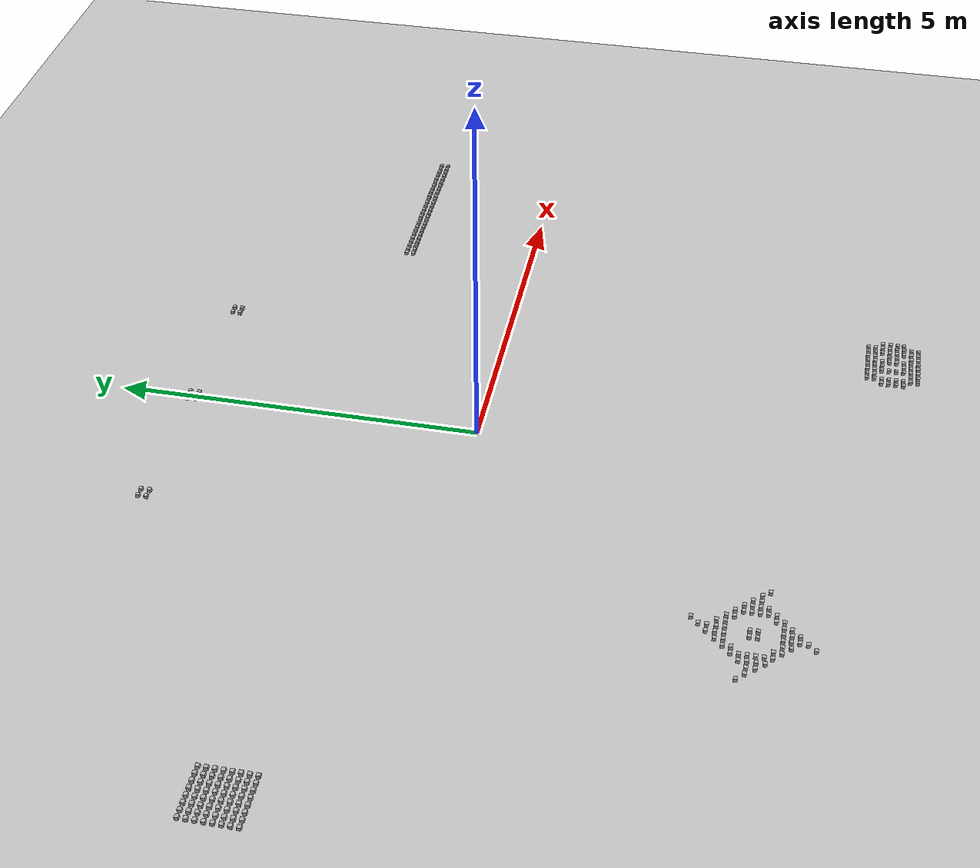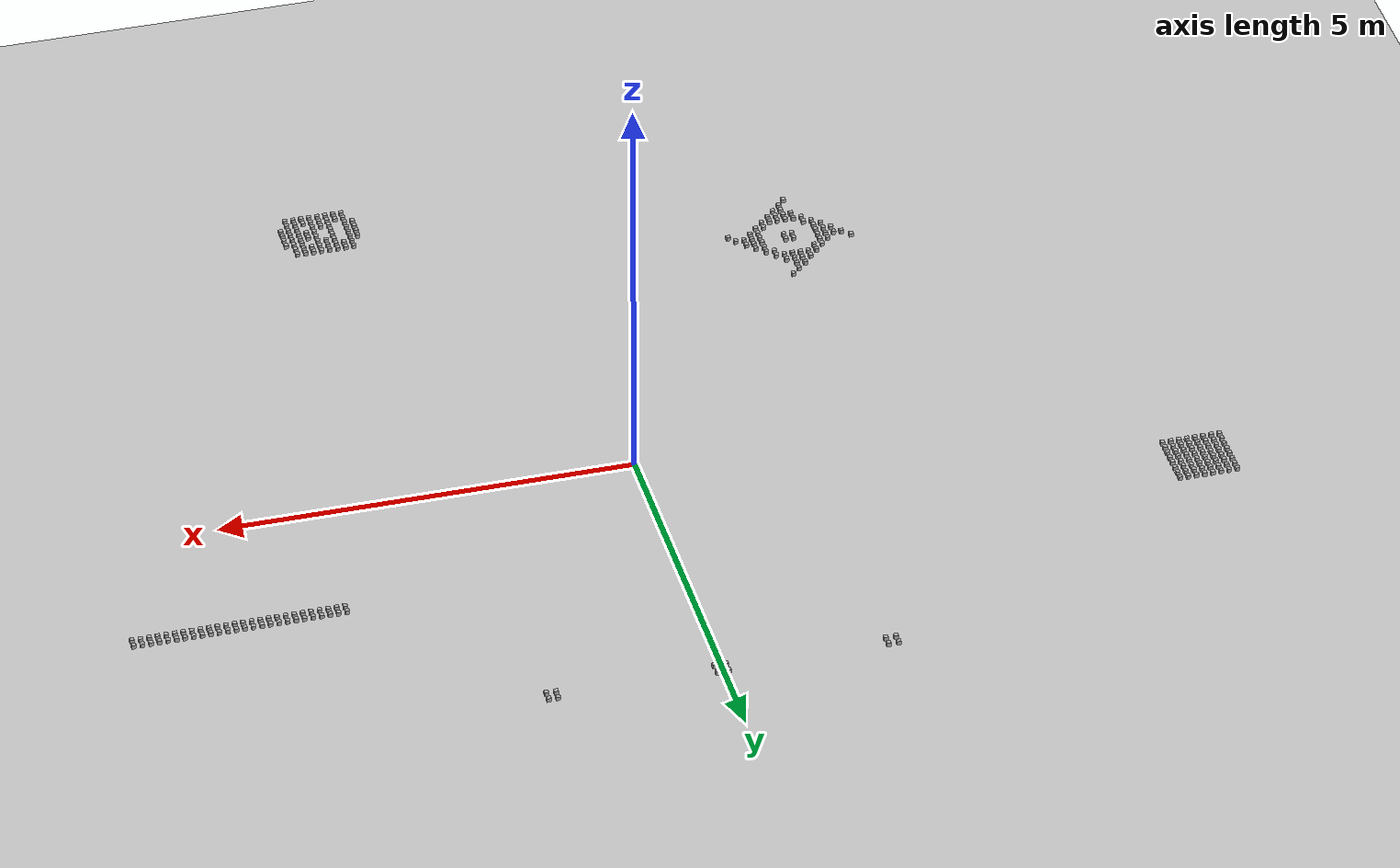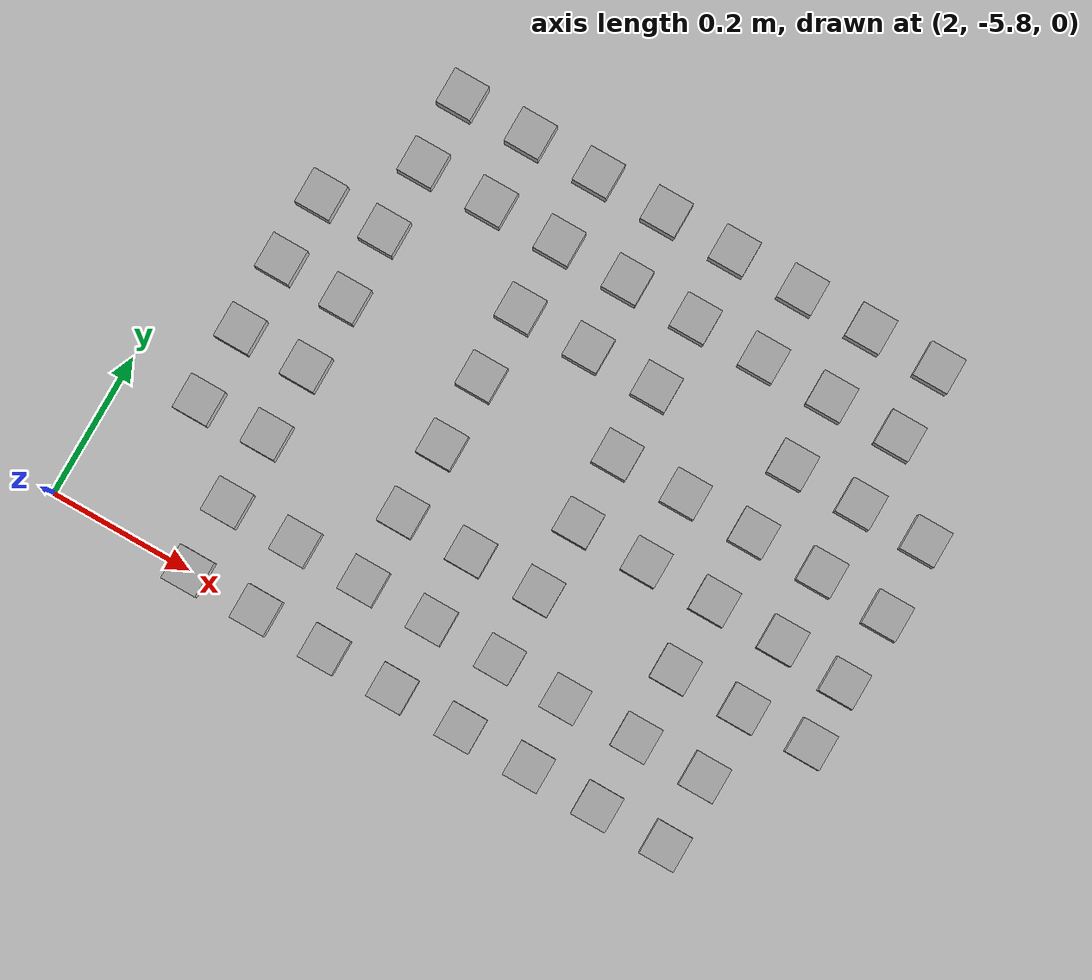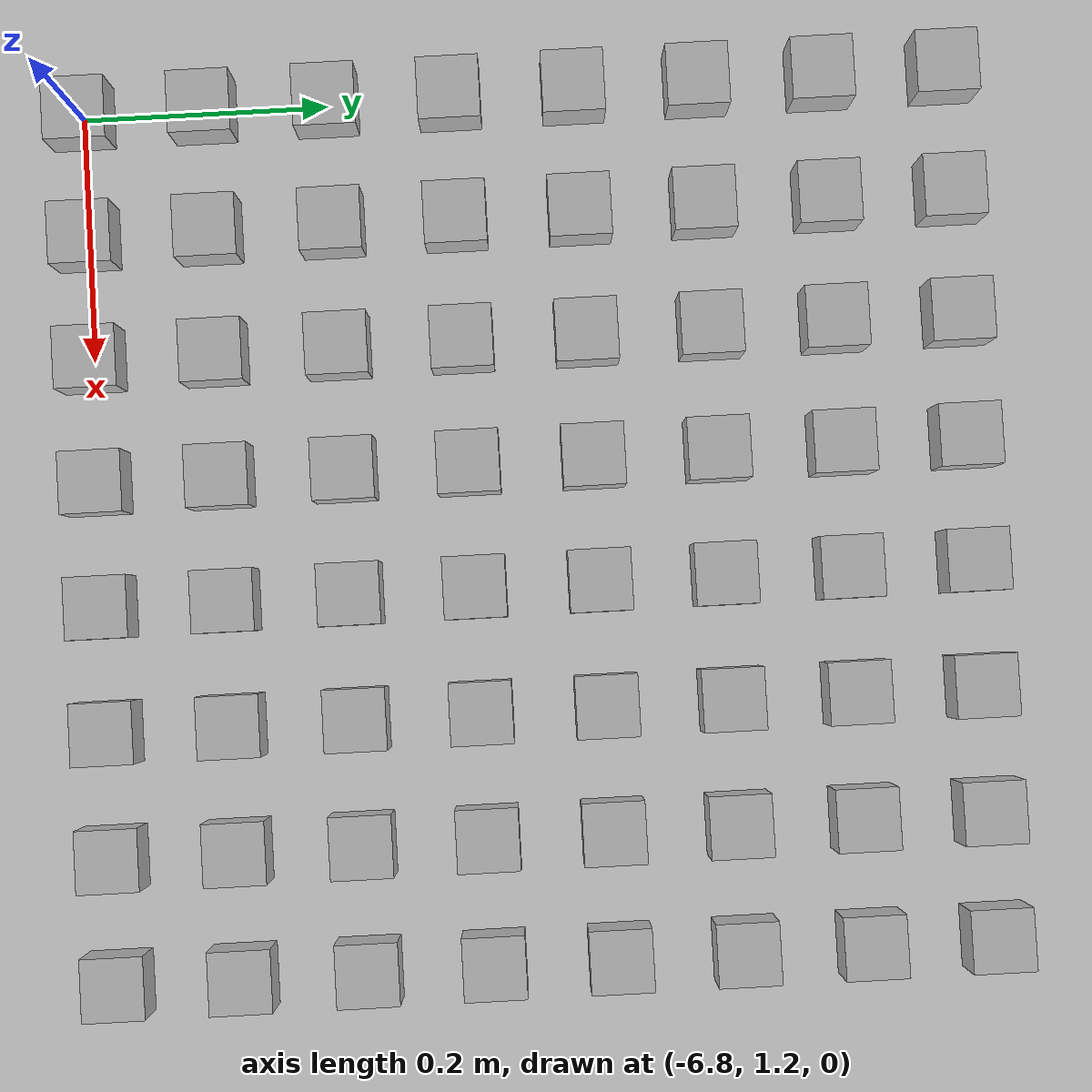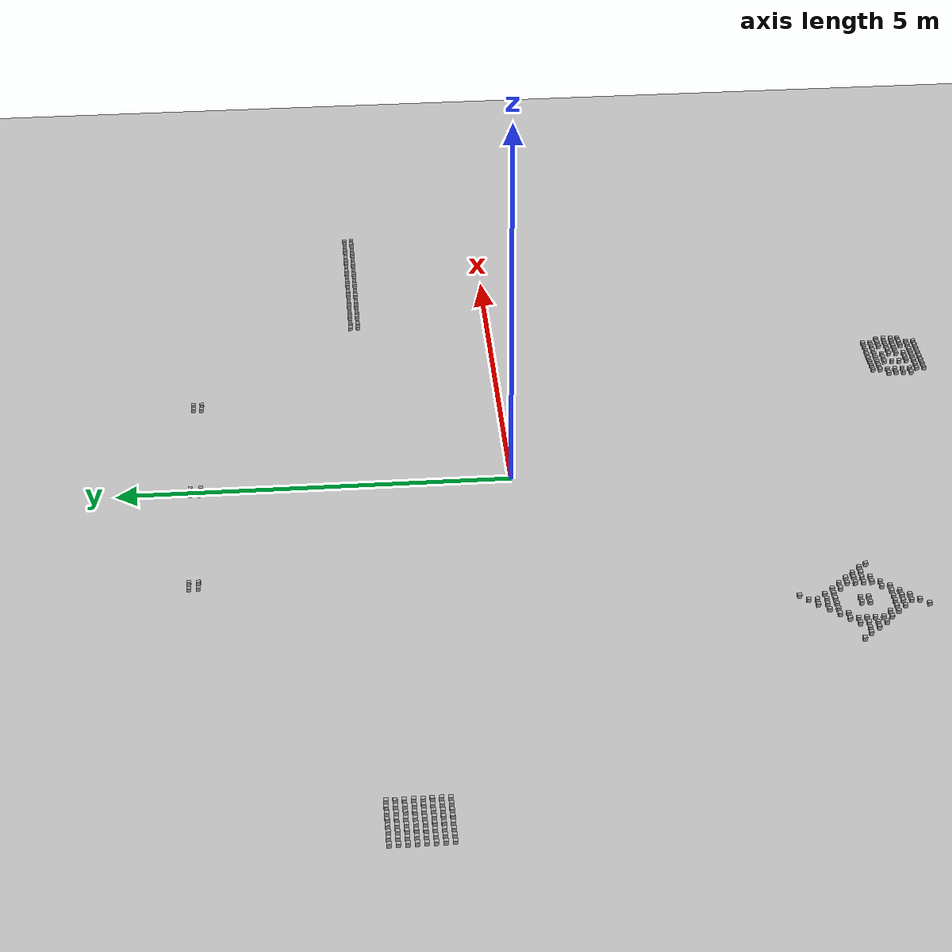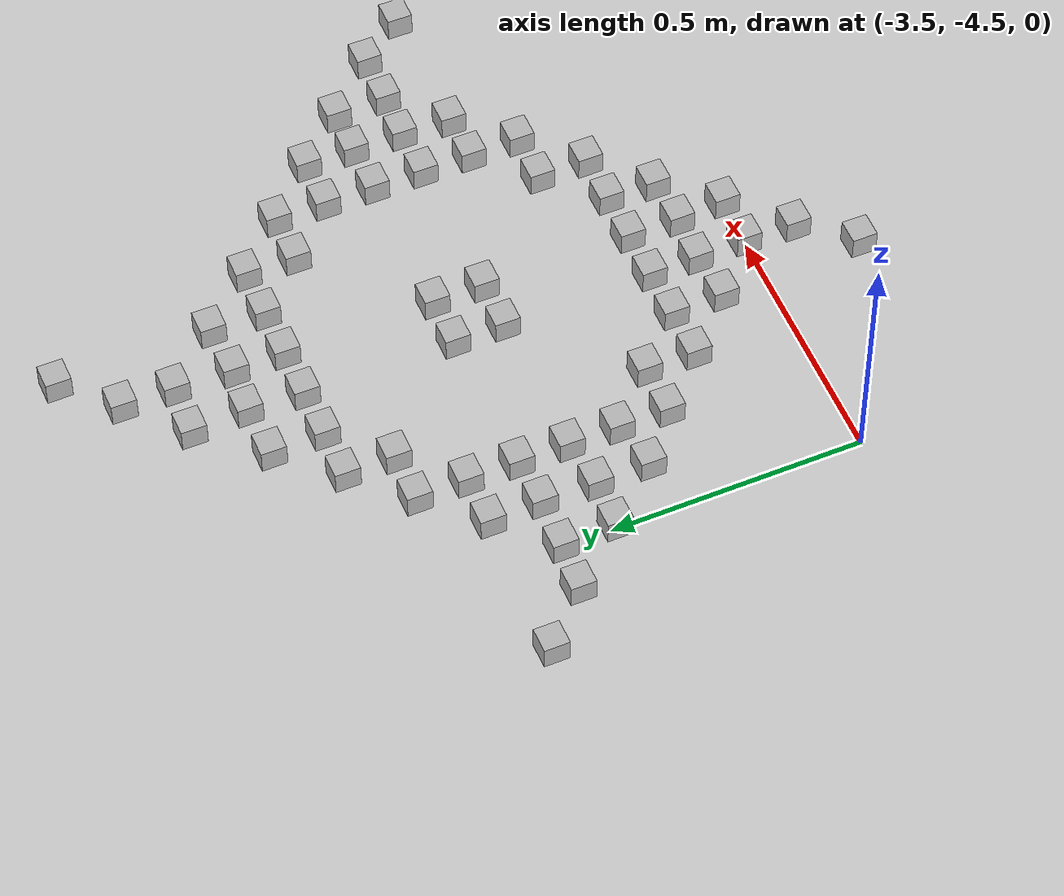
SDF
<sdf version="1.6">
 <world name="default">
  <model name="ground_plane">
   <static>1</static>
   <link name="link">
    <collision name="collision">
     <geometry><plane><normal>0 0 1</normal><size>100 100</size></plane></geometry>
     <surface><friction><ode><mu>100</mu><mu2>50</mu2></ode></friction></surface>
    </collision>
    <visual name="visual">
     <cast_shadows>0</cast_shadows>
     <geometry><plane><normal>0 0 1</normal><size>100 100</size></plane></geometry>
     <material>
      <script><uri>file://media/materials/scripts/gazebo.material</uri><name>Gazebo/Grey</name></script>
     </material>
    </visual>
   </link>
  </model>
  <light name="sun" type="directional">
   <pose>0 0 10 0 -0 0</pose>
   <diffuse>0.8 0.8 0.8 1</diffuse>
   <specular>0.1 0.1 0.1 1</specular>
   <attenuation>
    <range>1000</range>
    <constant>0.9</constant>
    <linear>0.01</linear>
    <quadratic>0.001</quadratic>
   </attenuation>
   <direction>-0.5 0.5 -1</direction>
  </light>
  <plugin name="SetupWorld" filename="libgazebo_plugins.so"/>
  <gravity>0 0 -9.8</gravity>
  <magnetic_field>6e-06 2.3e-05 -4.2e-05</magnetic_field>
  <atmosphere type="adiabatic"/>
  <physics name="default_physics" default="0" type="ode">
   <max_step_size>0.001</max_step_size>
   <real_time_factor>1</real_time_factor>
   <real_time_update_rate>1000</real_time_update_rate>
  </physics>
  <scene><ambient>0.4 0.4 0.4 1</ambient><background>0.7 0.7 0.7 1</background><shadows>1</shadows></scene>
  <spherical_coordinates>
   <surface_model>EARTH_WGS84</surface_model>
   <latitude_deg>0</latitude_deg>
   <longitude_deg>0</longitude_deg>
   <elevation>0</elevation>
   <heading_deg>0</heading_deg>
  </spherical_coordinates>
  <model name="at0">
   <static>0</static>
   <link name="link">
    <inertial>
     <mass>0.01</mass>
     <inertia><ixx>4e-05</ixx><ixy>0</ixy><ixz>0</ixz><iyy>4e-05</iyy><iyz>0</iyz><izz>4e-05</izz></inertia>
    </inertial>
    <visual name="visual">
     <geometry><box><size>0.05 0.05 0.05</size></box></geometry>
     <material>
      <script>
       <uri>model://at0/materials/scripts</uri>
       <uri>model://at0/materials/textures</uri>
       <name>at0/Diffuse</name>
      </script>
     </material>
    </visual>
    <collision name="collision">
     <geometry><box><size>0.05 0.05 0.05</size></box></geometry>
     <surface><friction><ode><mu>0.8</mu><mu2>0.7</mu2></ode></friction></surface>
    </collision>
   </link>
   <pose>3.9 1.8 0.025 0 -0 0</pose>
  </model>
  <model name="at1">
   <static>0</static>
   <link name="link">
    <inertial>
     <mass>0.01</mass>
     <inertia><ixx>4e-05</ixx><ixy>0</ixy><ixz>0</ixz><iyy>4e-05</iyy><iyz>0</iyz><izz>4e-05</izz></inertia>
    </inertial>
    <visual name="visual">
     <geometry><box><size>0.05 0.05 0.05</size></box></geometry>
     <material>
      <script>
       <uri>model://at0/materials/scripts</uri>
       <uri>model://at0/materials/textures</uri>
       <name>at0/Diffuse</name>
      </script>
     </material>
    </visual>
    <collision name="collision">
     <geometry><box><size>0.05 0.05 0.05</size></box></geometry>
     <surface><friction><ode><mu>0.8</mu><mu2>0.7</mu2></ode></friction></surface>
    </collision>
   </link>
   <pose>4 1.8 0.025 0 -0 0</pose>
  </model>
  <model name="at2">
   <static>0</static>
   <link name="link">
    <inertial>
     <mass>0.01</mass>
     <inertia><ixx>4e-05</ixx><ixy>0</ixy><ixz>0</ixz><iyy>4e-05</iyy><iyz>0</iyz><izz>4e-05</izz></inertia>
    </inertial>
    <visual name="visual">
     <geometry><box><size>0.05 0.05 0.05</size></box></geometry>
     <material>
      <script>
       <uri>model://at0/materials/scripts</uri>
       <uri>model://at0/materials/textures</uri>
       <name>at0/Diffuse</name>
      </script>
     </material>
    </visual>
    <collision name="collision">
     <geometry><box><size>0.05 0.05 0.05</size></box></geometry>
     <surface><friction><ode><mu>0.8</mu><mu2>0.7</mu2></ode></friction></surface>
    </collision>
   </link>
   <pose>4.1 1.8 0.025 0 -0 0</pose>
  </model>
  <model name="at3">
   <static>0</static>
   <link name="link">
    <inertial>
     <mass>0.01</mass>
     <inertia><ixx>4e-05</ixx><ixy>0</ixy><ixz>0</ixz><iyy>4e-05</iyy><iyz>0</iyz><izz>4e-05</izz></inertia>
    </inertial>
    <visual name="visual">
     <geometry><box><size>0.05 0.05 0.05</size></box></geometry>
     <material>
      <script>
       <uri>model://at0/materials/scripts</uri>
       <uri>model://at0/materials/textures</uri>
       <name>at0/Diffuse</name>
      </script>
     </material>
    </visual>
    <collision name="collision">
     <geometry><box><size>0.05 0.05 0.05</size></box></geometry>
     <surface><friction><ode><mu>0.8</mu><mu2>0.7</mu2></ode></friction></surface>
    </collision>
   </link>
   <pose>4.2 1.8 0.025 0 -0 0</pose>
  </model>
  <model name="at4">
   <static>0</static>
   <link name="link">
    <inertial>
     <mass>0.01</mass>
     <inertia><ixx>4e-05</ixx><ixy>0</ixy><ixz>0</ixz><iyy>4e-05</iyy><iyz>0</iyz><izz>4e-05</izz></inertia>
    </inertial>
    <visual name="visual">
     <geometry><box><size>0.05 0.05 0.05</size></box></geometry>
     <material>
      <script>
       <uri>model://at0/materials/scripts</uri>
       <uri>model://at0/materials/textures</uri>
       <name>at0/Diffuse</name>
      </script>
     </material>
    </visual>
    <collision name="collision">
     <geometry><box><size>0.05 0.05 0.05</size></box></geometry>
     <surface><friction><ode><mu>0.8</mu><mu2>0.7</mu2></ode></friction></surface>
    </collision>
   </link>
   <pose>4.3 1.8 0.025 0 -0 0</pose>
  </model>
  <model name="at5">
   <static>0</static>
   <link name="link">
    <inertial>
     <mass>0.01</mass>
     <inertia><ixx>4e-05</ixx><ixy>0</ixy><ixz>0</ixz><iyy>4e-05</iyy><iyz>0</iyz><izz>4e-05</izz></inertia>
    </inertial>
    <visual name="visual">
     <geometry><box><size>0.05 0.05 0.05</size></box></geometry>
     <material>
      <script>
       <uri>model://at0/materials/scripts</uri>
       <uri>model://at0/materials/textures</uri>
       <name>at0/Diffuse</name>
      </script>
     </material>
    </visual>
    <collision name="collision">
     <geometry><box><size>0.05 0.05 0.05</size></box></geometry>
     <surface><friction><ode><mu>0.8</mu><mu2>0.7</mu2></ode></friction></surface>
    </collision>
   </link>
   <pose>4.4 1.8 0.025 0 -0 0</pose>
  </model>
  <model name="at6">
   <static>0</static>
   <link name="link">
    <inertial>
     <mass>0.01</mass>
     <inertia><ixx>4e-05</ixx><ixy>0</ixy><ixz>0</ixz><iyy>4e-05</iyy><iyz>0</iyz><izz>4e-05</izz></inertia>
    </inertial>
    <visual name="visual">
     <geometry><box><size>0.05 0.05 0.05</size></box></geometry>
     <material>
      <script>
       <uri>model://at0/materials/scripts</uri>
       <uri>model://at0/materials/textures</uri>
       <name>at0/Diffuse</name>
      </script>
     </material>
    </visual>
    <collision name="collision">
     <geometry><box><size>0.05 0.05 0.05</size></box></geometry>
     <surface><friction><ode><mu>0.8</mu><mu2>0.7</mu2></ode></friction></surface>
    </collision>
   </link>
   <pose>4.5 1.8 0.025 0 -0 0</pose>
  </model>
  <model name="at7">
   <static>0</static>
   <link name="link">
    <inertial>
     <mass>0.01</mass>
     <inertia><ixx>4e-05</ixx><ixy>0</ixy><ixz>0</ixz><iyy>4e-05</iyy><iyz>0</iyz><izz>4e-05</izz></inertia>
    </inertial>
    <visual name="visual">
     <geometry><box><size>0.05 0.05 0.05</size></box></geometry>
     <material>
      <script>
       <uri>model://at0/materials/scripts</uri>
       <uri>model://at0/materials/textures</uri>
       <name>at0/Diffuse</name>
      </script>
     </material>
    </visual>
    <collision name="collision">
     <geometry><box><size>0.05 0.05 0.05</size></box></geometry>
     <surface><friction><ode><mu>0.8</mu><mu2>0.7</mu2></ode></friction></surface>
    </collision>
   </link>
   <pose>4.6 1.8 0.025 0 -0 0</pose>
  </model>
  <model name="at8">
   <static>0</static>
   <link name="link">
    <inertial>
     <mass>0.01</mass>
     <inertia><ixx>4e-05</ixx><ixy>0</ixy><ixz>0</ixz><iyy>4e-05</iyy><iyz>0</iyz><izz>4e-05</izz></inertia>
    </inertial>
    <visual name="visual">
     <geometry><box><size>0.05 0.05 0.05</size></box></geometry>
     <material>
      <script>
       <uri>model://at0/materials/scripts</uri>
       <uri>model://at0/materials/textures</uri>
       <name>at0/Diffuse</name>
      </script>
     </material>
    </visual>
    <collision name="collision">
     <geometry><box><size>0.05 0.05 0.05</size></box></geometry>
     <surface><friction><ode><mu>0.8</mu><mu2>0.7</mu2></ode></friction></surface>
    </collision>
   </link>
   <pose>4.7 1.8 0.025 0 -0 0</pose>
  </model>
  <model name="at9">
   <static>0</static>
   <link name="link">
    <inertial>
     <mass>0.01</mass>
     <inertia><ixx>4e-05</ixx><ixy>0</ixy><ixz>0</ixz><iyy>4e-05</iyy><iyz>0</iyz><izz>4e-05</izz></inertia>
    </inertial>
    <visual name="visual">
     <geometry><box><size>0.05 0.05 0.05</size></box></geometry>
     <material>
      <script>
       <uri>model://at0/materials/scripts</uri>
       <uri>model://at0/materials/textures</uri>
       <name>at0/Diffuse</name>
      </script>
     </material>
    </visual>
    <collision name="collision">
     <geometry><box><size>0.05 0.05 0.05</size></box></geometry>
     <surface><friction><ode><mu>0.8</mu><mu2>0.7</mu2></ode></friction></surface>
    </collision>
   </link>
   <pose>4.8 1.8 0.025 0 -0 0</pose>
  </model>
  <model name="at10">
   <static>0</static>
   <link name="link">
    <inertial>
     <mass>0.01</mass>
     <inertia><ixx>4e-05</ixx><ixy>0</ixy><ixz>0</ixz><iyy>4e-05</iyy><iyz>0</iyz><izz>4e-05</izz></inertia>
    </inertial>
    <visual name="visual">
     <geometry><box><size>0.05 0.05 0.05</size></box></geometry>
     <material>
      <script>
       <uri>model://at0/materials/scripts</uri>
       <uri>model://at0/materials/textures</uri>
       <name>at0/Diffuse</name>
      </script>
     </material>
    </visual>
    <collision name="collision">
     <geometry><box><size>0.05 0.05 0.05</size></box></geometry>
     <surface><friction><ode><mu>0.8</mu><mu2>0.7</mu2></ode></friction></surface>
    </collision>
   </link>
   <pose>4.9 1.8 0.025 0 -0 0</pose>
  </model>
  <model name="at11">
   <static>0</static>
   <link name="link">
    <inertial>
     <mass>0.01</mass>
     <inertia><ixx>4e-05</ixx><ixy>0</ixy><ixz>0</ixz><iyy>4e-05</iyy><iyz>0</iyz><izz>4e-05</izz></inertia>
    </inertial>
    <visual name="visual">
     <geometry><box><size>0.05 0.05 0.05</size></box></geometry>
     <material>
      <script>
       <uri>model://at0/materials/scripts</uri>
       <uri>model://at0/materials/textures</uri>
       <name>at0/Diffuse</name>
      </script>
     </material>
    </visual>
    <collision name="collision">
     <geometry><box><size>0.05 0.05 0.05</size></box></geometry>
     <surface><friction><ode><mu>0.8</mu><mu2>0.7</mu2></ode></friction></surface>
    </collision>
   </link>
   <pose>5 1.8 0.025 0 -0 0</pose>
  </model>
  <model name="at12">
   <static>0</static>
   <link name="link">
    <inertial>
     <mass>0.01</mass>
     <inertia><ixx>4e-05</ixx><ixy>0</ixy><ixz>0</ixz><iyy>4e-05</iyy><iyz>0</iyz><izz>4e-05</izz></inertia>
    </inertial>
    <visual name="visual">
     <geometry><box><size>0.05 0.05 0.05</size></box></geometry>
     <material>
      <script>
       <uri>model://at0/materials/scripts</uri>
       <uri>model://at0/materials/textures</uri>
       <name>at0/Diffuse</name>
      </script>
     </material>
    </visual>
    <collision name="collision">
     <geometry><box><size>0.05 0.05 0.05</size></box></geometry>
     <surface><friction><ode><mu>0.8</mu><mu2>0.7</mu2></ode></friction></surface>
    </collision>
   </link>
   <pose>5.1 1.8 0.025 0 -0 0</pose>
  </model>
  <model name="at13">
   <static>0</static>
   <link name="link">
    <inertial>
     <mass>0.01</mass>
     <inertia><ixx>4e-05</ixx><ixy>0</ixy><ixz>0</ixz><iyy>4e-05</iyy><iyz>0</iyz><izz>4e-05</izz></inertia>
    </inertial>
    <visual name="visual">
     <geometry><box><size>0.05 0.05 0.05</size></box></geometry>
     <material>
      <script>
       <uri>model://at0/materials/scripts</uri>
       <uri>model://at0/materials/textures</uri>
       <name>at0/Diffuse</name>
      </script>
     </material>
    </visual>
    <collision name="collision">
     <geometry><box><size>0.05 0.05 0.05</size></box></geometry>
     <surface><friction><ode><mu>0.8</mu><mu2>0.7</mu2></ode></friction></surface>
    </collision>
   </link>
   <pose>5.2 1.8 0.025 0 -0 0</pose>
  </model>
  <model name="at14">
   <static>0</static>
   <link name="link">
    <inertial>
     <mass>0.01</mass>
     <inertia><ixx>4e-05</ixx><ixy>0</ixy><ixz>0</ixz><iyy>4e-05</iyy><iyz>0</iyz><izz>4e-05</izz></inertia>
    </inertial>
    <visual name="visual">
     <geometry><box><size>0.05 0.05 0.05</size></box></geometry>
     <material>
      <script>
       <uri>model://at0/materials/scripts</uri>
       <uri>model://at0/materials/textures</uri>
       <name>at0/Diffuse</name>
      </script>
     </material>
    </visual>
    <collision name="collision">
     <geometry><box><size>0.05 0.05 0.05</size></box></geometry>
     <surface><friction><ode><mu>0.8</mu><mu2>0.7</mu2></ode></friction></surface>
    </collision>
   </link>
   <pose>5.3 1.8 0.025 0 -0 0</pose>
  </model>
  <model name="at15">
   <static>0</static>
   <link name="link">
    <inertial>
     <mass>0.01</mass>
     <inertia><ixx>4e-05</ixx><ixy>0</ixy><ixz>0</ixz><iyy>4e-05</iyy><iyz>0</iyz><izz>4e-05</izz></inertia>
    </inertial>
    <visual name="visual">
     <geometry><box><size>0.05 0.05 0.05</size></box></geometry>
     <material>
      <script>
       <uri>model://at0/materials/scripts</uri>
       <uri>model://at0/materials/textures</uri>
       <name>at0/Diffuse</name>
      </script>
     </material>
    </visual>
    <collision name="collision">
     <geometry><box><size>0.05 0.05 0.05</size></box></geometry>
     <surface><friction><ode><mu>0.8</mu><mu2>0.7</mu2></ode></friction></surface>
    </collision>
   </link>
   <pose>5.4 1.8 0.025 0 -0 0</pose>
  </model>
  <model name="at16">
   <static>0</static>
   <link name="link">
    <inertial>
     <mass>0.01</mass>
     <inertia><ixx>4e-05</ixx><ixy>0</ixy><ixz>0</ixz><iyy>4e-05</iyy><iyz>0</iyz><izz>4e-05</izz></inertia>
    </inertial>
    <visual name="visual">
     <geometry><box><size>0.05 0.05 0.05</size></box></geometry>
     <material>
      <script>
       <uri>model://at0/materials/scripts</uri>
       <uri>model://at0/materials/textures</uri>
       <name>at0/Diffuse</name>
      </script>
     </material>
    </visual>
    <collision name="collision">
     <geometry><box><size>0.05 0.05 0.05</size></box></geometry>
     <surface><friction><ode><mu>0.8</mu><mu2>0.7</mu2></ode></friction></surface>
    </collision>
   </link>
   <pose>5.5 1.8 0.025 0 -0 0</pose>
  </model>
  <model name="at17">
   <static>0</static>
   <link name="link">
    <inertial>
     <mass>0.01</mass>
     <inertia><ixx>4e-05</ixx><ixy>0</ixy><ixz>0</ixz><iyy>4e-05</iyy><iyz>0</iyz><izz>4e-05</izz></inertia>
    </inertial>
    <visual name="visual">
     <geometry><box><size>0.05 0.05 0.05</size></box></geometry>
     <material>
      <script>
       <uri>model://at0/materials/scripts</uri>
       <uri>model://at0/materials/textures</uri>
       <name>at0/Diffuse</name>
      </script>
     </material>
    </visual>
    <collision name="collision">
     <geometry><box><size>0.05 0.05 0.05</size></box></geometry>
     <surface><friction><ode><mu>0.8</mu><mu2>0.7</mu2></ode></friction></surface>
    </collision>
   </link>
   <pose>5.6 1.8 0.025 0 -0 0</pose>
  </model>
  <model name="at18">
   <static>0</static>
   <link name="link">
    <inertial>
     <mass>0.01</mass>
     <inertia><ixx>4e-05</ixx><ixy>0</ixy><ixz>0</ixz><iyy>4e-05</iyy><iyz>0</iyz><izz>4e-05</izz></inertia>
    </inertial>
    <visual name="visual">
     <geometry><box><size>0.05 0.05 0.05</size></box></geometry>
     <material>
      <script>
       <uri>model://at0/materials/scripts</uri>
       <uri>model://at0/materials/textures</uri>
       <name>at0/Diffuse</name>
      </script>
     </material>
    </visual>
    <collision name="collision">
     <geometry><box><size>0.05 0.05 0.05</size></box></geometry>
     <surface><friction><ode><mu>0.8</mu><mu2>0.7</mu2></ode></friction></surface>
    </collision>
   </link>
   <pose>5.7 1.8 0.025 0 -0 0</pose>
  </model>
  <model name="at19">
   <static>0</static>
   <link name="link">
    <inertial>
     <mass>0.01</mass>
     <inertia><ixx>4e-05</ixx><ixy>0</ixy><ixz>0</ixz><iyy>4e-05</iyy><iyz>0</iyz><izz>4e-05</izz></inertia>
    </inertial>
    <visual name="visual">
     <geometry><box><size>0.05 0.05 0.05</size></box></geometry>
     <material>
      <script>
       <uri>model://at0/materials/scripts</uri>
       <uri>model://at0/materials/textures</uri>
       <name>at0/Diffuse</name>
      </script>
     </material>
    </visual>
    <collision name="collision">
     <geometry><box><size>0.05 0.05 0.05</size></box></geometry>
     <surface><friction><ode><mu>0.8</mu><mu2>0.7</mu2></ode></friction></surface>
    </collision>
   </link>
   <pose>5.8 1.8 0.025 0 -0 0</pose>
  </model>
  <model name="at20">
   <static>0</static>
   <link name="link">
    <inertial>
     <mass>0.01</mass>
     <inertia><ixx>4e-05</ixx><ixy>0</ixy><ixz>0</ixz><iyy>4e-05</iyy><iyz>0</iyz><izz>4e-05</izz></inertia>
    </inertial>
    <visual name="visual">
     <geometry><box><size>0.05 0.05 0.05</size></box></geometry>
     <material>
      <script>
       <uri>model://at0/materials/scripts</uri>
       <uri>model://at0/materials/textures</uri>
       <name>at0/Diffuse</name>
      </script>
     </material>
    </visual>
    <collision name="collision">
     <geometry><box><size>0.05 0.05 0.05</size></box></geometry>
     <surface><friction><ode><mu>0.8</mu><mu2>0.7</mu2></ode></friction></surface>
    </collision>
   </link>
   <pose>5.9 1.8 0.025 0 -0 0</pose>
  </model>
  <model name="at21">
   <static>0</static>
   <link name="link">
    <inertial>
     <mass>0.01</mass>
     <inertia><ixx>4e-05</ixx><ixy>0</ixy><ixz>0</ixz><iyy>4e-05</iyy><iyz>0</iyz><izz>4e-05</izz></inertia>
    </inertial>
    <visual name="visual">
     <geometry><box><size>0.05 0.05 0.05</size></box></geometry>
     <material>
      <script>
       <uri>model://at0/materials/scripts</uri>
       <uri>model://at0/materials/textures</uri>
       <name>at0/Diffuse</name>
      </script>
     </material>
    </visual>
    <collision name="collision">
     <geometry><box><size>0.05 0.05 0.05</size></box></geometry>
     <surface><friction><ode><mu>0.8</mu><mu2>0.7</mu2></ode></friction></surface>
    </collision>
   </link>
   <pose>6 1.8 0.025 0 -0 0</pose>
  </model>
  <model name="at22">
   <static>0</static>
   <link name="link">
    <inertial>
     <mass>0.01</mass>
     <inertia><ixx>4e-05</ixx><ixy>0</ixy><ixz>0</ixz><iyy>4e-05</iyy><iyz>0</iyz><izz>4e-05</izz></inertia>
    </inertial>
    <visual name="visual">
     <geometry><box><size>0.05 0.05 0.05</size></box></geometry>
     <material>
      <script>
       <uri>model://at0/materials/scripts</uri>
       <uri>model://at0/materials/textures</uri>
       <name>at0/Diffuse</name>
      </script>
     </material>
    </visual>
    <collision name="collision">
     <geometry><box><size>0.05 0.05 0.05</size></box></geometry>
     <surface><friction><ode><mu>0.8</mu><mu2>0.7</mu2></ode></friction></surface>
    </collision>
   </link>
   <pose>6.1 1.8 0.025 0 -0 0</pose>
  </model>
  <model name="at23">
   <static>0</static>
   <link name="link">
    <inertial>
     <mass>0.01</mass>
     <inertia><ixx>4e-05</ixx><ixy>0</ixy><ixz>0</ixz><iyy>4e-05</iyy><iyz>0</iyz><izz>4e-05</izz></inertia>
    </inertial>
    <visual name="visual">
     <geometry><box><size>0.05 0.05 0.05</size></box></geometry>
     <material>
      <script>
       <uri>model://at0/materials/scripts</uri>
       <uri>model://at0/materials/textures</uri>
       <name>at0/Diffuse</name>
      </script>
     </material>
    </visual>
    <collision name="collision">
     <geometry><box><size>0.05 0.05 0.05</size></box></geometry>
     <surface><friction><ode><mu>0.8</mu><mu2>0.7</mu2></ode></friction></surface>
    </collision>
   </link>
   <pose>6.2 1.8 0.025 0 -0 0</pose>
  </model>
  <model name="at24">
   <static>0</static>
   <link name="link">
    <inertial>
     <mass>0.01</mass>
     <inertia><ixx>4e-05</ixx><ixy>0</ixy><ixz>0</ixz><iyy>4e-05</iyy><iyz>0</iyz><izz>4e-05</izz></inertia>
    </inertial>
    <visual name="visual">
     <geometry><box><size>0.05 0.05 0.05</size></box></geometry>
     <material>
      <script>
       <uri>model://at0/materials/scripts</uri>
       <uri>model://at0/materials/textures</uri>
       <name>at0/Diffuse</name>
      </script>
     </material>
    </visual>
    <collision name="collision">
     <geometry><box><size>0.05 0.05 0.05</size></box></geometry>
     <surface><friction><ode><mu>0.8</mu><mu2>0.7</mu2></ode></friction></surface>
    </collision>
   </link>
   <pose>6.3 1.8 0.025 0 -0 0</pose>
  </model>
  <model name="at25">
   <static>0</static>
   <link name="link">
    <inertial>
     <mass>0.01</mass>
     <inertia><ixx>4e-05</ixx><ixy>0</ixy><ixz>0</ixz><iyy>4e-05</iyy><iyz>0</iyz><izz>4e-05</izz></inertia>
    </inertial>
    <visual name="visual">
     <geometry><box><size>0.05 0.05 0.05</size></box></geometry>
     <material>
      <script>
       <uri>model://at0/materials/scripts</uri>
       <uri>model://at0/materials/textures</uri>
       <name>at0/Diffuse</name>
      </script>
     </material>
    </visual>
    <collision name="collision">
     <geometry><box><size>0.05 0.05 0.05</size></box></geometry>
     <surface><friction><ode><mu>0.8</mu><mu2>0.7</mu2></ode></friction></surface>
    </collision>
   </link>
   <pose>6.4 1.8 0.025 0 -0 0</pose>
  </model>
  <model name="at26">
   <static>0</static>
   <link name="link">
    <inertial>
     <mass>0.01</mass>
     <inertia><ixx>4e-05</ixx><ixy>0</ixy><ixz>0</ixz><iyy>4e-05</iyy><iyz>0</iyz><izz>4e-05</izz></inertia>
    </inertial>
    <visual name="visual">
     <geometry><box><size>0.05 0.05 0.05</size></box></geometry>
     <material>
      <script>
       <uri>model://at0/materials/scripts</uri>
       <uri>model://at0/materials/textures</uri>
       <name>at0/Diffuse</name>
      </script>
     </material>
    </visual>
    <collision name="collision">
     <geometry><box><size>0.05 0.05 0.05</size></box></geometry>
     <surface><friction><ode><mu>0.8</mu><mu2>0.7</mu2></ode></friction></surface>
    </collision>
   </link>
   <pose>-2.06209 3.94308 0.025 0 -0 0</pose>
  </model>
  <model name="at27">
   <static>0</static>
   <link name="link">
    <inertial>
     <mass>0.01</mass>
     <inertia><ixx>4e-05</ixx><ixy>0</ixy><ixz>0</ixz><iyy>4e-05</iyy><iyz>0</iyz><izz>4e-05</izz></inertia>
    </inertial>
    <visual name="visual">
     <geometry><box><size>0.05 0.05 0.05</size></box></geometry>
     <material>
      <script>
       <uri>model://at0/materials/scripts</uri>
       <uri>model://at0/materials/textures</uri>
       <name>at0/Diffuse</name>
      </script>
     </material>
    </visual>
    <collision name="collision">
     <geometry><box><size>0.05 0.05 0.05</size></box></geometry>
     <surface><friction><ode><mu>0.8</mu><mu2>0.7</mu2></ode></friction></surface>
    </collision>
   </link>
   <pose>-1.94221 3.94126 0.025 0 -0 0</pose>
  </model>
  <model name="at28">
   <static>0</static>
   <link name="link">
    <inertial>
     <mass>0.01</mass>
     <inertia><ixx>4e-05</ixx><ixy>0</ixy><ixz>0</ixz><iyy>4e-05</iyy><iyz>0</iyz><izz>4e-05</izz></inertia>
    </inertial>
    <visual name="visual">
     <geometry><box><size>0.05 0.05 0.05</size></box></geometry>
     <material>
      <script>
       <uri>model://at0/materials/scripts</uri>
       <uri>model://at0/materials/textures</uri>
       <name>at0/Diffuse</name>
      </script>
     </material>
    </visual>
    <collision name="collision">
     <geometry><box><size>0.05 0.05 0.05</size></box></geometry>
     <surface><friction><ode><mu>0.8</mu><mu2>0.7</mu2></ode></friction></surface>
    </collision>
   </link>
   <pose>0.082013 3.93924 0.025 0 -0 0</pose>
  </model>
  <model name="at29">
   <static>0</static>
   <link name="link">
    <inertial>
     <mass>0.01</mass>
     <inertia><ixx>4e-05</ixx><ixy>0</ixy><ixz>0</ixz><iyy>4e-05</iyy><iyz>0</iyz><izz>4e-05</izz></inertia>
    </inertial>
    <visual name="visual">
     <geometry><box><size>0.05 0.05 0.05</size></box></geometry>
     <material>
      <script>
       <uri>model://at0/materials/scripts</uri>
       <uri>model://at0/materials/textures</uri>
       <name>at0/Diffuse</name>
      </script>
     </material>
    </visual>
    <collision name="collision">
     <geometry><box><size>0.05 0.05 0.05</size></box></geometry>
     <surface><friction><ode><mu>0.8</mu><mu2>0.7</mu2></ode></friction></surface>
    </collision>
   </link>
   <pose>-0.055173 3.94455 0.025 0 -0 0</pose>
  </model>
  <model name="at30">
   <static>0</static>
   <link name="link">
    <inertial>
     <mass>0.01</mass>
     <inertia><ixx>4e-05</ixx><ixy>0</ixy><ixz>0</ixz><iyy>4e-05</iyy><iyz>0</iyz><izz>4e-05</izz></inertia>
    </inertial>
    <visual name="visual">
     <geometry><box><size>0.05 0.05 0.05</size></box></geometry>
     <material>
      <script>
       <uri>model://at0/materials/scripts</uri>
       <uri>model://at0/materials/textures</uri>
       <name>at0/Diffuse</name>
      </script>
     </material>
    </visual>
    <collision name="collision">
     <geometry><box><size>0.05 0.05 0.05</size></box></geometry>
     <surface><friction><ode><mu>0.8</mu><mu2>0.7</mu2></ode></friction></surface>
    </collision>
   </link>
   <pose>2.05386 3.94033 0.025 0 -0 0</pose>
  </model>
  <model name="at31">
   <static>0</static>
   <link name="link">
    <inertial>
     <mass>0.01</mass>
     <inertia><ixx>4e-05</ixx><ixy>0</ixy><ixz>0</ixz><iyy>4e-05</iyy><iyz>0</iyz><izz>4e-05</izz></inertia>
    </inertial>
    <visual name="visual">
     <geometry><box><size>0.05 0.05 0.05</size></box></geometry>
     <material>
      <script>
       <uri>model://at0/materials/scripts</uri>
       <uri>model://at0/materials/textures</uri>
       <name>at0/Diffuse</name>
      </script>
     </material>
    </visual>
    <collision name="collision">
     <geometry><box><size>0.05 0.05 0.05</size></box></geometry>
     <surface><friction><ode><mu>0.8</mu><mu2>0.7</mu2></ode></friction></surface>
    </collision>
   </link>
   <pose>1.94311 3.94151 0.025 0 -0 0</pose>
  </model>
  <model name="at32">
   <static>0</static>
   <link name="link">
    <inertial>
     <mass>0.01</mass>
     <inertia><ixx>4e-05</ixx><ixy>0</ixy><ixz>0</ixz><iyy>4e-05</iyy><iyz>0</iyz><izz>4e-05</izz></inertia>
    </inertial>
    <visual name="visual">
     <geometry><box><size>0.05 0.05 0.05</size></box></geometry>
     <material>
      <script>
       <uri>model://at0/materials/scripts</uri>
       <uri>model://at0/materials/textures</uri>
       <name>at0/Diffuse</name>
      </script>
     </material>
    </visual>
    <collision name="collision">
     <geometry><box><size>0.05 0.05 0.05</size></box></geometry>
     <surface><friction><ode><mu>0.8</mu><mu2>0.7</mu2></ode></friction></surface>
    </collision>
   </link>
   <pose>3.9 1.9 0.025 0 -0 0</pose>
  </model>
  <model name="at33">
   <static>0</static>
   <link name="link">
    <inertial>
     <mass>0.01</mass>
     <inertia><ixx>4e-05</ixx><ixy>0</ixy><ixz>0</ixz><iyy>4e-05</iyy><iyz>0</iyz><izz>4e-05</izz></inertia>
    </inertial>
    <visual name="visual">
     <geometry><box><size>0.05 0.05 0.05</size></box></geometry>
     <material>
      <script>
       <uri>model://at0/materials/scripts</uri>
       <uri>model://at0/materials/textures</uri>
       <name>at0/Diffuse</name>
      </script>
     </material>
    </visual>
    <collision name="collision">
     <geometry><box><size>0.05 0.05 0.05</size></box></geometry>
     <surface><friction><ode><mu>0.8</mu><mu2>0.7</mu2></ode></friction></surface>
    </collision>
   </link>
   <pose>4 1.9 0.025 0 -0 0</pose>
  </model>
  <model name="at34">
   <static>0</static>
   <link name="link">
    <inertial>
     <mass>0.01</mass>
     <inertia><ixx>4e-05</ixx><ixy>0</ixy><ixz>0</ixz><iyy>4e-05</iyy><iyz>0</iyz><izz>4e-05</izz></inertia>
    </inertial>
    <visual name="visual">
     <geometry><box><size>0.05 0.05 0.05</size></box></geometry>
     <material>
      <script>
       <uri>model://at0/materials/scripts</uri>
       <uri>model://at0/materials/textures</uri>
       <name>at0/Diffuse</name>
      </script>
     </material>
    </visual>
    <collision name="collision">
     <geometry><box><size>0.05 0.05 0.05</size></box></geometry>
     <surface><friction><ode><mu>0.8</mu><mu2>0.7</mu2></ode></friction></surface>
    </collision>
   </link>
   <pose>4.1 1.9 0.025 0 -0 0</pose>
  </model>
  <model name="at35">
   <static>0</static>
   <link name="link">
    <inertial>
     <mass>0.01</mass>
     <inertia><ixx>4e-05</ixx><ixy>0</ixy><ixz>0</ixz><iyy>4e-05</iyy><iyz>0</iyz><izz>4e-05</izz></inertia>
    </inertial>
    <visual name="visual">
     <geometry><box><size>0.05 0.05 0.05</size></box></geometry>
     <material>
      <script>
       <uri>model://at0/materials/scripts</uri>
       <uri>model://at0/materials/textures</uri>
       <name>at0/Diffuse</name>
      </script>
     </material>
    </visual>
    <collision name="collision">
     <geometry><box><size>0.05 0.05 0.05</size></box></geometry>
     <surface><friction><ode><mu>0.8</mu><mu2>0.7</mu2></ode></friction></surface>
    </collision>
   </link>
   <pose>4.2 1.9 0.025 0 -0 0</pose>
  </model>
  <model name="at36">
   <static>0</static>
   <link name="link">
    <inertial>
     <mass>0.01</mass>
     <inertia><ixx>4e-05</ixx><ixy>0</ixy><ixz>0</ixz><iyy>4e-05</iyy><iyz>0</iyz><izz>4e-05</izz></inertia>
    </inertial>
    <visual name="visual">
     <geometry><box><size>0.05 0.05 0.05</size></box></geometry>
     <material>
      <script>
       <uri>model://at0/materials/scripts</uri>
       <uri>model://at0/materials/textures</uri>
       <name>at0/Diffuse</name>
      </script>
     </material>
    </visual>
    <collision name="collision">
     <geometry><box><size>0.05 0.05 0.05</size></box></geometry>
     <surface><friction><ode><mu>0.8</mu><mu2>0.7</mu2></ode></friction></surface>
    </collision>
   </link>
   <pose>4.3 1.9 0.025 0 -0 0</pose>
  </model>
  <model name="at37">
   <static>0</static>
   <link name="link">
    <inertial>
     <mass>0.01</mass>
     <inertia><ixx>4e-05</ixx><ixy>0</ixy><ixz>0</ixz><iyy>4e-05</iyy><iyz>0</iyz><izz>4e-05</izz></inertia>
    </inertial>
    <visual name="visual">
     <geometry><box><size>0.05 0.05 0.05</size></box></geometry>
     <material>
      <script>
       <uri>model://at0/materials/scripts</uri>
       <uri>model://at0/materials/textures</uri>
       <name>at0/Diffuse</name>
      </script>
     </material>
    </visual>
    <collision name="collision">
     <geometry><box><size>0.05 0.05 0.05</size></box></geometry>
     <surface><friction><ode><mu>0.8</mu><mu2>0.7</mu2></ode></friction></surface>
    </collision>
   </link>
   <pose>4.4 1.9 0.025 0 -0 0</pose>
  </model>
  <model name="at38">
   <static>0</static>
   <link name="link">
    <inertial>
     <mass>0.01</mass>
     <inertia><ixx>4e-05</ixx><ixy>0</ixy><ixz>0</ixz><iyy>4e-05</iyy><iyz>0</iyz><izz>4e-05</izz></inertia>
    </inertial>
    <visual name="visual">
     <geometry><box><size>0.05 0.05 0.05</size></box></geometry>
     <material>
      <script>
       <uri>model://at0/materials/scripts</uri>
       <uri>model://at0/materials/textures</uri>
       <name>at0/Diffuse</name>
      </script>
     </material>
    </visual>
    <collision name="collision">
     <geometry><box><size>0.05 0.05 0.05</size></box></geometry>
     <surface><friction><ode><mu>0.8</mu><mu2>0.7</mu2></ode></friction></surface>
    </collision>
   </link>
   <pose>4.5 1.9 0.025 0 -0 0</pose>
  </model>
  <model name="at39">
   <static>0</static>
   <link name="link">
    <inertial>
     <mass>0.01</mass>
     <inertia><ixx>4e-05</ixx><ixy>0</ixy><ixz>0</ixz><iyy>4e-05</iyy><iyz>0</iyz><izz>4e-05</izz></inertia>
    </inertial>
    <visual name="visual">
     <geometry><box><size>0.05 0.05 0.05</size></box></geometry>
     <material>
      <script>
       <uri>model://at0/materials/scripts</uri>
       <uri>model://at0/materials/textures</uri>
       <name>at0/Diffuse</name>
      </script>
     </material>
    </visual>
    <collision name="collision">
     <geometry><box><size>0.05 0.05 0.05</size></box></geometry>
     <surface><friction><ode><mu>0.8</mu><mu2>0.7</mu2></ode></friction></surface>
    </collision>
   </link>
   <pose>4.6 1.9 0.025 0 -0 0</pose>
  </model>
  <model name="at40">
   <static>0</static>
   <link name="link">
    <inertial>
     <mass>0.01</mass>
     <inertia><ixx>4e-05</ixx><ixy>0</ixy><ixz>0</ixz><iyy>4e-05</iyy><iyz>0</iyz><izz>4e-05</izz></inertia>
    </inertial>
    <visual name="visual">
     <geometry><box><size>0.05 0.05 0.05</size></box></geometry>
     <material>
      <script>
       <uri>model://at0/materials/scripts</uri>
       <uri>model://at0/materials/textures</uri>
       <name>at0/Diffuse</name>
      </script>
     </material>
    </visual>
    <collision name="collision">
     <geometry><box><size>0.05 0.05 0.05</size></box></geometry>
     <surface><friction><ode><mu>0.8</mu><mu2>0.7</mu2></ode></friction></surface>
    </collision>
   </link>
   <pose>4.7 1.9 0.025 0 -0 0</pose>
  </model>
  <model name="at41">
   <static>0</static>
   <link name="link">
    <inertial>
     <mass>0.01</mass>
     <inertia><ixx>4e-05</ixx><ixy>0</ixy><ixz>0</ixz><iyy>4e-05</iyy><iyz>0</iyz><izz>4e-05</izz></inertia>
    </inertial>
    <visual name="visual">
     <geometry><box><size>0.05 0.05 0.05</size></box></geometry>
     <material>
      <script>
       <uri>model://at0/materials/scripts</uri>
       <uri>model://at0/materials/textures</uri>
       <name>at0/Diffuse</name>
      </script>
     </material>
    </visual>
    <collision name="collision">
     <geometry><box><size>0.05 0.05 0.05</size></box></geometry>
     <surface><friction><ode><mu>0.8</mu><mu2>0.7</mu2></ode></friction></surface>
    </collision>
   </link>
   <pose>4.8 1.9 0.025 0 -0 0</pose>
  </model>
  <model name="at42">
   <static>0</static>
   <link name="link">
    <inertial>
     <mass>0.01</mass>
     <inertia><ixx>4e-05</ixx><ixy>0</ixy><ixz>0</ixz><iyy>4e-05</iyy><iyz>0</iyz><izz>4e-05</izz></inertia>
    </inertial>
    <visual name="visual">
     <geometry><box><size>0.05 0.05 0.05</size></box></geometry>
     <material>
      <script>
       <uri>model://at0/materials/scripts</uri>
       <uri>model://at0/materials/textures</uri>
       <name>at0/Diffuse</name>
      </script>
     </material>
    </visual>
    <collision name="collision">
     <geometry><box><size>0.05 0.05 0.05</size></box></geometry>
     <surface><friction><ode><mu>0.8</mu><mu2>0.7</mu2></ode></friction></surface>
    </collision>
   </link>
   <pose>4.9 1.9 0.025 0 -0 0</pose>
  </model>
  <model name="at43">
   <static>0</static>
   <link name="link">
    <inertial>
     <mass>0.01</mass>
     <inertia><ixx>4e-05</ixx><ixy>0</ixy><ixz>0</ixz><iyy>4e-05</iyy><iyz>0</iyz><izz>4e-05</izz></inertia>
    </inertial>
    <visual name="visual">
     <geometry><box><size>0.05 0.05 0.05</size></box></geometry>
     <material>
      <script>
       <uri>model://at0/materials/scripts</uri>
       <uri>model://at0/materials/textures</uri>
       <name>at0/Diffuse</name>
      </script>
     </material>
    </visual>
    <collision name="collision">
     <geometry><box><size>0.05 0.05 0.05</size></box></geometry>
     <surface><friction><ode><mu>0.8</mu><mu2>0.7</mu2></ode></friction></surface>
    </collision>
   </link>
   <pose>5 1.9 0.025 0 -0 0</pose>
  </model>
  <model name="at44">
   <static>0</static>
   <link name="link">
    <inertial>
     <mass>0.01</mass>
     <inertia><ixx>4e-05</ixx><ixy>0</ixy><ixz>0</ixz><iyy>4e-05</iyy><iyz>0</iyz><izz>4e-05</izz></inertia>
    </inertial>
    <visual name="visual">
     <geometry><box><size>0.05 0.05 0.05</size></box></geometry>
     <material>
      <script>
       <uri>model://at0/materials/scripts</uri>
       <uri>model://at0/materials/textures</uri>
       <name>at0/Diffuse</name>
      </script>
     </material>
    </visual>
    <collision name="collision">
     <geometry><box><size>0.05 0.05 0.05</size></box></geometry>
     <surface><friction><ode><mu>0.8</mu><mu2>0.7</mu2></ode></friction></surface>
    </collision>
   </link>
   <pose>5.1 1.9 0.025 0 -0 0</pose>
  </model>
  <model name="at45">
   <static>0</static>
   <link name="link">
    <inertial>
     <mass>0.01</mass>
     <inertia><ixx>4e-05</ixx><ixy>0</ixy><ixz>0</ixz><iyy>4e-05</iyy><iyz>0</iyz><izz>4e-05</izz></inertia>
    </inertial>
    <visual name="visual">
     <geometry><box><size>0.05 0.05 0.05</size></box></geometry>
     <material>
      <script>
       <uri>model://at0/materials/scripts</uri>
       <uri>model://at0/materials/textures</uri>
       <name>at0/Diffuse</name>
      </script>
     </material>
    </visual>
    <collision name="collision">
     <geometry><box><size>0.05 0.05 0.05</size></box></geometry>
     <surface><friction><ode><mu>0.8</mu><mu2>0.7</mu2></ode></friction></surface>
    </collision>
   </link>
   <pose>5.2 1.9 0.025 0 -0 0</pose>
  </model>
  <model name="at46">
   <static>0</static>
   <link name="link">
    <inertial>
     <mass>0.01</mass>
     <inertia><ixx>4e-05</ixx><ixy>0</ixy><ixz>0</ixz><iyy>4e-05</iyy><iyz>0</iyz><izz>4e-05</izz></inertia>
    </inertial>
    <visual name="visual">
     <geometry><box><size>0.05 0.05 0.05</size></box></geometry>
     <material>
      <script>
       <uri>model://at0/materials/scripts</uri>
       <uri>model://at0/materials/textures</uri>
       <name>at0/Diffuse</name>
      </script>
     </material>
    </visual>
    <collision name="collision">
     <geometry><box><size>0.05 0.05 0.05</size></box></geometry>
     <surface><friction><ode><mu>0.8</mu><mu2>0.7</mu2></ode></friction></surface>
    </collision>
   </link>
   <pose>5.3 1.9 0.025 0 -0 0</pose>
  </model>
  <model name="at47">
   <static>0</static>
   <link name="link">
    <inertial>
     <mass>0.01</mass>
     <inertia><ixx>4e-05</ixx><ixy>0</ixy><ixz>0</ixz><iyy>4e-05</iyy><iyz>0</iyz><izz>4e-05</izz></inertia>
    </inertial>
    <visual name="visual">
     <geometry><box><size>0.05 0.05 0.05</size></box></geometry>
     <material>
      <script>
       <uri>model://at0/materials/scripts</uri>
       <uri>model://at0/materials/textures</uri>
       <name>at0/Diffuse</name>
      </script>
     </material>
    </visual>
    <collision name="collision">
     <geometry><box><size>0.05 0.05 0.05</size></box></geometry>
     <surface><friction><ode><mu>0.8</mu><mu2>0.7</mu2></ode></friction></surface>
    </collision>
   </link>
   <pose>5.4 1.9 0.025 0 -0 0</pose>
  </model>
  <model name="at48">
   <static>0</static>
   <link name="link">
    <inertial>
     <mass>0.01</mass>
     <inertia><ixx>4e-05</ixx><ixy>0</ixy><ixz>0</ixz><iyy>4e-05</iyy><iyz>0</iyz><izz>4e-05</izz></inertia>
    </inertial>
    <visual name="visual">
     <geometry><box><size>0.05 0.05 0.05</size></box></geometry>
     <material>
      <script>
       <uri>model://at0/materials/scripts</uri>
       <uri>model://at0/materials/textures</uri>
       <name>at0/Diffuse</name>
      </script>
     </material>
    </visual>
    <collision name="collision">
     <geometry><box><size>0.05 0.05 0.05</size></box></geometry>
     <surface><friction><ode><mu>0.8</mu><mu2>0.7</mu2></ode></friction></surface>
    </collision>
   </link>
   <pose>5.5 1.9 0.025 0 -0 0</pose>
  </model>
  <model name="at49">
   <static>0</static>
   <link name="link">
    <inertial>
     <mass>0.01</mass>
     <inertia><ixx>4e-05</ixx><ixy>0</ixy><ixz>0</ixz><iyy>4e-05</iyy><iyz>0</iyz><izz>4e-05</izz></inertia>
    </inertial>
    <visual name="visual">
     <geometry><box><size>0.05 0.05 0.05</size></box></geometry>
     <material>
      <script>
       <uri>model://at0/materials/scripts</uri>
       <uri>model://at0/materials/textures</uri>
       <name>at0/Diffuse</name>
      </script>
     </material>
    </visual>
    <collision name="collision">
     <geometry><box><size>0.05 0.05 0.05</size></box></geometry>
     <surface><friction><ode><mu>0.8</mu><mu2>0.7</mu2></ode></friction></surface>
    </collision>
   </link>
   <pose>5.6 1.9 0.025 0 -0 0</pose>
  </model>
  <model name="at50">
   <static>0</static>
   <link name="link">
    <inertial>
     <mass>0.01</mass>
     <inertia><ixx>4e-05</ixx><ixy>0</ixy><ixz>0</ixz><iyy>4e-05</iyy><iyz>0</iyz><izz>4e-05</izz></inertia>
    </inertial>
    <visual name="visual">
     <geometry><box><size>0.05 0.05 0.05</size></box></geometry>
     <material>
      <script>
       <uri>model://at0/materials/scripts</uri>
       <uri>model://at0/materials/textures</uri>
       <name>at0/Diffuse</name>
      </script>
     </material>
    </visual>
    <collision name="collision">
     <geometry><box><size>0.05 0.05 0.05</size></box></geometry>
     <surface><friction><ode><mu>0.8</mu><mu2>0.7</mu2></ode></friction></surface>
    </collision>
   </link>
   <pose>5.7 1.9 0.025 0 -0 0</pose>
  </model>
  <model name="at51">
   <static>0</static>
   <link name="link">
    <inertial>
     <mass>0.01</mass>
     <inertia><ixx>4e-05</ixx><ixy>0</ixy><ixz>0</ixz><iyy>4e-05</iyy><iyz>0</iyz><izz>4e-05</izz></inertia>
    </inertial>
    <visual name="visual">
     <geometry><box><size>0.05 0.05 0.05</size></box></geometry>
     <material>
      <script>
       <uri>model://at0/materials/scripts</uri>
       <uri>model://at0/materials/textures</uri>
       <name>at0/Diffuse</name>
      </script>
     </material>
    </visual>
    <collision name="collision">
     <geometry><box><size>0.05 0.05 0.05</size></box></geometry>
     <surface><friction><ode><mu>0.8</mu><mu2>0.7</mu2></ode></friction></surface>
    </collision>
   </link>
   <pose>5.8 1.9 0.025 0 -0 0</pose>
  </model>
  <model name="at52">
   <static>0</static>
   <link name="link">
    <inertial>
     <mass>0.01</mass>
     <inertia><ixx>4e-05</ixx><ixy>0</ixy><ixz>0</ixz><iyy>4e-05</iyy><iyz>0</iyz><izz>4e-05</izz></inertia>
    </inertial>
    <visual name="visual">
     <geometry><box><size>0.05 0.05 0.05</size></box></geometry>
     <material>
      <script>
       <uri>model://at0/materials/scripts</uri>
       <uri>model://at0/materials/textures</uri>
       <name>at0/Diffuse</name>
      </script>
     </material>
    </visual>
    <collision name="collision">
     <geometry><box><size>0.05 0.05 0.05</size></box></geometry>
     <surface><friction><ode><mu>0.8</mu><mu2>0.7</mu2></ode></friction></surface>
    </collision>
   </link>
   <pose>5.9 1.9 0.025 0 -0 0</pose>
  </model>
  <model name="at53">
   <static>0</static>
   <link name="link">
    <inertial>
     <mass>0.01</mass>
     <inertia><ixx>4e-05</ixx><ixy>0</ixy><ixz>0</ixz><iyy>4e-05</iyy><iyz>0</iyz><izz>4e-05</izz></inertia>
    </inertial>
    <visual name="visual">
     <geometry><box><size>0.05 0.05 0.05</size></box></geometry>
     <material>
      <script>
       <uri>model://at0/materials/scripts</uri>
       <uri>model://at0/materials/textures</uri>
       <name>at0/Diffuse</name>
      </script>
     </material>
    </visual>
    <collision name="collision">
     <geometry><box><size>0.05 0.05 0.05</size></box></geometry>
     <surface><friction><ode><mu>0.8</mu><mu2>0.7</mu2></ode></friction></surface>
    </collision>
   </link>
   <pose>6 1.9 0.025 0 -0 0</pose>
  </model>
  <model name="at54">
   <static>0</static>
   <link name="link">
    <inertial>
     <mass>0.01</mass>
     <inertia><ixx>4e-05</ixx><ixy>0</ixy><ixz>0</ixz><iyy>4e-05</iyy><iyz>0</iyz><izz>4e-05</izz></inertia>
    </inertial>
    <visual name="visual">
     <geometry><box><size>0.05 0.05 0.05</size></box></geometry>
     <material>
      <script>
       <uri>model://at0/materials/scripts</uri>
       <uri>model://at0/materials/textures</uri>
       <name>at0/Diffuse</name>
      </script>
     </material>
    </visual>
    <collision name="collision">
     <geometry><box><size>0.05 0.05 0.05</size></box></geometry>
     <surface><friction><ode><mu>0.8</mu><mu2>0.7</mu2></ode></friction></surface>
    </collision>
   </link>
   <pose>6.1 1.9 0.025 0 -0 0</pose>
  </model>
  <model name="at55">
   <static>0</static>
   <link name="link">
    <inertial>
     <mass>0.01</mass>
     <inertia><ixx>4e-05</ixx><ixy>0</ixy><ixz>0</ixz><iyy>4e-05</iyy><iyz>0</iyz><izz>4e-05</izz></inertia>
    </inertial>
    <visual name="visual">
     <geometry><box><size>0.05 0.05 0.05</size></box></geometry>
     <material>
      <script>
       <uri>model://at0/materials/scripts</uri>
       <uri>model://at0/materials/textures</uri>
       <name>at0/Diffuse</name>
      </script>
     </material>
    </visual>
    <collision name="collision">
     <geometry><box><size>0.05 0.05 0.05</size></box></geometry>
     <surface><friction><ode><mu>0.8</mu><mu2>0.7</mu2></ode></friction></surface>
    </collision>
   </link>
   <pose>6.2 1.9 0.025 0 -0 0</pose>
  </model>
  <model name="at56">
   <static>0</static>
   <link name="link">
    <inertial>
     <mass>0.01</mass>
     <inertia><ixx>4e-05</ixx><ixy>0</ixy><ixz>0</ixz><iyy>4e-05</iyy><iyz>0</iyz><izz>4e-05</izz></inertia>
    </inertial>
    <visual name="visual">
     <geometry><box><size>0.05 0.05 0.05</size></box></geometry>
     <material>
      <script>
       <uri>model://at0/materials/scripts</uri>
       <uri>model://at0/materials/textures</uri>
       <name>at0/Diffuse</name>
      </script>
     </material>
    </visual>
    <collision name="collision">
     <geometry><box><size>0.05 0.05 0.05</size></box></geometry>
     <surface><friction><ode><mu>0.8</mu><mu2>0.7</mu2></ode></friction></surface>
    </collision>
   </link>
   <pose>6.3 1.9 0.025 0 -0 0</pose>
  </model>
  <model name="at57">
   <static>0</static>
   <link name="link">
    <inertial>
     <mass>0.01</mass>
     <inertia><ixx>4e-05</ixx><ixy>0</ixy><ixz>0</ixz><iyy>4e-05</iyy><iyz>0</iyz><izz>4e-05</izz></inertia>
    </inertial>
    <visual name="visual">
     <geometry><box><size>0.05 0.05 0.05</size></box></geometry>
     <material>
      <script>
       <uri>model://at0/materials/scripts</uri>
       <uri>model://at0/materials/textures</uri>
       <name>at0/Diffuse</name>
      </script>
     </material>
    </visual>
    <collision name="collision">
     <geometry><box><size>0.05 0.05 0.05</size></box></geometry>
     <surface><friction><ode><mu>0.8</mu><mu2>0.7</mu2></ode></friction></surface>
    </collision>
   </link>
   <pose>6.4 1.9 0.025 0 -0 0</pose>
  </model>
  <model name="at58">
   <static>0</static>
   <link name="link">
    <inertial>
     <mass>0.01</mass>
     <inertia><ixx>4e-05</ixx><ixy>0</ixy><ixz>0</ixz><iyy>4e-05</iyy><iyz>0</iyz><izz>4e-05</izz></inertia>
    </inertial>
    <visual name="visual">
     <geometry><box><size>0.05 0.05 0.05</size></box></geometry>
     <material>
      <script>
       <uri>model://at0/materials/scripts</uri>
       <uri>model://at0/materials/textures</uri>
       <name>at0/Diffuse</name>
      </script>
     </material>
    </visual>
    <collision name="collision">
     <geometry><box><size>0.05 0.05 0.05</size></box></geometry>
     <surface><friction><ode><mu>0.8</mu><mu2>0.7</mu2></ode></friction></surface>
    </collision>
   </link>
   <pose>-1.94626 4.05595 0.025 0 -0 0</pose>
  </model>
  <model name="at59">
   <static>0</static>
   <link name="link">
    <inertial>
     <mass>0.01</mass>
     <inertia><ixx>4e-05</ixx><ixy>0</ixy><ixz>0</ixz><iyy>4e-05</iyy><iyz>0</iyz><izz>4e-05</izz></inertia>
    </inertial>
    <visual name="visual">
     <geometry><box><size>0.05 0.05 0.05</size></box></geometry>
     <material>
      <script>
       <uri>model://at0/materials/scripts</uri>
       <uri>model://at0/materials/textures</uri>
       <name>at0/Diffuse</name>
      </script>
     </material>
    </visual>
    <collision name="collision">
     <geometry><box><size>0.05 0.05 0.05</size></box></geometry>
     <surface><friction><ode><mu>0.8</mu><mu2>0.7</mu2></ode></friction></surface>
    </collision>
   </link>
   <pose>-2.06392 4.05499 0.025 0 -0 0</pose>
  </model>
  <model name="at60">
   <static>0</static>
   <link name="link">
    <inertial>
     <mass>0.01</mass>
     <inertia><ixx>4e-05</ixx><ixy>0</ixy><ixz>0</ixz><iyy>4e-05</iyy><iyz>0</iyz><izz>4e-05</izz></inertia>
    </inertial>
    <visual name="visual">
     <geometry><box><size>0.05 0.05 0.05</size></box></geometry>
     <material>
      <script>
       <uri>model://at0/materials/scripts</uri>
       <uri>model://at0/materials/textures</uri>
       <name>at0/Diffuse</name>
      </script>
     </material>
    </visual>
    <collision name="collision">
     <geometry><box><size>0.05 0.05 0.05</size></box></geometry>
     <surface><friction><ode><mu>0.8</mu><mu2>0.7</mu2></ode></friction></surface>
    </collision>
   </link>
   <pose>0.07803 4.06544 0.025 0 -0 0</pose>
  </model>
  <model name="at61">
   <static>0</static>
   <link name="link">
    <inertial>
     <mass>0.01</mass>
     <inertia><ixx>4e-05</ixx><ixy>0</ixy><ixz>0</ixz><iyy>4e-05</iyy><iyz>0</iyz><izz>4e-05</izz></inertia>
    </inertial>
    <visual name="visual">
     <geometry><box><size>0.05 0.05 0.05</size></box></geometry>
     <material>
      <script>
       <uri>model://at0/materials/scripts</uri>
       <uri>model://at0/materials/textures</uri>
       <name>at0/Diffuse</name>
      </script>
     </material>
    </visual>
    <collision name="collision">
     <geometry><box><size>0.05 0.05 0.05</size></box></geometry>
     <surface><friction><ode><mu>0.8</mu><mu2>0.7</mu2></ode></friction></surface>
    </collision>
   </link>
   <pose>-0.055835 4.06733 0.025 0 -0 0</pose>
  </model>
  <model name="at62">
   <static>0</static>
   <link name="link">
    <inertial>
     <mass>0.01</mass>
     <inertia><ixx>4e-05</ixx><ixy>0</ixy><ixz>0</ixz><iyy>4e-05</iyy><iyz>0</iyz><izz>4e-05</izz></inertia>
    </inertial>
    <visual name="visual">
     <geometry><box><size>0.05 0.05 0.05</size></box></geometry>
     <material>
      <script>
       <uri>model://at0/materials/scripts</uri>
       <uri>model://at0/materials/textures</uri>
       <name>at0/Diffuse</name>
      </script>
     </material>
    </visual>
    <collision name="collision">
     <geometry><box><size>0.05 0.05 0.05</size></box></geometry>
     <surface><friction><ode><mu>0.8</mu><mu2>0.7</mu2></ode></friction></surface>
    </collision>
   </link>
   <pose>2.05268 4.05076 0.025 0 -0 0</pose>
  </model>
  <model name="at63">
   <static>0</static>
   <link name="link">
    <inertial>
     <mass>0.01</mass>
     <inertia><ixx>4e-05</ixx><ixy>0</ixy><ixz>0</ixz><iyy>4e-05</iyy><iyz>0</iyz><izz>4e-05</izz></inertia>
    </inertial>
    <visual name="visual">
     <geometry><box><size>0.05 0.05 0.05</size></box></geometry>
     <material>
      <script>
       <uri>model://at0/materials/scripts</uri>
       <uri>model://at0/materials/textures</uri>
       <name>at0/Diffuse</name>
      </script>
     </material>
    </visual>
    <collision name="collision">
     <geometry><box><size>0.05 0.05 0.05</size></box></geometry>
     <surface><friction><ode><mu>0.8</mu><mu2>0.7</mu2></ode></friction></surface>
    </collision>
   </link>
   <pose>1.94506 4.05017 0.025 0 -0 0</pose>
  </model>
  <model name="at64">
   <static>0</static>
   <link name="link">
    <inertial>
     <mass>0.01</mass>
     <inertia><ixx>4e-05</ixx><ixy>0</ixy><ixz>0</ixz><iyy>4e-05</iyy><iyz>0</iyz><izz>4e-05</izz></inertia>
    </inertial>
    <visual name="visual">
     <geometry><box><size>0.05 0.05 0.05</size></box></geometry>
     <material>
      <script>
       <uri>model://at0/materials/scripts</uri>
       <uri>model://at0/materials/textures</uri>
       <name>at0/Diffuse</name>
      </script>
     </material>
    </visual>
    <collision name="collision">
     <geometry><box><size>0.05 0.05 0.05</size></box></geometry>
     <surface><friction><ode><mu>0.8</mu><mu2>0.7</mu2></ode></friction></surface>
    </collision>
   </link>
   <pose>-6.8 1.2 0.025 0 -0 0</pose>
  </model>
  <model name="at65">
   <static>0</static>
   <link name="link">
    <inertial>
     <mass>0.01</mass>
     <inertia><ixx>4e-05</ixx><ixy>0</ixy><ixz>0</ixz><iyy>4e-05</iyy><iyz>0</iyz><izz>4e-05</izz></inertia>
    </inertial>
    <visual name="visual">
     <geometry><box><size>0.05 0.05 0.05</size></box></geometry>
     <material>
      <script>
       <uri>model://at0/materials/scripts</uri>
       <uri>model://at0/materials/textures</uri>
       <name>at0/Diffuse</name>
      </script>
     </material>
    </visual>
    <collision name="collision">
     <geometry><box><size>0.05 0.05 0.05</size></box></geometry>
     <surface><friction><ode><mu>0.8</mu><mu2>0.7</mu2></ode></friction></surface>
    </collision>
   </link>
   <pose>-6.7 1.2 0.025 0 -0 0</pose>
  </model>
  <model name="at66">
   <static>0</static>
   <link name="link">
    <inertial>
     <mass>0.01</mass>
     <inertia><ixx>4e-05</ixx><ixy>0</ixy><ixz>0</ixz><iyy>4e-05</iyy><iyz>0</iyz><izz>4e-05</izz></inertia>
    </inertial>
    <visual name="visual">
     <geometry><box><size>0.05 0.05 0.05</size></box></geometry>
     <material>
      <script>
       <uri>model://at0/materials/scripts</uri>
       <uri>model://at0/materials/textures</uri>
       <name>at0/Diffuse</name>
      </script>
     </material>
    </visual>
    <collision name="collision">
     <geometry><box><size>0.05 0.05 0.05</size></box></geometry>
     <surface><friction><ode><mu>0.8</mu><mu2>0.7</mu2></ode></friction></surface>
    </collision>
   </link>
   <pose>-6.6 1.2 0.025 0 -0 0</pose>
  </model>
  <model name="at67">
   <static>0</static>
   <link name="link">
    <inertial>
     <mass>0.01</mass>
     <inertia><ixx>4e-05</ixx><ixy>0</ixy><ixz>0</ixz><iyy>4e-05</iyy><iyz>0</iyz><izz>4e-05</izz></inertia>
    </inertial>
    <visual name="visual">
     <geometry><box><size>0.05 0.05 0.05</size></box></geometry>
     <material>
      <script>
       <uri>model://at0/materials/scripts</uri>
       <uri>model://at0/materials/textures</uri>
       <name>at0/Diffuse</name>
      </script>
     </material>
    </visual>
    <collision name="collision">
     <geometry><box><size>0.05 0.05 0.05</size></box></geometry>
     <surface><friction><ode><mu>0.8</mu><mu2>0.7</mu2></ode></friction></surface>
    </collision>
   </link>
   <pose>-6.5 1.2 0.025 0 -0 0</pose>
  </model>
  <model name="at68">
   <static>0</static>
   <link name="link">
    <inertial>
     <mass>0.01</mass>
     <inertia><ixx>4e-05</ixx><ixy>0</ixy><ixz>0</ixz><iyy>4e-05</iyy><iyz>0</iyz><izz>4e-05</izz></inertia>
    </inertial>
    <visual name="visual">
     <geometry><box><size>0.05 0.05 0.05</size></box></geometry>
     <material>
      <script>
       <uri>model://at0/materials/scripts</uri>
       <uri>model://at0/materials/textures</uri>
       <name>at0/Diffuse</name>
      </script>
     </material>
    </visual>
    <collision name="collision">
     <geometry><box><size>0.05 0.05 0.05</size></box></geometry>
     <surface><friction><ode><mu>0.8</mu><mu2>0.7</mu2></ode></friction></surface>
    </collision>
   </link>
   <pose>-6.4 1.2 0.025 0 -0 0</pose>
  </model>
  <model name="at69">
   <static>0</static>
   <link name="link">
    <inertial>
     <mass>0.01</mass>
     <inertia><ixx>4e-05</ixx><ixy>0</ixy><ixz>0</ixz><iyy>4e-05</iyy><iyz>0</iyz><izz>4e-05</izz></inertia>
    </inertial>
    <visual name="visual">
     <geometry><box><size>0.05 0.05 0.05</size></box></geometry>
     <material>
      <script>
       <uri>model://at0/materials/scripts</uri>
       <uri>model://at0/materials/textures</uri>
       <name>at0/Diffuse</name>
      </script>
     </material>
    </visual>
    <collision name="collision">
     <geometry><box><size>0.05 0.05 0.05</size></box></geometry>
     <surface><friction><ode><mu>0.8</mu><mu2>0.7</mu2></ode></friction></surface>
    </collision>
   </link>
   <pose>-6.3 1.2 0.025 0 -0 0</pose>
  </model>
  <model name="at70">
   <static>0</static>
   <link name="link">
    <inertial>
     <mass>0.01</mass>
     <inertia><ixx>4e-05</ixx><ixy>0</ixy><ixz>0</ixz><iyy>4e-05</iyy><iyz>0</iyz><izz>4e-05</izz></inertia>
    </inertial>
    <visual name="visual">
     <geometry><box><size>0.05 0.05 0.05</size></box></geometry>
     <material>
      <script>
       <uri>model://at0/materials/scripts</uri>
       <uri>model://at0/materials/textures</uri>
       <name>at0/Diffuse</name>
      </script>
     </material>
    </visual>
    <collision name="collision">
     <geometry><box><size>0.05 0.05 0.05</size></box></geometry>
     <surface><friction><ode><mu>0.8</mu><mu2>0.7</mu2></ode></friction></surface>
    </collision>
   </link>
   <pose>-6.2 1.2 0.025 0 -0 0</pose>
  </model>
  <model name="at71">
   <static>0</static>
   <link name="link">
    <inertial>
     <mass>0.01</mass>
     <inertia><ixx>4e-05</ixx><ixy>0</ixy><ixz>0</ixz><iyy>4e-05</iyy><iyz>0</iyz><izz>4e-05</izz></inertia>
    </inertial>
    <visual name="visual">
     <geometry><box><size>0.05 0.05 0.05</size></box></geometry>
     <material>
      <script>
       <uri>model://at0/materials/scripts</uri>
       <uri>model://at0/materials/textures</uri>
       <name>at0/Diffuse</name>
      </script>
     </material>
    </visual>
    <collision name="collision">
     <geometry><box><size>0.05 0.05 0.05</size></box></geometry>
     <surface><friction><ode><mu>0.8</mu><mu2>0.7</mu2></ode></friction></surface>
    </collision>
   </link>
   <pose>-6.1 1.2 0.025 0 -0 0</pose>
  </model>
  <model name="at72">
   <static>0</static>
   <link name="link">
    <inertial>
     <mass>0.01</mass>
     <inertia><ixx>4e-05</ixx><ixy>0</ixy><ixz>0</ixz><iyy>4e-05</iyy><iyz>0</iyz><izz>4e-05</izz></inertia>
    </inertial>
    <visual name="visual">
     <geometry><box><size>0.05 0.05 0.05</size></box></geometry>
     <material>
      <script>
       <uri>model://at0/materials/scripts</uri>
       <uri>model://at0/materials/textures</uri>
       <name>at0/Diffuse</name>
      </script>
     </material>
    </visual>
    <collision name="collision">
     <geometry><box><size>0.05 0.05 0.05</size></box></geometry>
     <surface><friction><ode><mu>0.8</mu><mu2>0.7</mu2></ode></friction></surface>
    </collision>
   </link>
   <pose>-6.8 1.3 0.025 0 -0 0</pose>
  </model>
  <model name="at73">
   <static>0</static>
   <link name="link">
    <inertial>
     <mass>0.01</mass>
     <inertia><ixx>4e-05</ixx><ixy>0</ixy><ixz>0</ixz><iyy>4e-05</iyy><iyz>0</iyz><izz>4e-05</izz></inertia>
    </inertial>
    <visual name="visual">
     <geometry><box><size>0.05 0.05 0.05</size></box></geometry>
     <material>
      <script>
       <uri>model://at0/materials/scripts</uri>
       <uri>model://at0/materials/textures</uri>
       <name>at0/Diffuse</name>
      </script>
     </material>
    </visual>
    <collision name="collision">
     <geometry><box><size>0.05 0.05 0.05</size></box></geometry>
     <surface><friction><ode><mu>0.8</mu><mu2>0.7</mu2></ode></friction></surface>
    </collision>
   </link>
   <pose>-6.7 1.3 0.025 0 -0 0</pose>
  </model>
  <model name="at74">
   <static>0</static>
   <link name="link">
    <inertial>
     <mass>0.01</mass>
     <inertia><ixx>4e-05</ixx><ixy>0</ixy><ixz>0</ixz><iyy>4e-05</iyy><iyz>0</iyz><izz>4e-05</izz></inertia>
    </inertial>
    <visual name="visual">
     <geometry><box><size>0.05 0.05 0.05</size></box></geometry>
     <material>
      <script>
       <uri>model://at0/materials/scripts</uri>
       <uri>model://at0/materials/textures</uri>
       <name>at0/Diffuse</name>
      </script>
     </material>
    </visual>
    <collision name="collision">
     <geometry><box><size>0.05 0.05 0.05</size></box></geometry>
     <surface><friction><ode><mu>0.8</mu><mu2>0.7</mu2></ode></friction></surface>
    </collision>
   </link>
   <pose>-6.6 1.3 0.025 0 -0 0</pose>
  </model>
  <model name="at75">
   <static>0</static>
   <link name="link">
    <inertial>
     <mass>0.01</mass>
     <inertia><ixx>4e-05</ixx><ixy>0</ixy><ixz>0</ixz><iyy>4e-05</iyy><iyz>0</iyz><izz>4e-05</izz></inertia>
    </inertial>
    <visual name="visual">
     <geometry><box><size>0.05 0.05 0.05</size></box></geometry>
     <material>
      <script>
       <uri>model://at0/materials/scripts</uri>
       <uri>model://at0/materials/textures</uri>
       <name>at0/Diffuse</name>
      </script>
     </material>
    </visual>
    <collision name="collision">
     <geometry><box><size>0.05 0.05 0.05</size></box></geometry>
     <surface><friction><ode><mu>0.8</mu><mu2>0.7</mu2></ode></friction></surface>
    </collision>
   </link>
   <pose>-6.5 1.3 0.025 0 -0 0</pose>
  </model>
  <model name="at76">
   <static>0</static>
   <link name="link">
    <inertial>
     <mass>0.01</mass>
     <inertia><ixx>4e-05</ixx><ixy>0</ixy><ixz>0</ixz><iyy>4e-05</iyy><iyz>0</iyz><izz>4e-05</izz></inertia>
    </inertial>
    <visual name="visual">
     <geometry><box><size>0.05 0.05 0.05</size></box></geometry>
     <material>
      <script>
       <uri>model://at0/materials/scripts</uri>
       <uri>model://at0/materials/textures</uri>
       <name>at0/Diffuse</name>
      </script>
     </material>
    </visual>
    <collision name="collision">
     <geometry><box><size>0.05 0.05 0.05</size></box></geometry>
     <surface><friction><ode><mu>0.8</mu><mu2>0.7</mu2></ode></friction></surface>
    </collision>
   </link>
   <pose>-6.4 1.3 0.025 0 -0 0</pose>
  </model>
  <model name="at77">
   <static>0</static>
   <link name="link">
    <inertial>
     <mass>0.01</mass>
     <inertia><ixx>4e-05</ixx><ixy>0</ixy><ixz>0</ixz><iyy>4e-05</iyy><iyz>0</iyz><izz>4e-05</izz></inertia>
    </inertial>
    <visual name="visual">
     <geometry><box><size>0.05 0.05 0.05</size></box></geometry>
     <material>
      <script>
       <uri>model://at0/materials/scripts</uri>
       <uri>model://at0/materials/textures</uri>
       <name>at0/Diffuse</name>
      </script>
     </material>
    </visual>
    <collision name="collision">
     <geometry><box><size>0.05 0.05 0.05</size></box></geometry>
     <surface><friction><ode><mu>0.8</mu><mu2>0.7</mu2></ode></friction></surface>
    </collision>
   </link>
   <pose>-6.3 1.3 0.025 0 -0 0</pose>
  </model>
  <model name="at78">
   <static>0</static>
   <link name="link">
    <inertial>
     <mass>0.01</mass>
     <inertia><ixx>4e-05</ixx><ixy>0</ixy><ixz>0</ixz><iyy>4e-05</iyy><iyz>0</iyz><izz>4e-05</izz></inertia>
    </inertial>
    <visual name="visual">
     <geometry><box><size>0.05 0.05 0.05</size></box></geometry>
     <material>
      <script>
       <uri>model://at0/materials/scripts</uri>
       <uri>model://at0/materials/textures</uri>
       <name>at0/Diffuse</name>
      </script>
     </material>
    </visual>
    <collision name="collision">
     <geometry><box><size>0.05 0.05 0.05</size></box></geometry>
     <surface><friction><ode><mu>0.8</mu><mu2>0.7</mu2></ode></friction></surface>
    </collision>
   </link>
   <pose>-6.2 1.3 0.025 0 -0 0</pose>
  </model>
  <model name="at79">
   <static>0</static>
   <link name="link">
    <inertial>
     <mass>0.01</mass>
     <inertia><ixx>4e-05</ixx><ixy>0</ixy><ixz>0</ixz><iyy>4e-05</iyy><iyz>0</iyz><izz>4e-05</izz></inertia>
    </inertial>
    <visual name="visual">
     <geometry><box><size>0.05 0.05 0.05</size></box></geometry>
     <material>
      <script>
       <uri>model://at0/materials/scripts</uri>
       <uri>model://at0/materials/textures</uri>
       <name>at0/Diffuse</name>
      </script>
     </material>
    </visual>
    <collision name="collision">
     <geometry><box><size>0.05 0.05 0.05</size></box></geometry>
     <surface><friction><ode><mu>0.8</mu><mu2>0.7</mu2></ode></friction></surface>
    </collision>
   </link>
   <pose>-6.1 1.3 0.025 0 -0 0</pose>
  </model>
  <model name="at80">
   <static>0</static>
   <link name="link">
    <inertial>
     <mass>0.01</mass>
     <inertia><ixx>4e-05</ixx><ixy>0</ixy><ixz>0</ixz><iyy>4e-05</iyy><iyz>0</iyz><izz>4e-05</izz></inertia>
    </inertial>
    <visual name="visual">
     <geometry><box><size>0.05 0.05 0.05</size></box></geometry>
     <material>
      <script>
       <uri>model://at0/materials/scripts</uri>
       <uri>model://at0/materials/textures</uri>
       <name>at0/Diffuse</name>
      </script>
     </material>
    </visual>
    <collision name="collision">
     <geometry><box><size>0.05 0.05 0.05</size></box></geometry>
     <surface><friction><ode><mu>0.8</mu><mu2>0.7</mu2></ode></friction></surface>
    </collision>
   </link>
   <pose>-6.8 1.4 0.025 0 -0 0</pose>
  </model>
  <model name="at81">
   <static>0</static>
   <link name="link">
    <inertial>
     <mass>0.01</mass>
     <inertia><ixx>4e-05</ixx><ixy>0</ixy><ixz>0</ixz><iyy>4e-05</iyy><iyz>0</iyz><izz>4e-05</izz></inertia>
    </inertial>
    <visual name="visual">
     <geometry><box><size>0.05 0.05 0.05</size></box></geometry>
     <material>
      <script>
       <uri>model://at0/materials/scripts</uri>
       <uri>model://at0/materials/textures</uri>
       <name>at0/Diffuse</name>
      </script>
     </material>
    </visual>
    <collision name="collision">
     <geometry><box><size>0.05 0.05 0.05</size></box></geometry>
     <surface><friction><ode><mu>0.8</mu><mu2>0.7</mu2></ode></friction></surface>
    </collision>
   </link>
   <pose>-6.7 1.4 0.025 0 -0 0</pose>
  </model>
  <model name="at82">
   <static>0</static>
   <link name="link">
    <inertial>
     <mass>0.01</mass>
     <inertia><ixx>4e-05</ixx><ixy>0</ixy><ixz>0</ixz><iyy>4e-05</iyy><iyz>0</iyz><izz>4e-05</izz></inertia>
    </inertial>
    <visual name="visual">
     <geometry><box><size>0.05 0.05 0.05</size></box></geometry>
     <material>
      <script>
       <uri>model://at0/materials/scripts</uri>
       <uri>model://at0/materials/textures</uri>
       <name>at0/Diffuse</name>
      </script>
     </material>
    </visual>
    <collision name="collision">
     <geometry><box><size>0.05 0.05 0.05</size></box></geometry>
     <surface><friction><ode><mu>0.8</mu><mu2>0.7</mu2></ode></friction></surface>
    </collision>
   </link>
   <pose>-6.6 1.4 0.025 0 -0 0</pose>
  </model>
  <model name="at83">
   <static>0</static>
   <link name="link">
    <inertial>
     <mass>0.01</mass>
     <inertia><ixx>4e-05</ixx><ixy>0</ixy><ixz>0</ixz><iyy>4e-05</iyy><iyz>0</iyz><izz>4e-05</izz></inertia>
    </inertial>
    <visual name="visual">
     <geometry><box><size>0.05 0.05 0.05</size></box></geometry>
     <material>
      <script>
       <uri>model://at0/materials/scripts</uri>
       <uri>model://at0/materials/textures</uri>
       <name>at0/Diffuse</name>
      </script>
     </material>
    </visual>
    <collision name="collision">
     <geometry><box><size>0.05 0.05 0.05</size></box></geometry>
     <surface><friction><ode><mu>0.8</mu><mu2>0.7</mu2></ode></friction></surface>
    </collision>
   </link>
   <pose>-6.5 1.4 0.025 0 -0 0</pose>
  </model>
  <model name="at84">
   <static>0</static>
   <link name="link">
    <inertial>
     <mass>0.01</mass>
     <inertia><ixx>4e-05</ixx><ixy>0</ixy><ixz>0</ixz><iyy>4e-05</iyy><iyz>0</iyz><izz>4e-05</izz></inertia>
    </inertial>
    <visual name="visual">
     <geometry><box><size>0.05 0.05 0.05</size></box></geometry>
     <material>
      <script>
       <uri>model://at0/materials/scripts</uri>
       <uri>model://at0/materials/textures</uri>
       <name>at0/Diffuse</name>
      </script>
     </material>
    </visual>
    <collision name="collision">
     <geometry><box><size>0.05 0.05 0.05</size></box></geometry>
     <surface><friction><ode><mu>0.8</mu><mu2>0.7</mu2></ode></friction></surface>
    </collision>
   </link>
   <pose>-6.4 1.4 0.025 0 -0 0</pose>
  </model>
  <model name="at85">
   <static>0</static>
   <link name="link">
    <inertial>
     <mass>0.01</mass>
     <inertia><ixx>4e-05</ixx><ixy>0</ixy><ixz>0</ixz><iyy>4e-05</iyy><iyz>0</iyz><izz>4e-05</izz></inertia>
    </inertial>
    <visual name="visual">
     <geometry><box><size>0.05 0.05 0.05</size></box></geometry>
     <material>
      <script>
       <uri>model://at0/materials/scripts</uri>
       <uri>model://at0/materials/textures</uri>
       <name>at0/Diffuse</name>
      </script>
     </material>
    </visual>
    <collision name="collision">
     <geometry><box><size>0.05 0.05 0.05</size></box></geometry>
     <surface><friction><ode><mu>0.8</mu><mu2>0.7</mu2></ode></friction></surface>
    </collision>
   </link>
   <pose>-6.3 1.4 0.025 0 -0 0</pose>
  </model>
  <model name="at86">
   <static>0</static>
   <link name="link">
    <inertial>
     <mass>0.01</mass>
     <inertia><ixx>4e-05</ixx><ixy>0</ixy><ixz>0</ixz><iyy>4e-05</iyy><iyz>0</iyz><izz>4e-05</izz></inertia>
    </inertial>
    <visual name="visual">
     <geometry><box><size>0.05 0.05 0.05</size></box></geometry>
     <material>
      <script>
       <uri>model://at0/materials/scripts</uri>
       <uri>model://at0/materials/textures</uri>
       <name>at0/Diffuse</name>
      </script>
     </material>
    </visual>
    <collision name="collision">
     <geometry><box><size>0.05 0.05 0.05</size></box></geometry>
     <surface><friction><ode><mu>0.8</mu><mu2>0.7</mu2></ode></friction></surface>
    </collision>
   </link>
   <pose>-6.2 1.4 0.025 0 -0 0</pose>
  </model>
  <model name="at87">
   <static>0</static>
   <link name="link">
    <inertial>
     <mass>0.01</mass>
     <inertia><ixx>4e-05</ixx><ixy>0</ixy><ixz>0</ixz><iyy>4e-05</iyy><iyz>0</iyz><izz>4e-05</izz></inertia>
    </inertial>
    <visual name="visual">
     <geometry><box><size>0.05 0.05 0.05</size></box></geometry>
     <material>
      <script>
       <uri>model://at0/materials/scripts</uri>
       <uri>model://at0/materials/textures</uri>
       <name>at0/Diffuse</name>
      </script>
     </material>
    </visual>
    <collision name="collision">
     <geometry><box><size>0.05 0.05 0.05</size></box></geometry>
     <surface><friction><ode><mu>0.8</mu><mu2>0.7</mu2></ode></friction></surface>
    </collision>
   </link>
   <pose>-6.1 1.4 0.025 0 -0 0</pose>
  </model>
  <model name="at88">
   <static>0</static>
   <link name="link">
    <inertial>
     <mass>0.01</mass>
     <inertia><ixx>4e-05</ixx><ixy>0</ixy><ixz>0</ixz><iyy>4e-05</iyy><iyz>0</iyz><izz>4e-05</izz></inertia>
    </inertial>
    <visual name="visual">
     <geometry><box><size>0.05 0.05 0.05</size></box></geometry>
     <material>
      <script>
       <uri>model://at0/materials/scripts</uri>
       <uri>model://at0/materials/textures</uri>
       <name>at0/Diffuse</name>
      </script>
     </material>
    </visual>
    <collision name="collision">
     <geometry><box><size>0.05 0.05 0.05</size></box></geometry>
     <surface><friction><ode><mu>0.8</mu><mu2>0.7</mu2></ode></friction></surface>
    </collision>
   </link>
   <pose>-6.8 1.5 0.025 0 -0 0</pose>
  </model>
  <model name="at89">
   <static>0</static>
   <link name="link">
    <inertial>
     <mass>0.01</mass>
     <inertia><ixx>4e-05</ixx><ixy>0</ixy><ixz>0</ixz><iyy>4e-05</iyy><iyz>0</iyz><izz>4e-05</izz></inertia>
    </inertial>
    <visual name="visual">
     <geometry><box><size>0.05 0.05 0.05</size></box></geometry>
     <material>
      <script>
       <uri>model://at0/materials/scripts</uri>
       <uri>model://at0/materials/textures</uri>
       <name>at0/Diffuse</name>
      </script>
     </material>
    </visual>
    <collision name="collision">
     <geometry><box><size>0.05 0.05 0.05</size></box></geometry>
     <surface><friction><ode><mu>0.8</mu><mu2>0.7</mu2></ode></friction></surface>
    </collision>
   </link>
   <pose>-6.7 1.5 0.025 0 -0 0</pose>
  </model>
  <model name="at90">
   <static>0</static>
   <link name="link">
    <inertial>
     <mass>0.01</mass>
     <inertia><ixx>4e-05</ixx><ixy>0</ixy><ixz>0</ixz><iyy>4e-05</iyy><iyz>0</iyz><izz>4e-05</izz></inertia>
    </inertial>
    <visual name="visual">
     <geometry><box><size>0.05 0.05 0.05</size></box></geometry>
     <material>
      <script>
       <uri>model://at0/materials/scripts</uri>
       <uri>model://at0/materials/textures</uri>
       <name>at0/Diffuse</name>
      </script>
     </material>
    </visual>
    <collision name="collision">
     <geometry><box><size>0.05 0.05 0.05</size></box></geometry>
     <surface><friction><ode><mu>0.8</mu><mu2>0.7</mu2></ode></friction></surface>
    </collision>
   </link>
   <pose>-6.6 1.5 0.025 0 -0 0</pose>
  </model>
  <model name="at91">
   <static>0</static>
   <link name="link">
    <inertial>
     <mass>0.01</mass>
     <inertia><ixx>4e-05</ixx><ixy>0</ixy><ixz>0</ixz><iyy>4e-05</iyy><iyz>0</iyz><izz>4e-05</izz></inertia>
    </inertial>
    <visual name="visual">
     <geometry><box><size>0.05 0.05 0.05</size></box></geometry>
     <material>
      <script>
       <uri>model://at0/materials/scripts</uri>
       <uri>model://at0/materials/textures</uri>
       <name>at0/Diffuse</name>
      </script>
     </material>
    </visual>
    <collision name="collision">
     <geometry><box><size>0.05 0.05 0.05</size></box></geometry>
     <surface><friction><ode><mu>0.8</mu><mu2>0.7</mu2></ode></friction></surface>
    </collision>
   </link>
   <pose>-6.5 1.5 0.025 0 -0 0</pose>
  </model>
  <model name="at92">
   <static>0</static>
   <link name="link">
    <inertial>
     <mass>0.01</mass>
     <inertia><ixx>4e-05</ixx><ixy>0</ixy><ixz>0</ixz><iyy>4e-05</iyy><iyz>0</iyz><izz>4e-05</izz></inertia>
    </inertial>
    <visual name="visual">
     <geometry><box><size>0.05 0.05 0.05</size></box></geometry>
     <material>
      <script>
       <uri>model://at0/materials/scripts</uri>
       <uri>model://at0/materials/textures</uri>
       <name>at0/Diffuse</name>
      </script>
     </material>
    </visual>
    <collision name="collision">
     <geometry><box><size>0.05 0.05 0.05</size></box></geometry>
     <surface><friction><ode><mu>0.8</mu><mu2>0.7</mu2></ode></friction></surface>
    </collision>
   </link>
   <pose>-6.4 1.5 0.025 0 -0 0</pose>
  </model>
  <model name="at93">
   <static>0</static>
   <link name="link">
    <inertial>
     <mass>0.01</mass>
     <inertia><ixx>4e-05</ixx><ixy>0</ixy><ixz>0</ixz><iyy>4e-05</iyy><iyz>0</iyz><izz>4e-05</izz></inertia>
    </inertial>
    <visual name="visual">
     <geometry><box><size>0.05 0.05 0.05</size></box></geometry>
     <material>
      <script>
       <uri>model://at0/materials/scripts</uri>
       <uri>model://at0/materials/textures</uri>
       <name>at0/Diffuse</name>
      </script>
     </material>
    </visual>
    <collision name="collision">
     <geometry><box><size>0.05 0.05 0.05</size></box></geometry>
     <surface><friction><ode><mu>0.8</mu><mu2>0.7</mu2></ode></friction></surface>
    </collision>
   </link>
   <pose>-6.3 1.5 0.025 0 -0 0</pose>
  </model>
  <model name="at94">
   <static>0</static>
   <link name="link">
    <inertial>
     <mass>0.01</mass>
     <inertia><ixx>4e-05</ixx><ixy>0</ixy><ixz>0</ixz><iyy>4e-05</iyy><iyz>0</iyz><izz>4e-05</izz></inertia>
    </inertial>
    <visual name="visual">
     <geometry><box><size>0.05 0.05 0.05</size></box></geometry>
     <material>
      <script>
       <uri>model://at0/materials/scripts</uri>
       <uri>model://at0/materials/textures</uri>
       <name>at0/Diffuse</name>
      </script>
     </material>
    </visual>
    <collision name="collision">
     <geometry><box><size>0.05 0.05 0.05</size></box></geometry>
     <surface><friction><ode><mu>0.8</mu><mu2>0.7</mu2></ode></friction></surface>
    </collision>
   </link>
   <pose>-6.2 1.5 0.025 0 -0 0</pose>
  </model>
  <model name="at95">
   <static>0</static>
   <link name="link">
    <inertial>
     <mass>0.01</mass>
     <inertia><ixx>4e-05</ixx><ixy>0</ixy><ixz>0</ixz><iyy>4e-05</iyy><iyz>0</iyz><izz>4e-05</izz></inertia>
    </inertial>
    <visual name="visual">
     <geometry><box><size>0.05 0.05 0.05</size></box></geometry>
     <material>
      <script>
       <uri>model://at0/materials/scripts</uri>
       <uri>model://at0/materials/textures</uri>
       <name>at0/Diffuse</name>
      </script>
     </material>
    </visual>
    <collision name="collision">
     <geometry><box><size>0.05 0.05 0.05</size></box></geometry>
     <surface><friction><ode><mu>0.8</mu><mu2>0.7</mu2></ode></friction></surface>
    </collision>
   </link>
   <pose>-6.1 1.5 0.025 0 -0 0</pose>
  </model>
  <model name="at96">
   <static>0</static>
   <link name="link">
    <inertial>
     <mass>0.01</mass>
     <inertia><ixx>4e-05</ixx><ixy>0</ixy><ixz>0</ixz><iyy>4e-05</iyy><iyz>0</iyz><izz>4e-05</izz></inertia>
    </inertial>
    <visual name="visual">
     <geometry><box><size>0.05 0.05 0.05</size></box></geometry>
     <material>
      <script>
       <uri>model://at0/materials/scripts</uri>
       <uri>model://at0/materials/textures</uri>
       <name>at0/Diffuse</name>
      </script>
     </material>
    </visual>
    <collision name="collision">
     <geometry><box><size>0.05 0.05 0.05</size></box></geometry>
     <surface><friction><ode><mu>0.8</mu><mu2>0.7</mu2></ode></friction></surface>
    </collision>
   </link>
   <pose>-6.8 1.6 0.025 0 -0 0</pose>
  </model>
  <model name="at97">
   <static>0</static>
   <link name="link">
    <inertial>
     <mass>0.01</mass>
     <inertia><ixx>4e-05</ixx><ixy>0</ixy><ixz>0</ixz><iyy>4e-05</iyy><iyz>0</iyz><izz>4e-05</izz></inertia>
    </inertial>
    <visual name="visual">
     <geometry><box><size>0.05 0.05 0.05</size></box></geometry>
     <material>
      <script>
       <uri>model://at0/materials/scripts</uri>
       <uri>model://at0/materials/textures</uri>
       <name>at0/Diffuse</name>
      </script>
     </material>
    </visual>
    <collision name="collision">
     <geometry><box><size>0.05 0.05 0.05</size></box></geometry>
     <surface><friction><ode><mu>0.8</mu><mu2>0.7</mu2></ode></friction></surface>
    </collision>
   </link>
   <pose>-6.7 1.6 0.025 0 -0 0</pose>
  </model>
  <model name="at98">
   <static>0</static>
   <link name="link">
    <inertial>
     <mass>0.01</mass>
     <inertia><ixx>4e-05</ixx><ixy>0</ixy><ixz>0</ixz><iyy>4e-05</iyy><iyz>0</iyz><izz>4e-05</izz></inertia>
    </inertial>
    <visual name="visual">
     <geometry><box><size>0.05 0.05 0.05</size></box></geometry>
     <material>
      <script>
       <uri>model://at0/materials/scripts</uri>
       <uri>model://at0/materials/textures</uri>
       <name>at0/Diffuse</name>
      </script>
     </material>
    </visual>
    <collision name="collision">
     <geometry><box><size>0.05 0.05 0.05</size></box></geometry>
     <surface><friction><ode><mu>0.8</mu><mu2>0.7</mu2></ode></friction></surface>
    </collision>
   </link>
   <pose>-6.6 1.6 0.025 0 -0 0</pose>
  </model>
  <model name="at99">
   <static>0</static>
   <link name="link">
    <inertial>
     <mass>0.01</mass>
     <inertia><ixx>4e-05</ixx><ixy>0</ixy><ixz>0</ixz><iyy>4e-05</iyy><iyz>0</iyz><izz>4e-05</izz></inertia>
    </inertial>
    <visual name="visual">
     <geometry><box><size>0.05 0.05 0.05</size></box></geometry>
     <material>
      <script>
       <uri>model://at0/materials/scripts</uri>
       <uri>model://at0/materials/textures</uri>
       <name>at0/Diffuse</name>
      </script>
     </material>
    </visual>
    <collision name="collision">
     <geometry><box><size>0.05 0.05 0.05</size></box></geometry>
     <surface><friction><ode><mu>0.8</mu><mu2>0.7</mu2></ode></friction></surface>
    </collision>
   </link>
   <pose>-6.5 1.6 0.025 0 -0 0</pose>
  </model>
  <model name="at100">
   <static>0</static>
   <link name="link">
    <inertial>
     <mass>0.01</mass>
     <inertia><ixx>4e-05</ixx><ixy>0</ixy><ixz>0</ixz><iyy>4e-05</iyy><iyz>0</iyz><izz>4e-05</izz></inertia>
    </inertial>
    <visual name="visual">
     <geometry><box><size>0.05 0.05 0.05</size></box></geometry>
     <material>
      <script>
       <uri>model://at0/materials/scripts</uri>
       <uri>model://at0/materials/textures</uri>
       <name>at0/Diffuse</name>
      </script>
     </material>
    </visual>
    <collision name="collision">
     <geometry><box><size>0.05 0.05 0.05</size></box></geometry>
     <surface><friction><ode><mu>0.8</mu><mu2>0.7</mu2></ode></friction></surface>
    </collision>
   </link>
   <pose>-6.4 1.6 0.025 0 -0 0</pose>
  </model>
  <model name="at101">
   <static>0</static>
   <link name="link">
    <inertial>
     <mass>0.01</mass>
     <inertia><ixx>4e-05</ixx><ixy>0</ixy><ixz>0</ixz><iyy>4e-05</iyy><iyz>0</iyz><izz>4e-05</izz></inertia>
    </inertial>
    <visual name="visual">
     <geometry><box><size>0.05 0.05 0.05</size></box></geometry>
     <material>
      <script>
       <uri>model://at0/materials/scripts</uri>
       <uri>model://at0/materials/textures</uri>
       <name>at0/Diffuse</name>
      </script>
     </material>
    </visual>
    <collision name="collision">
     <geometry><box><size>0.05 0.05 0.05</size></box></geometry>
     <surface><friction><ode><mu>0.8</mu><mu2>0.7</mu2></ode></friction></surface>
    </collision>
   </link>
   <pose>-6.3 1.6 0.025 0 -0 0</pose>
  </model>
  <model name="at102">
   <static>0</static>
   <link name="link">
    <inertial>
     <mass>0.01</mass>
     <inertia><ixx>4e-05</ixx><ixy>0</ixy><ixz>0</ixz><iyy>4e-05</iyy><iyz>0</iyz><izz>4e-05</izz></inertia>
    </inertial>
    <visual name="visual">
     <geometry><box><size>0.05 0.05 0.05</size></box></geometry>
     <material>
      <script>
       <uri>model://at0/materials/scripts</uri>
       <uri>model://at0/materials/textures</uri>
       <name>at0/Diffuse</name>
      </script>
     </material>
    </visual>
    <collision name="collision">
     <geometry><box><size>0.05 0.05 0.05</size></box></geometry>
     <surface><friction><ode><mu>0.8</mu><mu2>0.7</mu2></ode></friction></surface>
    </collision>
   </link>
   <pose>-6.2 1.6 0.025 0 -0 0</pose>
  </model>
  <model name="at103">
   <static>0</static>
   <link name="link">
    <inertial>
     <mass>0.01</mass>
     <inertia><ixx>4e-05</ixx><ixy>0</ixy><ixz>0</ixz><iyy>4e-05</iyy><iyz>0</iyz><izz>4e-05</izz></inertia>
    </inertial>
    <visual name="visual">
     <geometry><box><size>0.05 0.05 0.05</size></box></geometry>
     <material>
      <script>
       <uri>model://at0/materials/scripts</uri>
       <uri>model://at0/materials/textures</uri>
       <name>at0/Diffuse</name>
      </script>
     </material>
    </visual>
    <collision name="collision">
     <geometry><box><size>0.05 0.05 0.05</size></box></geometry>
     <surface><friction><ode><mu>0.8</mu><mu2>0.7</mu2></ode></friction></surface>
    </collision>
   </link>
   <pose>-6.1 1.6 0.025 0 -0 0</pose>
  </model>
  <model name="at104">
   <static>0</static>
   <link name="link">
    <inertial>
     <mass>0.01</mass>
     <inertia><ixx>4e-05</ixx><ixy>0</ixy><ixz>0</ixz><iyy>4e-05</iyy><iyz>0</iyz><izz>4e-05</izz></inertia>
    </inertial>
    <visual name="visual">
     <geometry><box><size>0.05 0.05 0.05</size></box></geometry>
     <material>
      <script>
       <uri>model://at0/materials/scripts</uri>
       <uri>model://at0/materials/textures</uri>
       <name>at0/Diffuse</name>
      </script>
     </material>
    </visual>
    <collision name="collision">
     <geometry><box><size>0.05 0.05 0.05</size></box></geometry>
     <surface><friction><ode><mu>0.8</mu><mu2>0.7</mu2></ode></friction></surface>
    </collision>
   </link>
   <pose>-6.8 1.7 0.025 0 -0 0</pose>
  </model>
  <model name="at105">
   <static>0</static>
   <link name="link">
    <inertial>
     <mass>0.01</mass>
     <inertia><ixx>4e-05</ixx><ixy>0</ixy><ixz>0</ixz><iyy>4e-05</iyy><iyz>0</iyz><izz>4e-05</izz></inertia>
    </inertial>
    <visual name="visual">
     <geometry><box><size>0.05 0.05 0.05</size></box></geometry>
     <material>
      <script>
       <uri>model://at0/materials/scripts</uri>
       <uri>model://at0/materials/textures</uri>
       <name>at0/Diffuse</name>
      </script>
     </material>
    </visual>
    <collision name="collision">
     <geometry><box><size>0.05 0.05 0.05</size></box></geometry>
     <surface><friction><ode><mu>0.8</mu><mu2>0.7</mu2></ode></friction></surface>
    </collision>
   </link>
   <pose>-6.7 1.7 0.025 0 -0 0</pose>
  </model>
  <model name="at106">
   <static>0</static>
   <link name="link">
    <inertial>
     <mass>0.01</mass>
     <inertia><ixx>4e-05</ixx><ixy>0</ixy><ixz>0</ixz><iyy>4e-05</iyy><iyz>0</iyz><izz>4e-05</izz></inertia>
    </inertial>
    <visual name="visual">
     <geometry><box><size>0.05 0.05 0.05</size></box></geometry>
     <material>
      <script>
       <uri>model://at0/materials/scripts</uri>
       <uri>model://at0/materials/textures</uri>
       <name>at0/Diffuse</name>
      </script>
     </material>
    </visual>
    <collision name="collision">
     <geometry><box><size>0.05 0.05 0.05</size></box></geometry>
     <surface><friction><ode><mu>0.8</mu><mu2>0.7</mu2></ode></friction></surface>
    </collision>
   </link>
   <pose>-6.6 1.7 0.025 0 -0 0</pose>
  </model>
  <model name="at107">
   <static>0</static>
   <link name="link">
    <inertial>
     <mass>0.01</mass>
     <inertia><ixx>4e-05</ixx><ixy>0</ixy><ixz>0</ixz><iyy>4e-05</iyy><iyz>0</iyz><izz>4e-05</izz></inertia>
    </inertial>
    <visual name="visual">
     <geometry><box><size>0.05 0.05 0.05</size></box></geometry>
     <material>
      <script>
       <uri>model://at0/materials/scripts</uri>
       <uri>model://at0/materials/textures</uri>
       <name>at0/Diffuse</name>
      </script>
     </material>
    </visual>
    <collision name="collision">
     <geometry><box><size>0.05 0.05 0.05</size></box></geometry>
     <surface><friction><ode><mu>0.8</mu><mu2>0.7</mu2></ode></friction></surface>
    </collision>
   </link>
   <pose>-6.5 1.7 0.025 0 -0 0</pose>
  </model>
  <model name="at108">
   <static>0</static>
   <link name="link">
    <inertial>
     <mass>0.01</mass>
     <inertia><ixx>4e-05</ixx><ixy>0</ixy><ixz>0</ixz><iyy>4e-05</iyy><iyz>0</iyz><izz>4e-05</izz></inertia>
    </inertial>
    <visual name="visual">
     <geometry><box><size>0.05 0.05 0.05</size></box></geometry>
     <material>
      <script>
       <uri>model://at0/materials/scripts</uri>
       <uri>model://at0/materials/textures</uri>
       <name>at0/Diffuse</name>
      </script>
     </material>
    </visual>
    <collision name="collision">
     <geometry><box><size>0.05 0.05 0.05</size></box></geometry>
     <surface><friction><ode><mu>0.8</mu><mu2>0.7</mu2></ode></friction></surface>
    </collision>
   </link>
   <pose>-6.4 1.7 0.025 0 -0 0</pose>
  </model>
  <model name="at109">
   <static>0</static>
   <link name="link">
    <inertial>
     <mass>0.01</mass>
     <inertia><ixx>4e-05</ixx><ixy>0</ixy><ixz>0</ixz><iyy>4e-05</iyy><iyz>0</iyz><izz>4e-05</izz></inertia>
    </inertial>
    <visual name="visual">
     <geometry><box><size>0.05 0.05 0.05</size></box></geometry>
     <material>
      <script>
       <uri>model://at0/materials/scripts</uri>
       <uri>model://at0/materials/textures</uri>
       <name>at0/Diffuse</name>
      </script>
     </material>
    </visual>
    <collision name="collision">
     <geometry><box><size>0.05 0.05 0.05</size></box></geometry>
     <surface><friction><ode><mu>0.8</mu><mu2>0.7</mu2></ode></friction></surface>
    </collision>
   </link>
   <pose>-6.3 1.7 0.025 0 -0 0</pose>
  </model>
  <model name="at110">
   <static>0</static>
   <link name="link">
    <inertial>
     <mass>0.01</mass>
     <inertia><ixx>4e-05</ixx><ixy>0</ixy><ixz>0</ixz><iyy>4e-05</iyy><iyz>0</iyz><izz>4e-05</izz></inertia>
    </inertial>
    <visual name="visual">
     <geometry><box><size>0.05 0.05 0.05</size></box></geometry>
     <material>
      <script>
       <uri>model://at0/materials/scripts</uri>
       <uri>model://at0/materials/textures</uri>
       <name>at0/Diffuse</name>
      </script>
     </material>
    </visual>
    <collision name="collision">
     <geometry><box><size>0.05 0.05 0.05</size></box></geometry>
     <surface><friction><ode><mu>0.8</mu><mu2>0.7</mu2></ode></friction></surface>
    </collision>
   </link>
   <pose>-6.2 1.7 0.025 0 -0 0</pose>
  </model>
  <model name="at111">
   <static>0</static>
   <link name="link">
    <inertial>
     <mass>0.01</mass>
     <inertia><ixx>4e-05</ixx><ixy>0</ixy><ixz>0</ixz><iyy>4e-05</iyy><iyz>0</iyz><izz>4e-05</izz></inertia>
    </inertial>
    <visual name="visual">
     <geometry><box><size>0.05 0.05 0.05</size></box></geometry>
     <material>
      <script>
       <uri>model://at0/materials/scripts</uri>
       <uri>model://at0/materials/textures</uri>
       <name>at0/Diffuse</name>
      </script>
     </material>
    </visual>
    <collision name="collision">
     <geometry><box><size>0.05 0.05 0.05</size></box></geometry>
     <surface><friction><ode><mu>0.8</mu><mu2>0.7</mu2></ode></friction></surface>
    </collision>
   </link>
   <pose>-6.1 1.7 0.025 0 -0 0</pose>
  </model>
  <model name="at112">
   <static>0</static>
   <link name="link">
    <inertial>
     <mass>0.01</mass>
     <inertia><ixx>4e-05</ixx><ixy>0</ixy><ixz>0</ixz><iyy>4e-05</iyy><iyz>0</iyz><izz>4e-05</izz></inertia>
    </inertial>
    <visual name="visual">
     <geometry><box><size>0.05 0.05 0.05</size></box></geometry>
     <material>
      <script>
       <uri>model://at0/materials/scripts</uri>
       <uri>model://at0/materials/textures</uri>
       <name>at0/Diffuse</name>
      </script>
     </material>
    </visual>
    <collision name="collision">
     <geometry><box><size>0.05 0.05 0.05</size></box></geometry>
     <surface><friction><ode><mu>0.8</mu><mu2>0.7</mu2></ode></friction></surface>
    </collision>
   </link>
   <pose>-6.8 1.8 0.025 0 -0 0</pose>
  </model>
  <model name="at113">
   <static>0</static>
   <link name="link">
    <inertial>
     <mass>0.01</mass>
     <inertia><ixx>4e-05</ixx><ixy>0</ixy><ixz>0</ixz><iyy>4e-05</iyy><iyz>0</iyz><izz>4e-05</izz></inertia>
    </inertial>
    <visual name="visual">
     <geometry><box><size>0.05 0.05 0.05</size></box></geometry>
     <material>
      <script>
       <uri>model://at0/materials/scripts</uri>
       <uri>model://at0/materials/textures</uri>
       <name>at0/Diffuse</name>
      </script>
     </material>
    </visual>
    <collision name="collision">
     <geometry><box><size>0.05 0.05 0.05</size></box></geometry>
     <surface><friction><ode><mu>0.8</mu><mu2>0.7</mu2></ode></friction></surface>
    </collision>
   </link>
   <pose>-6.7 1.8 0.025 0 -0 0</pose>
  </model>
  <model name="at114">
   <static>0</static>
   <link name="link">
    <inertial>
     <mass>0.01</mass>
     <inertia><ixx>4e-05</ixx><ixy>0</ixy><ixz>0</ixz><iyy>4e-05</iyy><iyz>0</iyz><izz>4e-05</izz></inertia>
    </inertial>
    <visual name="visual">
     <geometry><box><size>0.05 0.05 0.05</size></box></geometry>
     <material>
      <script>
       <uri>model://at0/materials/scripts</uri>
       <uri>model://at0/materials/textures</uri>
       <name>at0/Diffuse</name>
      </script>
     </material>
    </visual>
    <collision name="collision">
     <geometry><box><size>0.05 0.05 0.05</size></box></geometry>
     <surface><friction><ode><mu>0.8</mu><mu2>0.7</mu2></ode></friction></surface>
    </collision>
   </link>
   <pose>-6.6 1.8 0.025 0 -0 0</pose>
  </model>
  <model name="at115">
   <static>0</static>
   <link name="link">
    <inertial>
     <mass>0.01</mass>
     <inertia><ixx>4e-05</ixx><ixy>0</ixy><ixz>0</ixz><iyy>4e-05</iyy><iyz>0</iyz><izz>4e-05</izz></inertia>
    </inertial>
    <visual name="visual">
     <geometry><box><size>0.05 0.05 0.05</size></box></geometry>
     <material>
      <script>
       <uri>model://at0/materials/scripts</uri>
       <uri>model://at0/materials/textures</uri>
       <name>at0/Diffuse</name>
      </script>
     </material>
    </visual>
    <collision name="collision">
     <geometry><box><size>0.05 0.05 0.05</size></box></geometry>
     <surface><friction><ode><mu>0.8</mu><mu2>0.7</mu2></ode></friction></surface>
    </collision>
   </link>
   <pose>-6.5 1.8 0.025 0 -0 0</pose>
  </model>
  <model name="at116">
   <static>0</static>
   <link name="link">
    <inertial>
     <mass>0.01</mass>
     <inertia><ixx>4e-05</ixx><ixy>0</ixy><ixz>0</ixz><iyy>4e-05</iyy><iyz>0</iyz><izz>4e-05</izz></inertia>
    </inertial>
    <visual name="visual">
     <geometry><box><size>0.05 0.05 0.05</size></box></geometry>
     <material>
      <script>
       <uri>model://at0/materials/scripts</uri>
       <uri>model://at0/materials/textures</uri>
       <name>at0/Diffuse</name>
      </script>
     </material>
    </visual>
    <collision name="collision">
     <geometry><box><size>0.05 0.05 0.05</size></box></geometry>
     <surface><friction><ode><mu>0.8</mu><mu2>0.7</mu2></ode></friction></surface>
    </collision>
   </link>
   <pose>-6.4 1.8 0.025 0 -0 0</pose>
  </model>
  <model name="at117">
   <static>0</static>
   <link name="link">
    <inertial>
     <mass>0.01</mass>
     <inertia><ixx>4e-05</ixx><ixy>0</ixy><ixz>0</ixz><iyy>4e-05</iyy><iyz>0</iyz><izz>4e-05</izz></inertia>
    </inertial>
    <visual name="visual">
     <geometry><box><size>0.05 0.05 0.05</size></box></geometry>
     <material>
      <script>
       <uri>model://at0/materials/scripts</uri>
       <uri>model://at0/materials/textures</uri>
       <name>at0/Diffuse</name>
      </script>
     </material>
    </visual>
    <collision name="collision">
     <geometry><box><size>0.05 0.05 0.05</size></box></geometry>
     <surface><friction><ode><mu>0.8</mu><mu2>0.7</mu2></ode></friction></surface>
    </collision>
   </link>
   <pose>-6.3 1.8 0.025 0 -0 0</pose>
  </model>
  <model name="at118">
   <static>0</static>
   <link name="link">
    <inertial>
     <mass>0.01</mass>
     <inertia><ixx>4e-05</ixx><ixy>0</ixy><ixz>0</ixz><iyy>4e-05</iyy><iyz>0</iyz><izz>4e-05</izz></inertia>
    </inertial>
    <visual name="visual">
     <geometry><box><size>0.05 0.05 0.05</size></box></geometry>
     <material>
      <script>
       <uri>model://at0/materials/scripts</uri>
       <uri>model://at0/materials/textures</uri>
       <name>at0/Diffuse</name>
      </script>
     </material>
    </visual>
    <collision name="collision">
     <geometry><box><size>0.05 0.05 0.05</size></box></geometry>
     <surface><friction><ode><mu>0.8</mu><mu2>0.7</mu2></ode></friction></surface>
    </collision>
   </link>
   <pose>-6.2 1.8 0.025 0 -0 0</pose>
  </model>
  <model name="at119">
   <static>0</static>
   <link name="link">
    <inertial>
     <mass>0.01</mass>
     <inertia><ixx>4e-05</ixx><ixy>0</ixy><ixz>0</ixz><iyy>4e-05</iyy><iyz>0</iyz><izz>4e-05</izz></inertia>
    </inertial>
    <visual name="visual">
     <geometry><box><size>0.05 0.05 0.05</size></box></geometry>
     <material>
      <script>
       <uri>model://at0/materials/scripts</uri>
       <uri>model://at0/materials/textures</uri>
       <name>at0/Diffuse</name>
      </script>
     </material>
    </visual>
    <collision name="collision">
     <geometry><box><size>0.05 0.05 0.05</size></box></geometry>
     <surface><friction><ode><mu>0.8</mu><mu2>0.7</mu2></ode></friction></surface>
    </collision>
   </link>
   <pose>-6.1 1.8 0.025 0 -0 0</pose>
  </model>
  <model name="at120">
   <static>0</static>
   <link name="link">
    <inertial>
     <mass>0.01</mass>
     <inertia><ixx>4e-05</ixx><ixy>0</ixy><ixz>0</ixz><iyy>4e-05</iyy><iyz>0</iyz><izz>4e-05</izz></inertia>
    </inertial>
    <visual name="visual">
     <geometry><box><size>0.05 0.05 0.05</size></box></geometry>
     <material>
      <script>
       <uri>model://at0/materials/scripts</uri>
       <uri>model://at0/materials/textures</uri>
       <name>at0/Diffuse</name>
      </script>
     </material>
    </visual>
    <collision name="collision">
     <geometry><box><size>0.05 0.05 0.05</size></box></geometry>
     <surface><friction><ode><mu>0.8</mu><mu2>0.7</mu2></ode></friction></surface>
    </collision>
   </link>
   <pose>-6.8 1.9 0.025 0 -0 0</pose>
  </model>
  <model name="at121">
   <static>0</static>
   <link name="link">
    <inertial>
     <mass>0.01</mass>
     <inertia><ixx>4e-05</ixx><ixy>0</ixy><ixz>0</ixz><iyy>4e-05</iyy><iyz>0</iyz><izz>4e-05</izz></inertia>
    </inertial>
    <visual name="visual">
     <geometry><box><size>0.05 0.05 0.05</size></box></geometry>
     <material>
      <script>
       <uri>model://at0/materials/scripts</uri>
       <uri>model://at0/materials/textures</uri>
       <name>at0/Diffuse</name>
      </script>
     </material>
    </visual>
    <collision name="collision">
     <geometry><box><size>0.05 0.05 0.05</size></box></geometry>
     <surface><friction><ode><mu>0.8</mu><mu2>0.7</mu2></ode></friction></surface>
    </collision>
   </link>
   <pose>-6.7 1.9 0.025 0 -0 0</pose>
  </model>
  <model name="at122">
   <static>0</static>
   <link name="link">
    <inertial>
     <mass>0.01</mass>
     <inertia><ixx>4e-05</ixx><ixy>0</ixy><ixz>0</ixz><iyy>4e-05</iyy><iyz>0</iyz><izz>4e-05</izz></inertia>
    </inertial>
    <visual name="visual">
     <geometry><box><size>0.05 0.05 0.05</size></box></geometry>
     <material>
      <script>
       <uri>model://at0/materials/scripts</uri>
       <uri>model://at0/materials/textures</uri>
       <name>at0/Diffuse</name>
      </script>
     </material>
    </visual>
    <collision name="collision">
     <geometry><box><size>0.05 0.05 0.05</size></box></geometry>
     <surface><friction><ode><mu>0.8</mu><mu2>0.7</mu2></ode></friction></surface>
    </collision>
   </link>
   <pose>-6.6 1.9 0.025 0 -0 0</pose>
  </model>
  <model name="at123">
   <static>0</static>
   <link name="link">
    <inertial>
     <mass>0.01</mass>
     <inertia><ixx>4e-05</ixx><ixy>0</ixy><ixz>0</ixz><iyy>4e-05</iyy><iyz>0</iyz><izz>4e-05</izz></inertia>
    </inertial>
    <visual name="visual">
     <geometry><box><size>0.05 0.05 0.05</size></box></geometry>
     <material>
      <script>
       <uri>model://at0/materials/scripts</uri>
       <uri>model://at0/materials/textures</uri>
       <name>at0/Diffuse</name>
      </script>
     </material>
    </visual>
    <collision name="collision">
     <geometry><box><size>0.05 0.05 0.05</size></box></geometry>
     <surface><friction><ode><mu>0.8</mu><mu2>0.7</mu2></ode></friction></surface>
    </collision>
   </link>
   <pose>-6.5 1.9 0.025 0 -0 0</pose>
  </model>
  <model name="at124">
   <static>0</static>
   <link name="link">
    <inertial>
     <mass>0.01</mass>
     <inertia><ixx>4e-05</ixx><ixy>0</ixy><ixz>0</ixz><iyy>4e-05</iyy><iyz>0</iyz><izz>4e-05</izz></inertia>
    </inertial>
    <visual name="visual">
     <geometry><box><size>0.05 0.05 0.05</size></box></geometry>
     <material>
      <script>
       <uri>model://at0/materials/scripts</uri>
       <uri>model://at0/materials/textures</uri>
       <name>at0/Diffuse</name>
      </script>
     </material>
    </visual>
    <collision name="collision">
     <geometry><box><size>0.05 0.05 0.05</size></box></geometry>
     <surface><friction><ode><mu>0.8</mu><mu2>0.7</mu2></ode></friction></surface>
    </collision>
   </link>
   <pose>-6.4 1.9 0.025 0 -0 0</pose>
  </model>
  <model name="at125">
   <static>0</static>
   <link name="link">
    <inertial>
     <mass>0.01</mass>
     <inertia><ixx>4e-05</ixx><ixy>0</ixy><ixz>0</ixz><iyy>4e-05</iyy><iyz>0</iyz><izz>4e-05</izz></inertia>
    </inertial>
    <visual name="visual">
     <geometry><box><size>0.05 0.05 0.05</size></box></geometry>
     <material>
      <script>
       <uri>model://at0/materials/scripts</uri>
       <uri>model://at0/materials/textures</uri>
       <name>at0/Diffuse</name>
      </script>
     </material>
    </visual>
    <collision name="collision">
     <geometry><box><size>0.05 0.05 0.05</size></box></geometry>
     <surface><friction><ode><mu>0.8</mu><mu2>0.7</mu2></ode></friction></surface>
    </collision>
   </link>
   <pose>-6.3 1.9 0.025 0 -0 0</pose>
  </model>
  <model name="at126">
   <static>0</static>
   <link name="link">
    <inertial>
     <mass>0.01</mass>
     <inertia><ixx>4e-05</ixx><ixy>0</ixy><ixz>0</ixz><iyy>4e-05</iyy><iyz>0</iyz><izz>4e-05</izz></inertia>
    </inertial>
    <visual name="visual">
     <geometry><box><size>0.05 0.05 0.05</size></box></geometry>
     <material>
      <script>
       <uri>model://at0/materials/scripts</uri>
       <uri>model://at0/materials/textures</uri>
       <name>at0/Diffuse</name>
      </script>
     </material>
    </visual>
    <collision name="collision">
     <geometry><box><size>0.05 0.05 0.05</size></box></geometry>
     <surface><friction><ode><mu>0.8</mu><mu2>0.7</mu2></ode></friction></surface>
    </collision>
   </link>
   <pose>-6.2 1.9 0.025 0 -0 0</pose>
  </model>
  <model name="at127">
   <static>0</static>
   <link name="link">
    <inertial>
     <mass>0.01</mass>
     <inertia><ixx>4e-05</ixx><ixy>0</ixy><ixz>0</ixz><iyy>4e-05</iyy><iyz>0</iyz><izz>4e-05</izz></inertia>
    </inertial>
    <visual name="visual">
     <geometry><box><size>0.05 0.05 0.05</size></box></geometry>
     <material>
      <script>
       <uri>model://at0/materials/scripts</uri>
       <uri>model://at0/materials/textures</uri>
       <name>at0/Diffuse</name>
      </script>
     </material>
    </visual>
    <collision name="collision">
     <geometry><box><size>0.05 0.05 0.05</size></box></geometry>
     <surface><friction><ode><mu>0.8</mu><mu2>0.7</mu2></ode></friction></surface>
    </collision>
   </link>
   <pose>-6.1 1.9 0.025 0 -0 0</pose>
  </model>
  <model name="at128">
   <static>0</static>
   <link name="link">
    <inertial>
     <mass>0.01</mass>
     <inertia><ixx>4e-05</ixx><ixy>0</ixy><ixz>0</ixz><iyy>4e-05</iyy><iyz>0</iyz><izz>4e-05</izz></inertia>
    </inertial>
    <visual name="visual">
     <geometry><box><size>0.05 0.05 0.05</size></box></geometry>
     <material>
      <script>
       <uri>model://at0/materials/scripts</uri>
       <uri>model://at0/materials/textures</uri>
       <name>at0/Diffuse</name>
      </script>
     </material>
    </visual>
    <collision name="collision">
     <geometry><box><size>0.05 0.05 0.05</size></box></geometry>
     <surface><friction><ode><mu>0.8</mu><mu2>0.7</mu2></ode></friction></surface>
    </collision>
   </link>
   <pose>2.2 -5.8 0.025 0 -0 0</pose>
  </model>
  <model name="at129">
   <static>0</static>
   <link name="link">
    <inertial>
     <mass>0.01</mass>
     <inertia><ixx>4e-05</ixx><ixy>0</ixy><ixz>0</ixz><iyy>4e-05</iyy><iyz>0</iyz><izz>4e-05</izz></inertia>
    </inertial>
    <visual name="visual">
     <geometry><box><size>0.05 0.05 0.05</size></box></geometry>
     <material>
      <script>
       <uri>model://at0/materials/scripts</uri>
       <uri>model://at0/materials/textures</uri>
       <name>at0/Diffuse</name>
      </script>
     </material>
    </visual>
    <collision name="collision">
     <geometry><box><size>0.05 0.05 0.05</size></box></geometry>
     <surface><friction><ode><mu>0.8</mu><mu2>0.7</mu2></ode></friction></surface>
    </collision>
   </link>
   <pose>2.3 -5.8 0.025 0 -0 0</pose>
  </model>
  <model name="at130">
   <static>0</static>
   <link name="link">
    <inertial>
     <mass>0.01</mass>
     <inertia><ixx>4e-05</ixx><ixy>0</ixy><ixz>0</ixz><iyy>4e-05</iyy><iyz>0</iyz><izz>4e-05</izz></inertia>
    </inertial>
    <visual name="visual">
     <geometry><box><size>0.05 0.05 0.05</size></box></geometry>
     <material>
      <script>
       <uri>model://at0/materials/scripts</uri>
       <uri>model://at0/materials/textures</uri>
       <name>at0/Diffuse</name>
      </script>
     </material>
    </visual>
    <collision name="collision">
     <geometry><box><size>0.05 0.05 0.05</size></box></geometry>
     <surface><friction><ode><mu>0.8</mu><mu2>0.7</mu2></ode></friction></surface>
    </collision>
   </link>
   <pose>2.4 -5.8 0.025 0 -0 0</pose>
  </model>
  <model name="at131">
   <static>0</static>
   <link name="link">
    <inertial>
     <mass>0.01</mass>
     <inertia><ixx>4e-05</ixx><ixy>0</ixy><ixz>0</ixz><iyy>4e-05</iyy><iyz>0</iyz><izz>4e-05</izz></inertia>
    </inertial>
    <visual name="visual">
     <geometry><box><size>0.05 0.05 0.05</size></box></geometry>
     <material>
      <script>
       <uri>model://at0/materials/scripts</uri>
       <uri>model://at0/materials/textures</uri>
       <name>at0/Diffuse</name>
      </script>
     </material>
    </visual>
    <collision name="collision">
     <geometry><box><size>0.05 0.05 0.05</size></box></geometry>
     <surface><friction><ode><mu>0.8</mu><mu2>0.7</mu2></ode></friction></surface>
    </collision>
   </link>
   <pose>2.5 -5.8 0.025 0 -0 0</pose>
  </model>
  <model name="at132">
   <static>0</static>
   <link name="link">
    <inertial>
     <mass>0.01</mass>
     <inertia><ixx>4e-05</ixx><ixy>0</ixy><ixz>0</ixz><iyy>4e-05</iyy><iyz>0</iyz><izz>4e-05</izz></inertia>
    </inertial>
    <visual name="visual">
     <geometry><box><size>0.05 0.05 0.05</size></box></geometry>
     <material>
      <script>
       <uri>model://at0/materials/scripts</uri>
       <uri>model://at0/materials/textures</uri>
       <name>at0/Diffuse</name>
      </script>
     </material>
    </visual>
    <collision name="collision">
     <geometry><box><size>0.05 0.05 0.05</size></box></geometry>
     <surface><friction><ode><mu>0.8</mu><mu2>0.7</mu2></ode></friction></surface>
    </collision>
   </link>
   <pose>2.6 -5.8 0.025 0 -0 0</pose>
  </model>
  <model name="at133">
   <static>0</static>
   <link name="link">
    <inertial>
     <mass>0.01</mass>
     <inertia><ixx>4e-05</ixx><ixy>0</ixy><ixz>0</ixz><iyy>4e-05</iyy><iyz>0</iyz><izz>4e-05</izz></inertia>
    </inertial>
    <visual name="visual">
     <geometry><box><size>0.05 0.05 0.05</size></box></geometry>
     <material>
      <script>
       <uri>model://at0/materials/scripts</uri>
       <uri>model://at0/materials/textures</uri>
       <name>at0/Diffuse</name>
      </script>
     </material>
    </visual>
    <collision name="collision">
     <geometry><box><size>0.05 0.05 0.05</size></box></geometry>
     <surface><friction><ode><mu>0.8</mu><mu2>0.7</mu2></ode></friction></surface>
    </collision>
   </link>
   <pose>2.7 -5.8 0.025 0 -0 0</pose>
  </model>
  <model name="at134">
   <static>0</static>
   <link name="link">
    <inertial>
     <mass>0.01</mass>
     <inertia><ixx>4e-05</ixx><ixy>0</ixy><ixz>0</ixz><iyy>4e-05</iyy><iyz>0</iyz><izz>4e-05</izz></inertia>
    </inertial>
    <visual name="visual">
     <geometry><box><size>0.05 0.05 0.05</size></box></geometry>
     <material>
      <script>
       <uri>model://at0/materials/scripts</uri>
       <uri>model://at0/materials/textures</uri>
       <name>at0/Diffuse</name>
      </script>
     </material>
    </visual>
    <collision name="collision">
     <geometry><box><size>0.05 0.05 0.05</size></box></geometry>
     <surface><friction><ode><mu>0.8</mu><mu2>0.7</mu2></ode></friction></surface>
    </collision>
   </link>
   <pose>2.8 -5.8 0.025 0 -0 0</pose>
  </model>
  <model name="at135">
   <static>0</static>
   <link name="link">
    <inertial>
     <mass>0.01</mass>
     <inertia><ixx>4e-05</ixx><ixy>0</ixy><ixz>0</ixz><iyy>4e-05</iyy><iyz>0</iyz><izz>4e-05</izz></inertia>
    </inertial>
    <visual name="visual">
     <geometry><box><size>0.05 0.05 0.05</size></box></geometry>
     <material>
      <script>
       <uri>model://at0/materials/scripts</uri>
       <uri>model://at0/materials/textures</uri>
       <name>at0/Diffuse</name>
      </script>
     </material>
    </visual>
    <collision name="collision">
     <geometry><box><size>0.05 0.05 0.05</size></box></geometry>
     <surface><friction><ode><mu>0.8</mu><mu2>0.7</mu2></ode></friction></surface>
    </collision>
   </link>
   <pose>2.9 -5.8 0.025 0 -0 0</pose>
  </model>
  <model name="at136">
   <static>0</static>
   <link name="link">
    <inertial>
     <mass>0.01</mass>
     <inertia><ixx>4e-05</ixx><ixy>0</ixy><ixz>0</ixz><iyy>4e-05</iyy><iyz>0</iyz><izz>4e-05</izz></inertia>
    </inertial>
    <visual name="visual">
     <geometry><box><size>0.05 0.05 0.05</size></box></geometry>
     <material>
      <script>
       <uri>model://at0/materials/scripts</uri>
       <uri>model://at0/materials/textures</uri>
       <name>at0/Diffuse</name>
      </script>
     </material>
    </visual>
    <collision name="collision">
     <geometry><box><size>0.05 0.05 0.05</size></box></geometry>
     <surface><friction><ode><mu>0.8</mu><mu2>0.7</mu2></ode></friction></surface>
    </collision>
   </link>
   <pose>2.2 -5.7 0.025 0 -0 0</pose>
  </model>
  <model name="at137">
   <static>0</static>
   <link name="link">
    <inertial>
     <mass>0.01</mass>
     <inertia><ixx>4e-05</ixx><ixy>0</ixy><ixz>0</ixz><iyy>4e-05</iyy><iyz>0</iyz><izz>4e-05</izz></inertia>
    </inertial>
    <visual name="visual">
     <geometry><box><size>0.05 0.05 0.05</size></box></geometry>
     <material>
      <script>
       <uri>model://at0/materials/scripts</uri>
       <uri>model://at0/materials/textures</uri>
       <name>at0/Diffuse</name>
      </script>
     </material>
    </visual>
    <collision name="collision">
     <geometry><box><size>0.05 0.05 0.05</size></box></geometry>
     <surface><friction><ode><mu>0.8</mu><mu2>0.7</mu2></ode></friction></surface>
    </collision>
   </link>
   <pose>2.3 -5.7 0.025 0 -0 0</pose>
  </model>
  <model name="at138">
   <static>0</static>
   <link name="link">
    <inertial>
     <mass>0.01</mass>
     <inertia><ixx>4e-05</ixx><ixy>0</ixy><ixz>0</ixz><iyy>4e-05</iyy><iyz>0</iyz><izz>4e-05</izz></inertia>
    </inertial>
    <visual name="visual">
     <geometry><box><size>0.05 0.05 0.05</size></box></geometry>
     <material>
      <script>
       <uri>model://at0/materials/scripts</uri>
       <uri>model://at0/materials/textures</uri>
       <name>at0/Diffuse</name>
      </script>
     </material>
    </visual>
    <collision name="collision">
     <geometry><box><size>0.05 0.05 0.05</size></box></geometry>
     <surface><friction><ode><mu>0.8</mu><mu2>0.7</mu2></ode></friction></surface>
    </collision>
   </link>
   <pose>2.4 -5.7 0.025 0 -0 0</pose>
  </model>
  <model name="at139">
   <static>0</static>
   <link name="link">
    <inertial>
     <mass>0.01</mass>
     <inertia><ixx>4e-05</ixx><ixy>0</ixy><ixz>0</ixz><iyy>4e-05</iyy><iyz>0</iyz><izz>4e-05</izz></inertia>
    </inertial>
    <visual name="visual">
     <geometry><box><size>0.05 0.05 0.05</size></box></geometry>
     <material>
      <script>
       <uri>model://at0/materials/scripts</uri>
       <uri>model://at0/materials/textures</uri>
       <name>at0/Diffuse</name>
      </script>
     </material>
    </visual>
    <collision name="collision">
     <geometry><box><size>0.05 0.05 0.05</size></box></geometry>
     <surface><friction><ode><mu>0.8</mu><mu2>0.7</mu2></ode></friction></surface>
    </collision>
   </link>
   <pose>2.5 -5.7 0.025 0 -0 0</pose>
  </model>
  <model name="at140">
   <static>0</static>
   <link name="link">
    <inertial>
     <mass>0.01</mass>
     <inertia><ixx>4e-05</ixx><ixy>0</ixy><ixz>0</ixz><iyy>4e-05</iyy><iyz>0</iyz><izz>4e-05</izz></inertia>
    </inertial>
    <visual name="visual">
     <geometry><box><size>0.05 0.05 0.05</size></box></geometry>
     <material>
      <script>
       <uri>model://at0/materials/scripts</uri>
       <uri>model://at0/materials/textures</uri>
       <name>at0/Diffuse</name>
      </script>
     </material>
    </visual>
    <collision name="collision">
     <geometry><box><size>0.05 0.05 0.05</size></box></geometry>
     <surface><friction><ode><mu>0.8</mu><mu2>0.7</mu2></ode></friction></surface>
    </collision>
   </link>
   <pose>2.6 -5.7 0.025 0 -0 0</pose>
  </model>
  <model name="at141">
   <static>0</static>
   <link name="link">
    <inertial>
     <mass>0.01</mass>
     <inertia><ixx>4e-05</ixx><ixy>0</ixy><ixz>0</ixz><iyy>4e-05</iyy><iyz>0</iyz><izz>4e-05</izz></inertia>
    </inertial>
    <visual name="visual">
     <geometry><box><size>0.05 0.05 0.05</size></box></geometry>
     <material>
      <script>
       <uri>model://at0/materials/scripts</uri>
       <uri>model://at0/materials/textures</uri>
       <name>at0/Diffuse</name>
      </script>
     </material>
    </visual>
    <collision name="collision">
     <geometry><box><size>0.05 0.05 0.05</size></box></geometry>
     <surface><friction><ode><mu>0.8</mu><mu2>0.7</mu2></ode></friction></surface>
    </collision>
   </link>
   <pose>2.99664 -5.5962 0.025 0 -0 0</pose>
  </model>
  <model name="at142">
   <static>0</static>
   <link name="link">
    <inertial>
     <mass>0.01</mass>
     <inertia><ixx>4e-05</ixx><ixy>0</ixy><ixz>0</ixz><iyy>4e-05</iyy><iyz>0</iyz><izz>4e-05</izz></inertia>
    </inertial>
    <visual name="visual">
     <geometry><box><size>0.05 0.05 0.05</size></box></geometry>
     <material>
      <script>
       <uri>model://at0/materials/scripts</uri>
       <uri>model://at0/materials/textures</uri>
       <name>at0/Diffuse</name>
      </script>
     </material>
    </visual>
    <collision name="collision">
     <geometry><box><size>0.05 0.05 0.05</size></box></geometry>
     <surface><friction><ode><mu>0.8</mu><mu2>0.7</mu2></ode></friction></surface>
    </collision>
   </link>
   <pose>2.8 -5.7 0.025 0 -0 0</pose>
  </model>
  <model name="at143">
   <static>0</static>
   <link name="link">
    <inertial>
     <mass>0.01</mass>
     <inertia><ixx>4e-05</ixx><ixy>0</ixy><ixz>0</ixz><iyy>4e-05</iyy><iyz>0</iyz><izz>4e-05</izz></inertia>
    </inertial>
    <visual name="visual">
     <geometry><box><size>0.05 0.05 0.05</size></box></geometry>
     <material>
      <script>
       <uri>model://at0/materials/scripts</uri>
       <uri>model://at0/materials/textures</uri>
       <name>at0/Diffuse</name>
      </script>
     </material>
    </visual>
    <collision name="collision">
     <geometry><box><size>0.05 0.05 0.05</size></box></geometry>
     <surface><friction><ode><mu>0.8</mu><mu2>0.7</mu2></ode></friction></surface>
    </collision>
   </link>
   <pose>2.9 -5.7 0.025 0 -0 0</pose>
  </model>
  <model name="at144">
   <static>0</static>
   <link name="link">
    <inertial>
     <mass>0.01</mass>
     <inertia><ixx>4e-05</ixx><ixy>0</ixy><ixz>0</ixz><iyy>4e-05</iyy><iyz>0</iyz><izz>4e-05</izz></inertia>
    </inertial>
    <visual name="visual">
     <geometry><box><size>0.05 0.05 0.05</size></box></geometry>
     <material>
      <script>
       <uri>model://at0/materials/scripts</uri>
       <uri>model://at0/materials/textures</uri>
       <name>at0/Diffuse</name>
      </script>
     </material>
    </visual>
    <collision name="collision">
     <geometry><box><size>0.05 0.05 0.05</size></box></geometry>
     <surface><friction><ode><mu>0.8</mu><mu2>0.7</mu2></ode></friction></surface>
    </collision>
   </link>
   <pose>2.2 -5.6 0.025 0 -0 0</pose>
  </model>
  <model name="at145">
   <static>0</static>
   <link name="link">
    <inertial>
     <mass>0.01</mass>
     <inertia><ixx>4e-05</ixx><ixy>0</ixy><ixz>0</ixz><iyy>4e-05</iyy><iyz>0</iyz><izz>4e-05</izz></inertia>
    </inertial>
    <visual name="visual">
     <geometry><box><size>0.05 0.05 0.05</size></box></geometry>
     <material>
      <script>
       <uri>model://at0/materials/scripts</uri>
       <uri>model://at0/materials/textures</uri>
       <name>at0/Diffuse</name>
      </script>
     </material>
    </visual>
    <collision name="collision">
     <geometry><box><size>0.05 0.05 0.05</size></box></geometry>
     <surface><friction><ode><mu>0.8</mu><mu2>0.7</mu2></ode></friction></surface>
    </collision>
   </link>
   <pose>2.1036 -5.60476 0.025 0 -0 0</pose>
  </model>
  <model name="at146">
   <static>0</static>
   <link name="link">
    <inertial>
     <mass>0.01</mass>
     <inertia><ixx>4e-05</ixx><ixy>0</ixy><ixz>0</ixz><iyy>4e-05</iyy><iyz>0</iyz><izz>4e-05</izz></inertia>
    </inertial>
    <visual name="visual">
     <geometry><box><size>0.05 0.05 0.05</size></box></geometry>
     <material>
      <script>
       <uri>model://at0/materials/scripts</uri>
       <uri>model://at0/materials/textures</uri>
       <name>at0/Diffuse</name>
      </script>
     </material>
    </visual>
    <collision name="collision">
     <geometry><box><size>0.05 0.05 0.05</size></box></geometry>
     <surface><friction><ode><mu>0.8</mu><mu2>0.7</mu2></ode></friction></surface>
    </collision>
   </link>
   <pose>2.4 -5.6 0.025 0 -0 0</pose>
  </model>
  <model name="at147">
   <static>0</static>
   <link name="link">
    <inertial>
     <mass>0.01</mass>
     <inertia><ixx>4e-05</ixx><ixy>0</ixy><ixz>0</ixz><iyy>4e-05</iyy><iyz>0</iyz><izz>4e-05</izz></inertia>
    </inertial>
    <visual name="visual">
     <geometry><box><size>0.05 0.05 0.05</size></box></geometry>
     <material>
      <script>
       <uri>model://at0/materials/scripts</uri>
       <uri>model://at0/materials/textures</uri>
       <name>at0/Diffuse</name>
      </script>
     </material>
    </visual>
    <collision name="collision">
     <geometry><box><size>0.05 0.05 0.05</size></box></geometry>
     <surface><friction><ode><mu>0.8</mu><mu2>0.7</mu2></ode></friction></surface>
    </collision>
   </link>
   <pose>2.5 -5.6 0.025 0 -0 0</pose>
  </model>
  <model name="at148">
   <static>0</static>
   <link name="link">
    <inertial>
     <mass>0.01</mass>
     <inertia><ixx>4e-05</ixx><ixy>0</ixy><ixz>0</ixz><iyy>4e-05</iyy><iyz>0</iyz><izz>4e-05</izz></inertia>
    </inertial>
    <visual name="visual">
     <geometry><box><size>0.05 0.05 0.05</size></box></geometry>
     <material>
      <script>
       <uri>model://at0/materials/scripts</uri>
       <uri>model://at0/materials/textures</uri>
       <name>at0/Diffuse</name>
      </script>
     </material>
    </visual>
    <collision name="collision">
     <geometry><box><size>0.05 0.05 0.05</size></box></geometry>
     <surface><friction><ode><mu>0.8</mu><mu2>0.7</mu2></ode></friction></surface>
    </collision>
   </link>
   <pose>2.6 -5.6 0.025 0 -0 0</pose>
  </model>
  <model name="at149">
   <static>0</static>
   <link name="link">
    <inertial>
     <mass>0.01</mass>
     <inertia><ixx>4e-05</ixx><ixy>0</ixy><ixz>0</ixz><iyy>4e-05</iyy><iyz>0</iyz><izz>4e-05</izz></inertia>
    </inertial>
    <visual name="visual">
     <geometry><box><size>0.05 0.05 0.05</size></box></geometry>
     <material>
      <script>
       <uri>model://at0/materials/scripts</uri>
       <uri>model://at0/materials/textures</uri>
       <name>at0/Diffuse</name>
      </script>
     </material>
    </visual>
    <collision name="collision">
     <geometry><box><size>0.05 0.05 0.05</size></box></geometry>
     <surface><friction><ode><mu>0.8</mu><mu2>0.7</mu2></ode></friction></surface>
    </collision>
   </link>
   <pose>2.69719 -5.70241 0.025 0 -0 0</pose>
  </model>
  <model name="at150">
   <static>0</static>
   <link name="link">
    <inertial>
     <mass>0.01</mass>
     <inertia><ixx>4e-05</ixx><ixy>0</ixy><ixz>0</ixz><iyy>4e-05</iyy><iyz>0</iyz><izz>4e-05</izz></inertia>
    </inertial>
    <visual name="visual">
     <geometry><box><size>0.05 0.05 0.05</size></box></geometry>
     <material>
      <script>
       <uri>model://at0/materials/scripts</uri>
       <uri>model://at0/materials/textures</uri>
       <name>at0/Diffuse</name>
      </script>
     </material>
    </visual>
    <collision name="collision">
     <geometry><box><size>0.05 0.05 0.05</size></box></geometry>
     <surface><friction><ode><mu>0.8</mu><mu2>0.7</mu2></ode></friction></surface>
    </collision>
   </link>
   <pose>2.8 -5.6 0.025 0 -0 0</pose>
  </model>
  <model name="at151">
   <static>0</static>
   <link name="link">
    <inertial>
     <mass>0.01</mass>
     <inertia><ixx>4e-05</ixx><ixy>0</ixy><ixz>0</ixz><iyy>4e-05</iyy><iyz>0</iyz><izz>4e-05</izz></inertia>
    </inertial>
    <visual name="visual">
     <geometry><box><size>0.05 0.05 0.05</size></box></geometry>
     <material>
      <script>
       <uri>model://at0/materials/scripts</uri>
       <uri>model://at0/materials/textures</uri>
       <name>at0/Diffuse</name>
      </script>
     </material>
    </visual>
    <collision name="collision">
     <geometry><box><size>0.05 0.05 0.05</size></box></geometry>
     <surface><friction><ode><mu>0.8</mu><mu2>0.7</mu2></ode></friction></surface>
    </collision>
   </link>
   <pose>2.9 -5.6 0.025 0 -0 0</pose>
  </model>
  <model name="at152">
   <static>0</static>
   <link name="link">
    <inertial>
     <mass>0.01</mass>
     <inertia><ixx>4e-05</ixx><ixy>0</ixy><ixz>0</ixz><iyy>4e-05</iyy><iyz>0</iyz><izz>4e-05</izz></inertia>
    </inertial>
    <visual name="visual">
     <geometry><box><size>0.05 0.05 0.05</size></box></geometry>
     <material>
      <script>
       <uri>model://at0/materials/scripts</uri>
       <uri>model://at0/materials/textures</uri>
       <name>at0/Diffuse</name>
      </script>
     </material>
    </visual>
    <collision name="collision">
     <geometry><box><size>0.05 0.05 0.05</size></box></geometry>
     <surface><friction><ode><mu>0.8</mu><mu2>0.7</mu2></ode></friction></surface>
    </collision>
   </link>
   <pose>2.2 -5.5 0.025 0 -0 0</pose>
  </model>
  <model name="at153">
   <static>0</static>
   <link name="link">
    <inertial>
     <mass>0.01</mass>
     <inertia><ixx>4e-05</ixx><ixy>0</ixy><ixz>0</ixz><iyy>4e-05</iyy><iyz>0</iyz><izz>4e-05</izz></inertia>
    </inertial>
    <visual name="visual">
     <geometry><box><size>0.05 0.05 0.05</size></box></geometry>
     <material>
      <script>
       <uri>model://at0/materials/scripts</uri>
       <uri>model://at0/materials/textures</uri>
       <name>at0/Diffuse</name>
      </script>
     </material>
    </visual>
    <collision name="collision">
     <geometry><box><size>0.05 0.05 0.05</size></box></geometry>
     <surface><friction><ode><mu>0.8</mu><mu2>0.7</mu2></ode></friction></surface>
    </collision>
   </link>
   <pose>2.10354 -5.49982 0.025 0 -0 0</pose>
  </model>
  <model name="at154">
   <static>0</static>
   <link name="link">
    <inertial>
     <mass>0.01</mass>
     <inertia><ixx>4e-05</ixx><ixy>0</ixy><ixz>0</ixz><iyy>4e-05</iyy><iyz>0</iyz><izz>4e-05</izz></inertia>
    </inertial>
    <visual name="visual">
     <geometry><box><size>0.05 0.05 0.05</size></box></geometry>
     <material>
      <script>
       <uri>model://at0/materials/scripts</uri>
       <uri>model://at0/materials/textures</uri>
       <name>at0/Diffuse</name>
      </script>
     </material>
    </visual>
    <collision name="collision">
     <geometry><box><size>0.05 0.05 0.05</size></box></geometry>
     <surface><friction><ode><mu>0.8</mu><mu2>0.7</mu2></ode></friction></surface>
    </collision>
   </link>
   <pose>2.4 -5.5 0.025 0 -0 0</pose>
  </model>
  <model name="at155">
   <static>0</static>
   <link name="link">
    <inertial>
     <mass>0.01</mass>
     <inertia><ixx>4e-05</ixx><ixy>0</ixy><ixz>0</ixz><iyy>4e-05</iyy><iyz>0</iyz><izz>4e-05</izz></inertia>
    </inertial>
    <visual name="visual">
     <geometry><box><size>0.05 0.05 0.05</size></box></geometry>
     <material>
      <script>
       <uri>model://at0/materials/scripts</uri>
       <uri>model://at0/materials/textures</uri>
       <name>at0/Diffuse</name>
      </script>
     </material>
    </visual>
    <collision name="collision">
     <geometry><box><size>0.05 0.05 0.05</size></box></geometry>
     <surface><friction><ode><mu>0.8</mu><mu2>0.7</mu2></ode></friction></surface>
    </collision>
   </link>
   <pose>2.99477 -5.50801 0.025 0 -0 0</pose>
  </model>
  <model name="at156">
   <static>0</static>
   <link name="link">
    <inertial>
     <mass>0.01</mass>
     <inertia><ixx>4e-05</ixx><ixy>0</ixy><ixz>0</ixz><iyy>4e-05</iyy><iyz>0</iyz><izz>4e-05</izz></inertia>
    </inertial>
    <visual name="visual">
     <geometry><box><size>0.05 0.05 0.05</size></box></geometry>
     <material>
      <script>
       <uri>model://at0/materials/scripts</uri>
       <uri>model://at0/materials/textures</uri>
       <name>at0/Diffuse</name>
      </script>
     </material>
    </visual>
    <collision name="collision">
     <geometry><box><size>0.05 0.05 0.05</size></box></geometry>
     <surface><friction><ode><mu>0.8</mu><mu2>0.7</mu2></ode></friction></surface>
    </collision>
   </link>
   <pose>2.6 -5.5 0.025 0 -0 0</pose>
  </model>
  <model name="at157">
   <static>0</static>
   <link name="link">
    <inertial>
     <mass>0.01</mass>
     <inertia><ixx>4e-05</ixx><ixy>0</ixy><ixz>0</ixz><iyy>4e-05</iyy><iyz>0</iyz><izz>4e-05</izz></inertia>
    </inertial>
    <visual name="visual">
     <geometry><box><size>0.05 0.05 0.05</size></box></geometry>
     <material>
      <script>
       <uri>model://at0/materials/scripts</uri>
       <uri>model://at0/materials/textures</uri>
       <name>at0/Diffuse</name>
      </script>
     </material>
    </visual>
    <collision name="collision">
     <geometry><box><size>0.05 0.05 0.05</size></box></geometry>
     <surface><friction><ode><mu>0.8</mu><mu2>0.7</mu2></ode></friction></surface>
    </collision>
   </link>
   <pose>2.7 -5.5 0.025 0 -0 0</pose>
  </model>
  <model name="at158">
   <static>0</static>
   <link name="link">
    <inertial>
     <mass>0.01</mass>
     <inertia><ixx>4e-05</ixx><ixy>0</ixy><ixz>0</ixz><iyy>4e-05</iyy><iyz>0</iyz><izz>4e-05</izz></inertia>
    </inertial>
    <visual name="visual">
     <geometry><box><size>0.05 0.05 0.05</size></box></geometry>
     <material>
      <script>
       <uri>model://at0/materials/scripts</uri>
       <uri>model://at0/materials/textures</uri>
       <name>at0/Diffuse</name>
      </script>
     </material>
    </visual>
    <collision name="collision">
     <geometry><box><size>0.05 0.05 0.05</size></box></geometry>
     <surface><friction><ode><mu>0.8</mu><mu2>0.7</mu2></ode></friction></surface>
    </collision>
   </link>
   <pose>2.8 -5.5 0.025 0 -0 0</pose>
  </model>
  <model name="at159">
   <static>0</static>
   <link name="link">
    <inertial>
     <mass>0.01</mass>
     <inertia><ixx>4e-05</ixx><ixy>0</ixy><ixz>0</ixz><iyy>4e-05</iyy><iyz>0</iyz><izz>4e-05</izz></inertia>
    </inertial>
    <visual name="visual">
     <geometry><box><size>0.05 0.05 0.05</size></box></geometry>
     <material>
      <script>
       <uri>model://at0/materials/scripts</uri>
       <uri>model://at0/materials/textures</uri>
       <name>at0/Diffuse</name>
      </script>
     </material>
    </visual>
    <collision name="collision">
     <geometry><box><size>0.05 0.05 0.05</size></box></geometry>
     <surface><friction><ode><mu>0.8</mu><mu2>0.7</mu2></ode></friction></surface>
    </collision>
   </link>
   <pose>2.9 -5.5 0.025 0 -0 0</pose>
  </model>
  <model name="at160">
   <static>0</static>
   <link name="link">
    <inertial>
     <mass>0.01</mass>
     <inertia><ixx>4e-05</ixx><ixy>0</ixy><ixz>0</ixz><iyy>4e-05</iyy><iyz>0</iyz><izz>4e-05</izz></inertia>
    </inertial>
    <visual name="visual">
     <geometry><box><size>0.05 0.05 0.05</size></box></geometry>
     <material>
      <script>
       <uri>model://at0/materials/scripts</uri>
       <uri>model://at0/materials/textures</uri>
       <name>at0/Diffuse</name>
      </script>
     </material>
    </visual>
    <collision name="collision">
     <geometry><box><size>0.05 0.05 0.05</size></box></geometry>
     <surface><friction><ode><mu>0.8</mu><mu2>0.7</mu2></ode></friction></surface>
    </collision>
   </link>
   <pose>2.2 -5.4 0.025 0 -0 0</pose>
  </model>
  <model name="at161">
   <static>0</static>
   <link name="link">
    <inertial>
     <mass>0.01</mass>
     <inertia><ixx>4e-05</ixx><ixy>0</ixy><ixz>0</ixz><iyy>4e-05</iyy><iyz>0</iyz><izz>4e-05</izz></inertia>
    </inertial>
    <visual name="visual">
     <geometry><box><size>0.05 0.05 0.05</size></box></geometry>
     <material>
      <script>
       <uri>model://at0/materials/scripts</uri>
       <uri>model://at0/materials/textures</uri>
       <name>at0/Diffuse</name>
      </script>
     </material>
    </visual>
    <collision name="collision">
     <geometry><box><size>0.05 0.05 0.05</size></box></geometry>
     <surface><friction><ode><mu>0.8</mu><mu2>0.7</mu2></ode></friction></surface>
    </collision>
   </link>
   <pose>2.10438 -5.39714 0.025 0 -0 0</pose>
  </model>
  <model name="at162">
   <static>0</static>
   <link name="link">
    <inertial>
     <mass>0.01</mass>
     <inertia><ixx>4e-05</ixx><ixy>0</ixy><ixz>0</ixz><iyy>4e-05</iyy><iyz>0</iyz><izz>4e-05</izz></inertia>
    </inertial>
    <visual name="visual">
     <geometry><box><size>0.05 0.05 0.05</size></box></geometry>
     <material>
      <script>
       <uri>model://at0/materials/scripts</uri>
       <uri>model://at0/materials/textures</uri>
       <name>at0/Diffuse</name>
      </script>
     </material>
    </visual>
    <collision name="collision">
     <geometry><box><size>0.05 0.05 0.05</size></box></geometry>
     <surface><friction><ode><mu>0.8</mu><mu2>0.7</mu2></ode></friction></surface>
    </collision>
   </link>
   <pose>2.4 -5.4 0.025 0 -0 0</pose>
  </model>
  <model name="at163">
   <static>0</static>
   <link name="link">
    <inertial>
     <mass>0.01</mass>
     <inertia><ixx>4e-05</ixx><ixy>0</ixy><ixz>0</ixz><iyy>4e-05</iyy><iyz>0</iyz><izz>4e-05</izz></inertia>
    </inertial>
    <visual name="visual">
     <geometry><box><size>0.05 0.05 0.05</size></box></geometry>
     <material>
      <script>
       <uri>model://at0/materials/scripts</uri>
       <uri>model://at0/materials/textures</uri>
       <name>at0/Diffuse</name>
      </script>
     </material>
    </visual>
    <collision name="collision">
     <geometry><box><size>0.05 0.05 0.05</size></box></geometry>
     <surface><friction><ode><mu>0.8</mu><mu2>0.7</mu2></ode></friction></surface>
    </collision>
   </link>
   <pose>2.99947 -5.40657 0.025 0 -0 0</pose>
  </model>
  <model name="at164">
   <static>0</static>
   <link name="link">
    <inertial>
     <mass>0.01</mass>
     <inertia><ixx>4e-05</ixx><ixy>0</ixy><ixz>0</ixz><iyy>4e-05</iyy><iyz>0</iyz><izz>4e-05</izz></inertia>
    </inertial>
    <visual name="visual">
     <geometry><box><size>0.05 0.05 0.05</size></box></geometry>
     <material>
      <script>
       <uri>model://at0/materials/scripts</uri>
       <uri>model://at0/materials/textures</uri>
       <name>at0/Diffuse</name>
      </script>
     </material>
    </visual>
    <collision name="collision">
     <geometry><box><size>0.05 0.05 0.05</size></box></geometry>
     <surface><friction><ode><mu>0.8</mu><mu2>0.7</mu2></ode></friction></surface>
    </collision>
   </link>
   <pose>2.6 -5.4 0.025 0 -0 0</pose>
  </model>
  <model name="at165">
   <static>0</static>
   <link name="link">
    <inertial>
     <mass>0.01</mass>
     <inertia><ixx>4e-05</ixx><ixy>0</ixy><ixz>0</ixz><iyy>4e-05</iyy><iyz>0</iyz><izz>4e-05</izz></inertia>
    </inertial>
    <visual name="visual">
     <geometry><box><size>0.05 0.05 0.05</size></box></geometry>
     <material>
      <script>
       <uri>model://at0/materials/scripts</uri>
       <uri>model://at0/materials/textures</uri>
       <name>at0/Diffuse</name>
      </script>
     </material>
    </visual>
    <collision name="collision">
     <geometry><box><size>0.05 0.05 0.05</size></box></geometry>
     <surface><friction><ode><mu>0.8</mu><mu2>0.7</mu2></ode></friction></surface>
    </collision>
   </link>
   <pose>2.7 -5.4 0.025 0 -0 0</pose>
  </model>
  <model name="at166">
   <static>0</static>
   <link name="link">
    <inertial>
     <mass>0.01</mass>
     <inertia><ixx>4e-05</ixx><ixy>0</ixy><ixz>0</ixz><iyy>4e-05</iyy><iyz>0</iyz><izz>4e-05</izz></inertia>
    </inertial>
    <visual name="visual">
     <geometry><box><size>0.05 0.05 0.05</size></box></geometry>
     <material>
      <script>
       <uri>model://at0/materials/scripts</uri>
       <uri>model://at0/materials/textures</uri>
       <name>at0/Diffuse</name>
      </script>
     </material>
    </visual>
    <collision name="collision">
     <geometry><box><size>0.05 0.05 0.05</size></box></geometry>
     <surface><friction><ode><mu>0.8</mu><mu2>0.7</mu2></ode></friction></surface>
    </collision>
   </link>
   <pose>2.8 -5.4 0.025 0 -0 0</pose>
  </model>
  <model name="at167">
   <static>0</static>
   <link name="link">
    <inertial>
     <mass>0.01</mass>
     <inertia><ixx>4e-05</ixx><ixy>0</ixy><ixz>0</ixz><iyy>4e-05</iyy><iyz>0</iyz><izz>4e-05</izz></inertia>
    </inertial>
    <visual name="visual">
     <geometry><box><size>0.05 0.05 0.05</size></box></geometry>
     <material>
      <script>
       <uri>model://at0/materials/scripts</uri>
       <uri>model://at0/materials/textures</uri>
       <name>at0/Diffuse</name>
      </script>
     </material>
    </visual>
    <collision name="collision">
     <geometry><box><size>0.05 0.05 0.05</size></box></geometry>
     <surface><friction><ode><mu>0.8</mu><mu2>0.7</mu2></ode></friction></surface>
    </collision>
   </link>
   <pose>2.9 -5.4 0.025 0 -0 0</pose>
  </model>
  <model name="at168">
   <static>0</static>
   <link name="link">
    <inertial>
     <mass>0.01</mass>
     <inertia><ixx>4e-05</ixx><ixy>0</ixy><ixz>0</ixz><iyy>4e-05</iyy><iyz>0</iyz><izz>4e-05</izz></inertia>
    </inertial>
    <visual name="visual">
     <geometry><box><size>0.05 0.05 0.05</size></box></geometry>
     <material>
      <script>
       <uri>model://at0/materials/scripts</uri>
       <uri>model://at0/materials/textures</uri>
       <name>at0/Diffuse</name>
      </script>
     </material>
    </visual>
    <collision name="collision">
     <geometry><box><size>0.05 0.05 0.05</size></box></geometry>
     <surface><friction><ode><mu>0.8</mu><mu2>0.7</mu2></ode></friction></surface>
    </collision>
   </link>
   <pose>2.2 -5.3 0.025 0 -0 0</pose>
  </model>
  <model name="at169">
   <static>0</static>
   <link name="link">
    <inertial>
     <mass>0.01</mass>
     <inertia><ixx>4e-05</ixx><ixy>0</ixy><ixz>0</ixz><iyy>4e-05</iyy><iyz>0</iyz><izz>4e-05</izz></inertia>
    </inertial>
    <visual name="visual">
     <geometry><box><size>0.05 0.05 0.05</size></box></geometry>
     <material>
      <script>
       <uri>model://at0/materials/scripts</uri>
       <uri>model://at0/materials/textures</uri>
       <name>at0/Diffuse</name>
      </script>
     </material>
    </visual>
    <collision name="collision">
     <geometry><box><size>0.05 0.05 0.05</size></box></geometry>
     <surface><friction><ode><mu>0.8</mu><mu2>0.7</mu2></ode></friction></surface>
    </collision>
   </link>
   <pose>2.1077 -5.3001 0.025 0 -0 0</pose>
  </model>
  <model name="at170">
   <static>0</static>
   <link name="link">
    <inertial>
     <mass>0.01</mass>
     <inertia><ixx>4e-05</ixx><ixy>0</ixy><ixz>0</ixz><iyy>4e-05</iyy><iyz>0</iyz><izz>4e-05</izz></inertia>
    </inertial>
    <visual name="visual">
     <geometry><box><size>0.05 0.05 0.05</size></box></geometry>
     <material>
      <script>
       <uri>model://at0/materials/scripts</uri>
       <uri>model://at0/materials/textures</uri>
       <name>at0/Diffuse</name>
      </script>
     </material>
    </visual>
    <collision name="collision">
     <geometry><box><size>0.05 0.05 0.05</size></box></geometry>
     <surface><friction><ode><mu>0.8</mu><mu2>0.7</mu2></ode></friction></surface>
    </collision>
   </link>
   <pose>2.4 -5.3 0.025 0 -0 0</pose>
  </model>
  <model name="at171">
   <static>0</static>
   <link name="link">
    <inertial>
     <mass>0.01</mass>
     <inertia><ixx>4e-05</ixx><ixy>0</ixy><ixz>0</ixz><iyy>4e-05</iyy><iyz>0</iyz><izz>4e-05</izz></inertia>
    </inertial>
    <visual name="visual">
     <geometry><box><size>0.05 0.05 0.05</size></box></geometry>
     <material>
      <script>
       <uri>model://at0/materials/scripts</uri>
       <uri>model://at0/materials/textures</uri>
       <name>at0/Diffuse</name>
      </script>
     </material>
    </visual>
    <collision name="collision">
     <geometry><box><size>0.05 0.05 0.05</size></box></geometry>
     <surface><friction><ode><mu>0.8</mu><mu2>0.7</mu2></ode></friction></surface>
    </collision>
   </link>
   <pose>2.5 -5.3 0.025 0 -0 0</pose>
  </model>
  <model name="at172">
   <static>0</static>
   <link name="link">
    <inertial>
     <mass>0.01</mass>
     <inertia><ixx>4e-05</ixx><ixy>0</ixy><ixz>0</ixz><iyy>4e-05</iyy><iyz>0</iyz><izz>4e-05</izz></inertia>
    </inertial>
    <visual name="visual">
     <geometry><box><size>0.05 0.05 0.05</size></box></geometry>
     <material>
      <script>
       <uri>model://at0/materials/scripts</uri>
       <uri>model://at0/materials/textures</uri>
       <name>at0/Diffuse</name>
      </script>
     </material>
    </visual>
    <collision name="collision">
     <geometry><box><size>0.05 0.05 0.05</size></box></geometry>
     <surface><friction><ode><mu>0.8</mu><mu2>0.7</mu2></ode></friction></surface>
    </collision>
   </link>
   <pose>2.6 -5.3 0.025 0 -0 0</pose>
  </model>
  <model name="at173">
   <static>0</static>
   <link name="link">
    <inertial>
     <mass>0.01</mass>
     <inertia><ixx>4e-05</ixx><ixy>0</ixy><ixz>0</ixz><iyy>4e-05</iyy><iyz>0</iyz><izz>4e-05</izz></inertia>
    </inertial>
    <visual name="visual">
     <geometry><box><size>0.05 0.05 0.05</size></box></geometry>
     <material>
      <script>
       <uri>model://at0/materials/scripts</uri>
       <uri>model://at0/materials/textures</uri>
       <name>at0/Diffuse</name>
      </script>
     </material>
    </visual>
    <collision name="collision">
     <geometry><box><size>0.05 0.05 0.05</size></box></geometry>
     <surface><friction><ode><mu>0.8</mu><mu2>0.7</mu2></ode></friction></surface>
    </collision>
   </link>
   <pose>2.99488 -5.30004 0.025 0 -0 0</pose>
  </model>
  <model name="at174">
   <static>0</static>
   <link name="link">
    <inertial>
     <mass>0.01</mass>
     <inertia><ixx>4e-05</ixx><ixy>0</ixy><ixz>0</ixz><iyy>4e-05</iyy><iyz>0</iyz><izz>4e-05</izz></inertia>
    </inertial>
    <visual name="visual">
     <geometry><box><size>0.05 0.05 0.05</size></box></geometry>
     <material>
      <script>
       <uri>model://at0/materials/scripts</uri>
       <uri>model://at0/materials/textures</uri>
       <name>at0/Diffuse</name>
      </script>
     </material>
    </visual>
    <collision name="collision">
     <geometry><box><size>0.05 0.05 0.05</size></box></geometry>
     <surface><friction><ode><mu>0.8</mu><mu2>0.7</mu2></ode></friction></surface>
    </collision>
   </link>
   <pose>2.8 -5.3 0.025 0 -0 0</pose>
  </model>
  <model name="at175">
   <static>0</static>
   <link name="link">
    <inertial>
     <mass>0.01</mass>
     <inertia><ixx>4e-05</ixx><ixy>0</ixy><ixz>0</ixz><iyy>4e-05</iyy><iyz>0</iyz><izz>4e-05</izz></inertia>
    </inertial>
    <visual name="visual">
     <geometry><box><size>0.05 0.05 0.05</size></box></geometry>
     <material>
      <script>
       <uri>model://at0/materials/scripts</uri>
       <uri>model://at0/materials/textures</uri>
       <name>at0/Diffuse</name>
      </script>
     </material>
    </visual>
    <collision name="collision">
     <geometry><box><size>0.05 0.05 0.05</size></box></geometry>
     <surface><friction><ode><mu>0.8</mu><mu2>0.7</mu2></ode></friction></surface>
    </collision>
   </link>
   <pose>2.9 -5.3 0.025 0 -0 0</pose>
  </model>
  <model name="at176">
   <static>0</static>
   <link name="link">
    <inertial>
     <mass>0.01</mass>
     <inertia><ixx>4e-05</ixx><ixy>0</ixy><ixz>0</ixz><iyy>4e-05</iyy><iyz>0</iyz><izz>4e-05</izz></inertia>
    </inertial>
    <visual name="visual">
     <geometry><box><size>0.05 0.05 0.05</size></box></geometry>
     <material>
      <script>
       <uri>model://at0/materials/scripts</uri>
       <uri>model://at0/materials/textures</uri>
       <name>at0/Diffuse</name>
      </script>
     </material>
    </visual>
    <collision name="collision">
     <geometry><box><size>0.05 0.05 0.05</size></box></geometry>
     <surface><friction><ode><mu>0.8</mu><mu2>0.7</mu2></ode></friction></surface>
    </collision>
   </link>
   <pose>2.2 -5.2 0.025 0 -0 0</pose>
  </model>
  <model name="at177">
   <static>0</static>
   <link name="link">
    <inertial>
     <mass>0.01</mass>
     <inertia><ixx>4e-05</ixx><ixy>0</ixy><ixz>0</ixz><iyy>4e-05</iyy><iyz>0</iyz><izz>4e-05</izz></inertia>
    </inertial>
    <visual name="visual">
     <geometry><box><size>0.05 0.05 0.05</size></box></geometry>
     <material>
      <script>
       <uri>model://at0/materials/scripts</uri>
       <uri>model://at0/materials/textures</uri>
       <name>at0/Diffuse</name>
      </script>
     </material>
    </visual>
    <collision name="collision">
     <geometry><box><size>0.05 0.05 0.05</size></box></geometry>
     <surface><friction><ode><mu>0.8</mu><mu2>0.7</mu2></ode></friction></surface>
    </collision>
   </link>
   <pose>2.3 -5.2 0.025 0 -0 0</pose>
  </model>
  <model name="at178">
   <static>0</static>
   <link name="link">
    <inertial>
     <mass>0.01</mass>
     <inertia><ixx>4e-05</ixx><ixy>0</ixy><ixz>0</ixz><iyy>4e-05</iyy><iyz>0</iyz><izz>4e-05</izz></inertia>
    </inertial>
    <visual name="visual">
     <geometry><box><size>0.05 0.05 0.05</size></box></geometry>
     <material>
      <script>
       <uri>model://at0/materials/scripts</uri>
       <uri>model://at0/materials/textures</uri>
       <name>at0/Diffuse</name>
      </script>
     </material>
    </visual>
    <collision name="collision">
     <geometry><box><size>0.05 0.05 0.05</size></box></geometry>
     <surface><friction><ode><mu>0.8</mu><mu2>0.7</mu2></ode></friction></surface>
    </collision>
   </link>
   <pose>2.4 -5.2 0.025 0 -0 0</pose>
  </model>
  <model name="at179">
   <static>0</static>
   <link name="link">
    <inertial>
     <mass>0.01</mass>
     <inertia><ixx>4e-05</ixx><ixy>0</ixy><ixz>0</ixz><iyy>4e-05</iyy><iyz>0</iyz><izz>4e-05</izz></inertia>
    </inertial>
    <visual name="visual">
     <geometry><box><size>0.05 0.05 0.05</size></box></geometry>
     <material>
      <script>
       <uri>model://at0/materials/scripts</uri>
       <uri>model://at0/materials/textures</uri>
       <name>at0/Diffuse</name>
      </script>
     </material>
    </visual>
    <collision name="collision">
     <geometry><box><size>0.05 0.05 0.05</size></box></geometry>
     <surface><friction><ode><mu>0.8</mu><mu2>0.7</mu2></ode></friction></surface>
    </collision>
   </link>
   <pose>2.5 -5.2 0.025 0 -0 0</pose>
  </model>
  <model name="at180">
   <static>0</static>
   <link name="link">
    <inertial>
     <mass>0.01</mass>
     <inertia><ixx>4e-05</ixx><ixy>0</ixy><ixz>0</ixz><iyy>4e-05</iyy><iyz>0</iyz><izz>4e-05</izz></inertia>
    </inertial>
    <visual name="visual">
     <geometry><box><size>0.05 0.05 0.05</size></box></geometry>
     <material>
      <script>
       <uri>model://at0/materials/scripts</uri>
       <uri>model://at0/materials/textures</uri>
       <name>at0/Diffuse</name>
      </script>
     </material>
    </visual>
    <collision name="collision">
     <geometry><box><size>0.05 0.05 0.05</size></box></geometry>
     <surface><friction><ode><mu>0.8</mu><mu2>0.7</mu2></ode></friction></surface>
    </collision>
   </link>
   <pose>2.6 -5.2 0.025 0 -0 0</pose>
  </model>
  <model name="at181">
   <static>0</static>
   <link name="link">
    <inertial>
     <mass>0.01</mass>
     <inertia><ixx>4e-05</ixx><ixy>0</ixy><ixz>0</ixz><iyy>4e-05</iyy><iyz>0</iyz><izz>4e-05</izz></inertia>
    </inertial>
    <visual name="visual">
     <geometry><box><size>0.05 0.05 0.05</size></box></geometry>
     <material>
      <script>
       <uri>model://at0/materials/scripts</uri>
       <uri>model://at0/materials/textures</uri>
       <name>at0/Diffuse</name>
      </script>
     </material>
    </visual>
    <collision name="collision">
     <geometry><box><size>0.05 0.05 0.05</size></box></geometry>
     <surface><friction><ode><mu>0.8</mu><mu2>0.7</mu2></ode></friction></surface>
    </collision>
   </link>
   <pose>2.7 -5.2 0.025 0 -0 0</pose>
  </model>
  <model name="at182">
   <static>0</static>
   <link name="link">
    <inertial>
     <mass>0.01</mass>
     <inertia><ixx>4e-05</ixx><ixy>0</ixy><ixz>0</ixz><iyy>4e-05</iyy><iyz>0</iyz><izz>4e-05</izz></inertia>
    </inertial>
    <visual name="visual">
     <geometry><box><size>0.05 0.05 0.05</size></box></geometry>
     <material>
      <script>
       <uri>model://at0/materials/scripts</uri>
       <uri>model://at0/materials/textures</uri>
       <name>at0/Diffuse</name>
      </script>
     </material>
    </visual>
    <collision name="collision">
     <geometry><box><size>0.05 0.05 0.05</size></box></geometry>
     <surface><friction><ode><mu>0.8</mu><mu2>0.7</mu2></ode></friction></surface>
    </collision>
   </link>
   <pose>2.8 -5.2 0.025 0 -0 0</pose>
  </model>
  <model name="at183">
   <static>0</static>
   <link name="link">
    <inertial>
     <mass>0.01</mass>
     <inertia><ixx>4e-05</ixx><ixy>0</ixy><ixz>0</ixz><iyy>4e-05</iyy><iyz>0</iyz><izz>4e-05</izz></inertia>
    </inertial>
    <visual name="visual">
     <geometry><box><size>0.05 0.05 0.05</size></box></geometry>
     <material>
      <script>
       <uri>model://at0/materials/scripts</uri>
       <uri>model://at0/materials/textures</uri>
       <name>at0/Diffuse</name>
      </script>
     </material>
    </visual>
    <collision name="collision">
     <geometry><box><size>0.05 0.05 0.05</size></box></geometry>
     <surface><friction><ode><mu>0.8</mu><mu2>0.7</mu2></ode></friction></surface>
    </collision>
   </link>
   <pose>2.9 -5.2 0.025 0 -0 0</pose>
  </model>
  <model name="at184">
   <static>0</static>
   <link name="link">
    <inertial>
     <mass>0.01</mass>
     <inertia><ixx>4e-05</ixx><ixy>0</ixy><ixz>0</ixz><iyy>4e-05</iyy><iyz>0</iyz><izz>4e-05</izz></inertia>
    </inertial>
    <visual name="visual">
     <geometry><box><size>0.05 0.05 0.05</size></box></geometry>
     <material>
      <script>
       <uri>model://at0/materials/scripts</uri>
       <uri>model://at0/materials/textures</uri>
       <name>at0/Diffuse</name>
      </script>
     </material>
    </visual>
    <collision name="collision">
     <geometry><box><size>0.05 0.05 0.05</size></box></geometry>
     <surface><friction><ode><mu>0.8</mu><mu2>0.7</mu2></ode></friction></surface>
    </collision>
   </link>
   <pose>2.2 -5.1 0.025 0 -0 0</pose>
  </model>
  <model name="at185">
   <static>0</static>
   <link name="link">
    <inertial>
     <mass>0.01</mass>
     <inertia><ixx>4e-05</ixx><ixy>0</ixy><ixz>0</ixz><iyy>4e-05</iyy><iyz>0</iyz><izz>4e-05</izz></inertia>
    </inertial>
    <visual name="visual">
     <geometry><box><size>0.05 0.05 0.05</size></box></geometry>
     <material>
      <script>
       <uri>model://at0/materials/scripts</uri>
       <uri>model://at0/materials/textures</uri>
       <name>at0/Diffuse</name>
      </script>
     </material>
    </visual>
    <collision name="collision">
     <geometry><box><size>0.05 0.05 0.05</size></box></geometry>
     <surface><friction><ode><mu>0.8</mu><mu2>0.7</mu2></ode></friction></surface>
    </collision>
   </link>
   <pose>2.3 -5.1 0.025 0 -0 0</pose>
  </model>
  <model name="at186">
   <static>0</static>
   <link name="link">
    <inertial>
     <mass>0.01</mass>
     <inertia><ixx>4e-05</ixx><ixy>0</ixy><ixz>0</ixz><iyy>4e-05</iyy><iyz>0</iyz><izz>4e-05</izz></inertia>
    </inertial>
    <visual name="visual">
     <geometry><box><size>0.05 0.05 0.05</size></box></geometry>
     <material>
      <script>
       <uri>model://at0/materials/scripts</uri>
       <uri>model://at0/materials/textures</uri>
       <name>at0/Diffuse</name>
      </script>
     </material>
    </visual>
    <collision name="collision">
     <geometry><box><size>0.05 0.05 0.05</size></box></geometry>
     <surface><friction><ode><mu>0.8</mu><mu2>0.7</mu2></ode></friction></surface>
    </collision>
   </link>
   <pose>2.4 -5.1 0.025 0 -0 0</pose>
  </model>
  <model name="at187">
   <static>0</static>
   <link name="link">
    <inertial>
     <mass>0.01</mass>
     <inertia><ixx>4e-05</ixx><ixy>0</ixy><ixz>0</ixz><iyy>4e-05</iyy><iyz>0</iyz><izz>4e-05</izz></inertia>
    </inertial>
    <visual name="visual">
     <geometry><box><size>0.05 0.05 0.05</size></box></geometry>
     <material>
      <script>
       <uri>model://at0/materials/scripts</uri>
       <uri>model://at0/materials/textures</uri>
       <name>at0/Diffuse</name>
      </script>
     </material>
    </visual>
    <collision name="collision">
     <geometry><box><size>0.05 0.05 0.05</size></box></geometry>
     <surface><friction><ode><mu>0.8</mu><mu2>0.7</mu2></ode></friction></surface>
    </collision>
   </link>
   <pose>2.5 -5.1 0.025 0 -0 0</pose>
  </model>
  <model name="at188">
   <static>0</static>
   <link name="link">
    <inertial>
     <mass>0.01</mass>
     <inertia><ixx>4e-05</ixx><ixy>0</ixy><ixz>0</ixz><iyy>4e-05</iyy><iyz>0</iyz><izz>4e-05</izz></inertia>
    </inertial>
    <visual name="visual">
     <geometry><box><size>0.05 0.05 0.05</size></box></geometry>
     <material>
      <script>
       <uri>model://at0/materials/scripts</uri>
       <uri>model://at0/materials/textures</uri>
       <name>at0/Diffuse</name>
      </script>
     </material>
    </visual>
    <collision name="collision">
     <geometry><box><size>0.05 0.05 0.05</size></box></geometry>
     <surface><friction><ode><mu>0.8</mu><mu2>0.7</mu2></ode></friction></surface>
    </collision>
   </link>
   <pose>2.6 -5.1 0.025 0 -0 0</pose>
  </model>
  <model name="at189">
   <static>0</static>
   <link name="link">
    <inertial>
     <mass>0.01</mass>
     <inertia><ixx>4e-05</ixx><ixy>0</ixy><ixz>0</ixz><iyy>4e-05</iyy><iyz>0</iyz><izz>4e-05</izz></inertia>
    </inertial>
    <visual name="visual">
     <geometry><box><size>0.05 0.05 0.05</size></box></geometry>
     <material>
      <script>
       <uri>model://at0/materials/scripts</uri>
       <uri>model://at0/materials/textures</uri>
       <name>at0/Diffuse</name>
      </script>
     </material>
    </visual>
    <collision name="collision">
     <geometry><box><size>0.05 0.05 0.05</size></box></geometry>
     <surface><friction><ode><mu>0.8</mu><mu2>0.7</mu2></ode></friction></surface>
    </collision>
   </link>
   <pose>2.7 -5.1 0.025 0 -0 0</pose>
  </model>
  <model name="at190">
   <static>0</static>
   <link name="link">
    <inertial>
     <mass>0.01</mass>
     <inertia><ixx>4e-05</ixx><ixy>0</ixy><ixz>0</ixz><iyy>4e-05</iyy><iyz>0</iyz><izz>4e-05</izz></inertia>
    </inertial>
    <visual name="visual">
     <geometry><box><size>0.05 0.05 0.05</size></box></geometry>
     <material>
      <script>
       <uri>model://at0/materials/scripts</uri>
       <uri>model://at0/materials/textures</uri>
       <name>at0/Diffuse</name>
      </script>
     </material>
    </visual>
    <collision name="collision">
     <geometry><box><size>0.05 0.05 0.05</size></box></geometry>
     <surface><friction><ode><mu>0.8</mu><mu2>0.7</mu2></ode></friction></surface>
    </collision>
   </link>
   <pose>2.8 -5.1 0.025 0 -0 0</pose>
  </model>
  <model name="at191">
   <static>0</static>
   <link name="link">
    <inertial>
     <mass>0.01</mass>
     <inertia><ixx>4e-05</ixx><ixy>0</ixy><ixz>0</ixz><iyy>4e-05</iyy><iyz>0</iyz><izz>4e-05</izz></inertia>
    </inertial>
    <visual name="visual">
     <geometry><box><size>0.05 0.05 0.05</size></box></geometry>
     <material>
      <script>
       <uri>model://at0/materials/scripts</uri>
       <uri>model://at0/materials/textures</uri>
       <name>at0/Diffuse</name>
      </script>
     </material>
    </visual>
    <collision name="collision">
     <geometry><box><size>0.05 0.05 0.05</size></box></geometry>
     <surface><friction><ode><mu>0.8</mu><mu2>0.7</mu2></ode></friction></surface>
    </collision>
   </link>
   <pose>2.9 -5.1 0.025 0 -0 0</pose>
  </model>
  <model name="at192">
   <static>0</static>
   <link name="link">
    <inertial>
     <mass>0.01</mass>
     <inertia><ixx>4e-05</ixx><ixy>0</ixy><ixz>0</ixz><iyy>4e-05</iyy><iyz>0</iyz><izz>4e-05</izz></inertia>
    </inertial>
    <visual name="visual">
     <geometry><box><size>0.05 0.05 0.05</size></box></geometry>
     <material>
      <script>
       <uri>model://at0/materials/scripts</uri>
       <uri>model://at0/materials/textures</uri>
       <name>at0/Diffuse</name>
      </script>
     </material>
    </visual>
    <collision name="collision">
     <geometry><box><size>0.05 0.05 0.05</size></box></geometry>
     <surface><friction><ode><mu>0.8</mu><mu2>0.7</mu2></ode></friction></surface>
    </collision>
   </link>
   <pose>-3.08201 -4.69703 0.025 0 -0 0</pose>
  </model>
  <model name="at193">
   <static>0</static>
   <link name="link">
    <inertial>
     <mass>0.01</mass>
     <inertia><ixx>4e-05</ixx><ixy>0</ixy><ixz>0</ixz><iyy>4e-05</iyy><iyz>0</iyz><izz>4e-05</izz></inertia>
    </inertial>
    <visual name="visual">
     <geometry><box><size>0.05 0.05 0.05</size></box></geometry>
     <material>
      <script>
       <uri>model://at0/materials/scripts</uri>
       <uri>model://at0/materials/textures</uri>
       <name>at0/Diffuse</name>
      </script>
     </material>
    </visual>
    <collision name="collision">
     <geometry><box><size>0.05 0.05 0.05</size></box></geometry>
     <surface><friction><ode><mu>0.8</mu><mu2>0.7</mu2></ode></friction></surface>
    </collision>
   </link>
   <pose>-3.2 -4.3 0.025 0 -0 0</pose>
  </model>
  <model name="at194">
   <static>0</static>
   <link name="link">
    <inertial>
     <mass>0.01</mass>
     <inertia><ixx>4e-05</ixx><ixy>0</ixy><ixz>0</ixz><iyy>4e-05</iyy><iyz>0</iyz><izz>4e-05</izz></inertia>
    </inertial>
    <visual name="visual">
     <geometry><box><size>0.05 0.05 0.05</size></box></geometry>
     <material>
      <script>
       <uri>model://at0/materials/scripts</uri>
       <uri>model://at0/materials/textures</uri>
       <name>at0/Diffuse</name>
      </script>
     </material>
    </visual>
    <collision name="collision">
     <geometry><box><size>0.05 0.05 0.05</size></box></geometry>
     <surface><friction><ode><mu>0.8</mu><mu2>0.7</mu2></ode></friction></surface>
    </collision>
   </link>
   <pose>-3.1 -4.3 0.025 0 -0 0</pose>
  </model>
  <model name="at195">
   <static>0</static>
   <link name="link">
    <inertial>
     <mass>0.01</mass>
     <inertia><ixx>4e-05</ixx><ixy>0</ixy><ixz>0</ixz><iyy>4e-05</iyy><iyz>0</iyz><izz>4e-05</izz></inertia>
    </inertial>
    <visual name="visual">
     <geometry><box><size>0.05 0.05 0.05</size></box></geometry>
     <material>
      <script>
       <uri>model://at0/materials/scripts</uri>
       <uri>model://at0/materials/textures</uri>
       <name>at0/Diffuse</name>
      </script>
     </material>
    </visual>
    <collision name="collision">
     <geometry><box><size>0.05 0.05 0.05</size></box></geometry>
     <surface><friction><ode><mu>0.8</mu><mu2>0.7</mu2></ode></friction></surface>
    </collision>
   </link>
   <pose>-3 -4.3 0.025 0 -0 0</pose>
  </model>
  <model name="at196">
   <static>0</static>
   <link name="link">
    <inertial>
     <mass>0.01</mass>
     <inertia><ixx>4e-05</ixx><ixy>0</ixy><ixz>0</ixz><iyy>4e-05</iyy><iyz>0</iyz><izz>4e-05</izz></inertia>
    </inertial>
    <visual name="visual">
     <geometry><box><size>0.05 0.05 0.05</size></box></geometry>
     <material>
      <script>
       <uri>model://at0/materials/scripts</uri>
       <uri>model://at0/materials/textures</uri>
       <name>at0/Diffuse</name>
      </script>
     </material>
    </visual>
    <collision name="collision">
     <geometry><box><size>0.05 0.05 0.05</size></box></geometry>
     <surface><friction><ode><mu>0.8</mu><mu2>0.7</mu2></ode></friction></surface>
    </collision>
   </link>
   <pose>-2.9 -4.3 0.025 0 -0 0</pose>
  </model>
  <model name="at197">
   <static>0</static>
   <link name="link">
    <inertial>
     <mass>0.01</mass>
     <inertia><ixx>4e-05</ixx><ixy>0</ixy><ixz>0</ixz><iyy>4e-05</iyy><iyz>0</iyz><izz>4e-05</izz></inertia>
    </inertial>
    <visual name="visual">
     <geometry><box><size>0.05 0.05 0.05</size></box></geometry>
     <material>
      <script>
       <uri>model://at0/materials/scripts</uri>
       <uri>model://at0/materials/textures</uri>
       <name>at0/Diffuse</name>
      </script>
     </material>
    </visual>
    <collision name="collision">
     <geometry><box><size>0.05 0.05 0.05</size></box></geometry>
     <surface><friction><ode><mu>0.8</mu><mu2>0.7</mu2></ode></friction></surface>
    </collision>
   </link>
   <pose>-2.8 -4.3 0.025 0 -0 0</pose>
  </model>
  <model name="at198">
   <static>0</static>
   <link name="link">
    <inertial>
     <mass>0.01</mass>
     <inertia><ixx>4e-05</ixx><ixy>0</ixy><ixz>0</ixz><iyy>4e-05</iyy><iyz>0</iyz><izz>4e-05</izz></inertia>
    </inertial>
    <visual name="visual">
     <geometry><box><size>0.05 0.05 0.05</size></box></geometry>
     <material>
      <script>
       <uri>model://at0/materials/scripts</uri>
       <uri>model://at0/materials/textures</uri>
       <name>at0/Diffuse</name>
      </script>
     </material>
    </visual>
    <collision name="collision">
     <geometry><box><size>0.05 0.05 0.05</size></box></geometry>
     <surface><friction><ode><mu>0.8</mu><mu2>0.7</mu2></ode></friction></surface>
    </collision>
   </link>
   <pose>-2.7 -4.3 0.025 0 -0 0</pose>
  </model>
  <model name="at199">
   <static>0</static>
   <link name="link">
    <inertial>
     <mass>0.01</mass>
     <inertia><ixx>4e-05</ixx><ixy>0</ixy><ixz>0</ixz><iyy>4e-05</iyy><iyz>0</iyz><izz>4e-05</izz></inertia>
    </inertial>
    <visual name="visual">
     <geometry><box><size>0.05 0.05 0.05</size></box></geometry>
     <material>
      <script>
       <uri>model://at0/materials/scripts</uri>
       <uri>model://at0/materials/textures</uri>
       <name>at0/Diffuse</name>
      </script>
     </material>
    </visual>
    <collision name="collision">
     <geometry><box><size>0.05 0.05 0.05</size></box></geometry>
     <surface><friction><ode><mu>0.8</mu><mu2>0.7</mu2></ode></friction></surface>
    </collision>
   </link>
   <pose>-2.2289 -4.09818 0.025 0 -0 0</pose>
  </model>
  <model name="at200">
   <static>0</static>
   <link name="link">
    <inertial>
     <mass>0.01</mass>
     <inertia><ixx>4e-05</ixx><ixy>0</ixy><ixz>0</ixz><iyy>4e-05</iyy><iyz>0</iyz><izz>4e-05</izz></inertia>
    </inertial>
    <visual name="visual">
     <geometry><box><size>0.05 0.05 0.05</size></box></geometry>
     <material>
      <script>
       <uri>model://at0/materials/scripts</uri>
       <uri>model://at0/materials/textures</uri>
       <name>at0/Diffuse</name>
      </script>
     </material>
    </visual>
    <collision name="collision">
     <geometry><box><size>0.05 0.05 0.05</size></box></geometry>
     <surface><friction><ode><mu>0.8</mu><mu2>0.7</mu2></ode></friction></surface>
    </collision>
   </link>
   <pose>-3.3 -4.2 0.025 0 -0 0</pose>
  </model>
  <model name="at201">
   <static>0</static>
   <link name="link">
    <inertial>
     <mass>0.01</mass>
     <inertia><ixx>4e-05</ixx><ixy>0</ixy><ixz>0</ixz><iyy>4e-05</iyy><iyz>0</iyz><izz>4e-05</izz></inertia>
    </inertial>
    <visual name="visual">
     <geometry><box><size>0.05 0.05 0.05</size></box></geometry>
     <material>
      <script>
       <uri>model://at0/materials/scripts</uri>
       <uri>model://at0/materials/textures</uri>
       <name>at0/Diffuse</name>
      </script>
     </material>
    </visual>
    <collision name="collision">
     <geometry><box><size>0.05 0.05 0.05</size></box></geometry>
     <surface><friction><ode><mu>0.8</mu><mu2>0.7</mu2></ode></friction></surface>
    </collision>
   </link>
   <pose>-3.2 -4.2 0.025 0 -0 0</pose>
  </model>
  <model name="at202">
   <static>0</static>
   <link name="link">
    <inertial>
     <mass>0.01</mass>
     <inertia><ixx>4e-05</ixx><ixy>0</ixy><ixz>0</ixz><iyy>4e-05</iyy><iyz>0</iyz><izz>4e-05</izz></inertia>
    </inertial>
    <visual name="visual">
     <geometry><box><size>0.05 0.05 0.05</size></box></geometry>
     <material>
      <script>
       <uri>model://at0/materials/scripts</uri>
       <uri>model://at0/materials/textures</uri>
       <name>at0/Diffuse</name>
      </script>
     </material>
    </visual>
    <collision name="collision">
     <geometry><box><size>0.05 0.05 0.05</size></box></geometry>
     <surface><friction><ode><mu>0.8</mu><mu2>0.7</mu2></ode></friction></surface>
    </collision>
   </link>
   <pose>-2.9988 -4.59901 0.025 0 -0 0</pose>
  </model>
  <model name="at203">
   <static>0</static>
   <link name="link">
    <inertial>
     <mass>0.01</mass>
     <inertia><ixx>4e-05</ixx><ixy>0</ixy><ixz>0</ixz><iyy>4e-05</iyy><iyz>0</iyz><izz>4e-05</izz></inertia>
    </inertial>
    <visual name="visual">
     <geometry><box><size>0.05 0.05 0.05</size></box></geometry>
     <material>
      <script>
       <uri>model://at0/materials/scripts</uri>
       <uri>model://at0/materials/textures</uri>
       <name>at0/Diffuse</name>
      </script>
     </material>
    </visual>
    <collision name="collision">
     <geometry><box><size>0.05 0.05 0.05</size></box></geometry>
     <surface><friction><ode><mu>0.8</mu><mu2>0.7</mu2></ode></friction></surface>
    </collision>
   </link>
   <pose>-3.5938 -3.89359 0.025 0 -0 0</pose>
  </model>
  <model name="at204">
   <static>0</static>
   <link name="link">
    <inertial>
     <mass>0.01</mass>
     <inertia><ixx>4e-05</ixx><ixy>0</ixy><ixz>0</ixz><iyy>4e-05</iyy><iyz>0</iyz><izz>4e-05</izz></inertia>
    </inertial>
    <visual name="visual">
     <geometry><box><size>0.05 0.05 0.05</size></box></geometry>
     <material>
      <script>
       <uri>model://at0/materials/scripts</uri>
       <uri>model://at0/materials/textures</uri>
       <name>at0/Diffuse</name>
      </script>
     </material>
    </visual>
    <collision name="collision">
     <geometry><box><size>0.05 0.05 0.05</size></box></geometry>
     <surface><friction><ode><mu>0.8</mu><mu2>0.7</mu2></ode></friction></surface>
    </collision>
   </link>
   <pose>-2.89637 -3.28036 0.025 0 -0 0</pose>
  </model>
  <model name="at205">
   <static>0</static>
   <link name="link">
    <inertial>
     <mass>0.01</mass>
     <inertia><ixx>4e-05</ixx><ixy>0</ixy><ixz>0</ixz><iyy>4e-05</iyy><iyz>0</iyz><izz>4e-05</izz></inertia>
    </inertial>
    <visual name="visual">
     <geometry><box><size>0.05 0.05 0.05</size></box></geometry>
     <material>
      <script>
       <uri>model://at0/materials/scripts</uri>
       <uri>model://at0/materials/textures</uri>
       <name>at0/Diffuse</name>
      </script>
     </material>
    </visual>
    <collision name="collision">
     <geometry><box><size>0.05 0.05 0.05</size></box></geometry>
     <surface><friction><ode><mu>0.8</mu><mu2>0.7</mu2></ode></friction></surface>
    </collision>
   </link>
   <pose>-2.30097 -4.0051 0.025 0 -0 0</pose>
  </model>
  <model name="at206">
   <static>0</static>
   <link name="link">
    <inertial>
     <mass>0.01</mass>
     <inertia><ixx>4e-05</ixx><ixy>0</ixy><ixz>0</ixz><iyy>4e-05</iyy><iyz>0</iyz><izz>4e-05</izz></inertia>
    </inertial>
    <visual name="visual">
     <geometry><box><size>0.05 0.05 0.05</size></box></geometry>
     <material>
      <script>
       <uri>model://at0/materials/scripts</uri>
       <uri>model://at0/materials/textures</uri>
       <name>at0/Diffuse</name>
      </script>
     </material>
    </visual>
    <collision name="collision">
     <geometry><box><size>0.05 0.05 0.05</size></box></geometry>
     <surface><friction><ode><mu>0.8</mu><mu2>0.7</mu2></ode></friction></surface>
    </collision>
   </link>
   <pose>-2.7 -4.2 0.025 0 -0 0</pose>
  </model>
  <model name="at207">
   <static>0</static>
   <link name="link">
    <inertial>
     <mass>0.01</mass>
     <inertia><ixx>4e-05</ixx><ixy>0</ixy><ixz>0</ixz><iyy>4e-05</iyy><iyz>0</iyz><izz>4e-05</izz></inertia>
    </inertial>
    <visual name="visual">
     <geometry><box><size>0.05 0.05 0.05</size></box></geometry>
     <material>
      <script>
       <uri>model://at0/materials/scripts</uri>
       <uri>model://at0/materials/textures</uri>
       <name>at0/Diffuse</name>
      </script>
     </material>
    </visual>
    <collision name="collision">
     <geometry><box><size>0.05 0.05 0.05</size></box></geometry>
     <surface><friction><ode><mu>0.8</mu><mu2>0.7</mu2></ode></friction></surface>
    </collision>
   </link>
   <pose>-2.6 -4.2 0.025 0 -0 0</pose>
  </model>
  <model name="at208">
   <static>0</static>
   <link name="link">
    <inertial>
     <mass>0.01</mass>
     <inertia><ixx>4e-05</ixx><ixy>0</ixy><ixz>0</ixz><iyy>4e-05</iyy><iyz>0</iyz><izz>4e-05</izz></inertia>
    </inertial>
    <visual name="visual">
     <geometry><box><size>0.05 0.05 0.05</size></box></geometry>
     <material>
      <script>
       <uri>model://at0/materials/scripts</uri>
       <uri>model://at0/materials/textures</uri>
       <name>at0/Diffuse</name>
      </script>
     </material>
    </visual>
    <collision name="collision">
     <geometry><box><size>0.05 0.05 0.05</size></box></geometry>
     <surface><friction><ode><mu>0.8</mu><mu2>0.7</mu2></ode></friction></surface>
    </collision>
   </link>
   <pose>-3.3 -4.1 0.025 0 -0 0</pose>
  </model>
  <model name="at209">
   <static>0</static>
   <link name="link">
    <inertial>
     <mass>0.01</mass>
     <inertia><ixx>4e-05</ixx><ixy>0</ixy><ixz>0</ixz><iyy>4e-05</iyy><iyz>0</iyz><izz>4e-05</izz></inertia>
    </inertial>
    <visual name="visual">
     <geometry><box><size>0.05 0.05 0.05</size></box></geometry>
     <material>
      <script>
       <uri>model://at0/materials/scripts</uri>
       <uri>model://at0/materials/textures</uri>
       <name>at0/Diffuse</name>
      </script>
     </material>
    </visual>
    <collision name="collision">
     <geometry><box><size>0.05 0.05 0.05</size></box></geometry>
     <surface><friction><ode><mu>0.8</mu><mu2>0.7</mu2></ode></friction></surface>
    </collision>
   </link>
   <pose>-2.40228 -4.00289 0.025 0 -0 0</pose>
  </model>
  <model name="at210">
   <static>0</static>
   <link name="link">
    <inertial>
     <mass>0.01</mass>
     <inertia><ixx>4e-05</ixx><ixy>0</ixy><ixz>0</ixz><iyy>4e-05</iyy><iyz>0</iyz><izz>4e-05</izz></inertia>
    </inertial>
    <visual name="visual">
     <geometry><box><size>0.05 0.05 0.05</size></box></geometry>
     <material>
      <script>
       <uri>model://at0/materials/scripts</uri>
       <uri>model://at0/materials/textures</uri>
       <name>at0/Diffuse</name>
      </script>
     </material>
    </visual>
    <collision name="collision">
     <geometry><box><size>0.05 0.05 0.05</size></box></geometry>
     <surface><friction><ode><mu>0.8</mu><mu2>0.7</mu2></ode></friction></surface>
    </collision>
   </link>
   <pose>-3.39673 -4.11899 0.025 0 -0 0</pose>
  </model>
  <model name="at211">
   <static>0</static>
   <link name="link">
    <inertial>
     <mass>0.01</mass>
     <inertia><ixx>4e-05</ixx><ixy>0</ixy><ixz>0</ixz><iyy>4e-05</iyy><iyz>0</iyz><izz>4e-05</izz></inertia>
    </inertial>
    <visual name="visual">
     <geometry><box><size>0.05 0.05 0.05</size></box></geometry>
     <material>
      <script>
       <uri>model://at0/materials/scripts</uri>
       <uri>model://at0/materials/textures</uri>
       <name>at0/Diffuse</name>
      </script>
     </material>
    </visual>
    <collision name="collision">
     <geometry><box><size>0.05 0.05 0.05</size></box></geometry>
     <surface><friction><ode><mu>0.8</mu><mu2>0.7</mu2></ode></friction></surface>
    </collision>
   </link>
   <pose>-2.99803 -4.39618 0.025 0 -0 0</pose>
  </model>
  <model name="at212">
   <static>0</static>
   <link name="link">
    <inertial>
     <mass>0.01</mass>
     <inertia><ixx>4e-05</ixx><ixy>0</ixy><ixz>0</ixz><iyy>4e-05</iyy><iyz>0</iyz><izz>4e-05</izz></inertia>
    </inertial>
    <visual name="visual">
     <geometry><box><size>0.05 0.05 0.05</size></box></geometry>
     <material>
      <script>
       <uri>model://at0/materials/scripts</uri>
       <uri>model://at0/materials/textures</uri>
       <name>at0/Diffuse</name>
      </script>
     </material>
    </visual>
    <collision name="collision">
     <geometry><box><size>0.05 0.05 0.05</size></box></geometry>
     <surface><friction><ode><mu>0.8</mu><mu2>0.7</mu2></ode></friction></surface>
    </collision>
   </link>
   <pose>-2.90106 -4.40181 0.025 0 -0 0</pose>
  </model>
  <model name="at213">
   <static>0</static>
   <link name="link">
    <inertial>
     <mass>0.01</mass>
     <inertia><ixx>4e-05</ixx><ixy>0</ixy><ixz>0</ixz><iyy>4e-05</iyy><iyz>0</iyz><izz>4e-05</izz></inertia>
    </inertial>
    <visual name="visual">
     <geometry><box><size>0.05 0.05 0.05</size></box></geometry>
     <material>
      <script>
       <uri>model://at0/materials/scripts</uri>
       <uri>model://at0/materials/textures</uri>
       <name>at0/Diffuse</name>
      </script>
     </material>
    </visual>
    <collision name="collision">
     <geometry><box><size>0.05 0.05 0.05</size></box></geometry>
     <surface><friction><ode><mu>0.8</mu><mu2>0.7</mu2></ode></friction></surface>
    </collision>
   </link>
   <pose>-2.50366 -4.09808 0.025 0 -0 0</pose>
  </model>
  <model name="at214">
   <static>0</static>
   <link name="link">
    <inertial>
     <mass>0.01</mass>
     <inertia><ixx>4e-05</ixx><ixy>0</ixy><ixz>0</ixz><iyy>4e-05</iyy><iyz>0</iyz><izz>4e-05</izz></inertia>
    </inertial>
    <visual name="visual">
     <geometry><box><size>0.05 0.05 0.05</size></box></geometry>
     <material>
      <script>
       <uri>model://at0/materials/scripts</uri>
       <uri>model://at0/materials/textures</uri>
       <name>at0/Diffuse</name>
      </script>
     </material>
    </visual>
    <collision name="collision">
     <geometry><box><size>0.05 0.05 0.05</size></box></geometry>
     <surface><friction><ode><mu>0.8</mu><mu2>0.7</mu2></ode></friction></surface>
    </collision>
   </link>
   <pose>-3.09696 -4.40341 0.025 0 -0 0</pose>
  </model>
  <model name="at215">
   <static>0</static>
   <link name="link">
    <inertial>
     <mass>0.01</mass>
     <inertia><ixx>4e-05</ixx><ixy>0</ixy><ixz>0</ixz><iyy>4e-05</iyy><iyz>0</iyz><izz>4e-05</izz></inertia>
    </inertial>
    <visual name="visual">
     <geometry><box><size>0.05 0.05 0.05</size></box></geometry>
     <material>
      <script>
       <uri>model://at0/materials/scripts</uri>
       <uri>model://at0/materials/textures</uri>
       <name>at0/Diffuse</name>
      </script>
     </material>
    </visual>
    <collision name="collision">
     <geometry><box><size>0.05 0.05 0.05</size></box></geometry>
     <surface><friction><ode><mu>0.8</mu><mu2>0.7</mu2></ode></friction></surface>
    </collision>
   </link>
   <pose>-2.6 -4.1 0.025 0 -0 0</pose>
  </model>
  <model name="at216">
   <static>0</static>
   <link name="link">
    <inertial>
     <mass>0.01</mass>
     <inertia><ixx>4e-05</ixx><ixy>0</ixy><ixz>0</ixz><iyy>4e-05</iyy><iyz>0</iyz><izz>4e-05</izz></inertia>
    </inertial>
    <visual name="visual">
     <geometry><box><size>0.05 0.05 0.05</size></box></geometry>
     <material>
      <script>
       <uri>model://at0/materials/scripts</uri>
       <uri>model://at0/materials/textures</uri>
       <name>at0/Diffuse</name>
      </script>
     </material>
    </visual>
    <collision name="collision">
     <geometry><box><size>0.05 0.05 0.05</size></box></geometry>
     <surface><friction><ode><mu>0.8</mu><mu2>0.7</mu2></ode></friction></surface>
    </collision>
   </link>
   <pose>-3.3 -4 0.025 0 -0 0</pose>
  </model>
  <model name="at217">
   <static>0</static>
   <link name="link">
    <inertial>
     <mass>0.01</mass>
     <inertia><ixx>4e-05</ixx><ixy>0</ixy><ixz>0</ixz><iyy>4e-05</iyy><iyz>0</iyz><izz>4e-05</izz></inertia>
    </inertial>
    <visual name="visual">
     <geometry><box><size>0.05 0.05 0.05</size></box></geometry>
     <material>
      <script>
       <uri>model://at0/materials/scripts</uri>
       <uri>model://at0/materials/textures</uri>
       <name>at0/Diffuse</name>
      </script>
     </material>
    </visual>
    <collision name="collision">
     <geometry><box><size>0.05 0.05 0.05</size></box></geometry>
     <surface><friction><ode><mu>0.8</mu><mu2>0.7</mu2></ode></friction></surface>
    </collision>
   </link>
   <pose>-2.40503 -3.89989 0.025 0 -0 0</pose>
  </model>
  <model name="at218">
   <static>0</static>
   <link name="link">
    <inertial>
     <mass>0.01</mass>
     <inertia><ixx>4e-05</ixx><ixy>0</ixy><ixz>0</ixz><iyy>4e-05</iyy><iyz>0</iyz><izz>4e-05</izz></inertia>
    </inertial>
    <visual name="visual">
     <geometry><box><size>0.05 0.05 0.05</size></box></geometry>
     <material>
      <script>
       <uri>model://at0/materials/scripts</uri>
       <uri>model://at0/materials/textures</uri>
       <name>at0/Diffuse</name>
      </script>
     </material>
    </visual>
    <collision name="collision">
     <geometry><box><size>0.05 0.05 0.05</size></box></geometry>
     <surface><friction><ode><mu>0.8</mu><mu2>0.7</mu2></ode></friction></surface>
    </collision>
   </link>
   <pose>-3.39893 -4.01295 0.025 0 -0 0</pose>
  </model>
  <model name="at219">
   <static>0</static>
   <link name="link">
    <inertial>
     <mass>0.01</mass>
     <inertia><ixx>4e-05</ixx><ixy>0</ixy><ixz>0</ixz><iyy>4e-05</iyy><iyz>0</iyz><izz>4e-05</izz></inertia>
    </inertial>
    <visual name="visual">
     <geometry><box><size>0.05 0.05 0.05</size></box></geometry>
     <material>
      <script>
       <uri>model://at0/materials/scripts</uri>
       <uri>model://at0/materials/textures</uri>
       <name>at0/Diffuse</name>
      </script>
     </material>
    </visual>
    <collision name="collision">
     <geometry><box><size>0.05 0.05 0.05</size></box></geometry>
     <surface><friction><ode><mu>0.8</mu><mu2>0.7</mu2></ode></friction></surface>
    </collision>
   </link>
   <pose>-3 -4 0.025 0 -0 0</pose>
  </model>
  <model name="at220">
   <static>0</static>
   <link name="link">
    <inertial>
     <mass>0.01</mass>
     <inertia><ixx>4e-05</ixx><ixy>0</ixy><ixz>0</ixz><iyy>4e-05</iyy><iyz>0</iyz><izz>4e-05</izz></inertia>
    </inertial>
    <visual name="visual">
     <geometry><box><size>0.05 0.05 0.05</size></box></geometry>
     <material>
      <script>
       <uri>model://at0/materials/scripts</uri>
       <uri>model://at0/materials/textures</uri>
       <name>at0/Diffuse</name>
      </script>
     </material>
    </visual>
    <collision name="collision">
     <geometry><box><size>0.05 0.05 0.05</size></box></geometry>
     <surface><friction><ode><mu>0.8</mu><mu2>0.7</mu2></ode></friction></surface>
    </collision>
   </link>
   <pose>-2.9 -4 0.025 0 -0 0</pose>
  </model>
  <model name="at221">
   <static>0</static>
   <link name="link">
    <inertial>
     <mass>0.01</mass>
     <inertia><ixx>4e-05</ixx><ixy>0</ixy><ixz>0</ixz><iyy>4e-05</iyy><iyz>0</iyz><izz>4e-05</izz></inertia>
    </inertial>
    <visual name="visual">
     <geometry><box><size>0.05 0.05 0.05</size></box></geometry>
     <material>
      <script>
       <uri>model://at0/materials/scripts</uri>
       <uri>model://at0/materials/textures</uri>
       <name>at0/Diffuse</name>
      </script>
     </material>
    </visual>
    <collision name="collision">
     <geometry><box><size>0.05 0.05 0.05</size></box></geometry>
     <surface><friction><ode><mu>0.8</mu><mu2>0.7</mu2></ode></friction></surface>
    </collision>
   </link>
   <pose>-2.49797 -3.99824 0.025 0 -0 0</pose>
  </model>
  <model name="at222">
   <static>0</static>
   <link name="link">
    <inertial>
     <mass>0.01</mass>
     <inertia><ixx>4e-05</ixx><ixy>0</ixy><ixz>0</ixz><iyy>4e-05</iyy><iyz>0</iyz><izz>4e-05</izz></inertia>
    </inertial>
    <visual name="visual">
     <geometry><box><size>0.05 0.05 0.05</size></box></geometry>
     <material>
      <script>
       <uri>model://at0/materials/scripts</uri>
       <uri>model://at0/materials/textures</uri>
       <name>at0/Diffuse</name>
      </script>
     </material>
    </visual>
    <collision name="collision">
     <geometry><box><size>0.05 0.05 0.05</size></box></geometry>
     <surface><friction><ode><mu>0.8</mu><mu2>0.7</mu2></ode></friction></surface>
    </collision>
   </link>
   <pose>-2.80372 -4.39537 0.025 0 -0 0</pose>
  </model>
  <model name="at223">
   <static>0</static>
   <link name="link">
    <inertial>
     <mass>0.01</mass>
     <inertia><ixx>4e-05</ixx><ixy>0</ixy><ixz>0</ixz><iyy>4e-05</iyy><iyz>0</iyz><izz>4e-05</izz></inertia>
    </inertial>
    <visual name="visual">
     <geometry><box><size>0.05 0.05 0.05</size></box></geometry>
     <material>
      <script>
       <uri>model://at0/materials/scripts</uri>
       <uri>model://at0/materials/textures</uri>
       <name>at0/Diffuse</name>
      </script>
     </material>
    </visual>
    <collision name="collision">
     <geometry><box><size>0.05 0.05 0.05</size></box></geometry>
     <surface><friction><ode><mu>0.8</mu><mu2>0.7</mu2></ode></friction></surface>
    </collision>
   </link>
   <pose>-2.6 -4 0.025 0 -0 0</pose>
  </model>
  <model name="at224">
   <static>0</static>
   <link name="link">
    <inertial>
     <mass>0.01</mass>
     <inertia><ixx>4e-05</ixx><ixy>0</ixy><ixz>0</ixz><iyy>4e-05</iyy><iyz>0</iyz><izz>4e-05</izz></inertia>
    </inertial>
    <visual name="visual">
     <geometry><box><size>0.05 0.05 0.05</size></box></geometry>
     <material>
      <script>
       <uri>model://at0/materials/scripts</uri>
       <uri>model://at0/materials/textures</uri>
       <name>at0/Diffuse</name>
      </script>
     </material>
    </visual>
    <collision name="collision">
     <geometry><box><size>0.05 0.05 0.05</size></box></geometry>
     <surface><friction><ode><mu>0.8</mu><mu2>0.7</mu2></ode></friction></surface>
    </collision>
   </link>
   <pose>-3.3 -3.9 0.025 0 -0 0</pose>
  </model>
  <model name="at225">
   <static>0</static>
   <link name="link">
    <inertial>
     <mass>0.01</mass>
     <inertia><ixx>4e-05</ixx><ixy>0</ixy><ixz>0</ixz><iyy>4e-05</iyy><iyz>0</iyz><izz>4e-05</izz></inertia>
    </inertial>
    <visual name="visual">
     <geometry><box><size>0.05 0.05 0.05</size></box></geometry>
     <material>
      <script>
       <uri>model://at0/materials/scripts</uri>
       <uri>model://at0/materials/textures</uri>
       <name>at0/Diffuse</name>
      </script>
     </material>
    </visual>
    <collision name="collision">
     <geometry><box><size>0.05 0.05 0.05</size></box></geometry>
     <surface><friction><ode><mu>0.8</mu><mu2>0.7</mu2></ode></friction></surface>
    </collision>
   </link>
   <pose>-2.89445 -4.4991 0.025 0 -0 0</pose>
  </model>
  <model name="at226">
   <static>0</static>
   <link name="link">
    <inertial>
     <mass>0.01</mass>
     <inertia><ixx>4e-05</ixx><ixy>0</ixy><ixz>0</ixz><iyy>4e-05</iyy><iyz>0</iyz><izz>4e-05</izz></inertia>
    </inertial>
    <visual name="visual">
     <geometry><box><size>0.05 0.05 0.05</size></box></geometry>
     <material>
      <script>
       <uri>model://at0/materials/scripts</uri>
       <uri>model://at0/materials/textures</uri>
       <name>at0/Diffuse</name>
      </script>
     </material>
    </visual>
    <collision name="collision">
     <geometry><box><size>0.05 0.05 0.05</size></box></geometry>
     <surface><friction><ode><mu>0.8</mu><mu2>0.7</mu2></ode></friction></surface>
    </collision>
   </link>
   <pose>-3.39628 -3.9048 0.025 0 -0 0</pose>
  </model>
  <model name="at227">
   <static>0</static>
   <link name="link">
    <inertial>
     <mass>0.01</mass>
     <inertia><ixx>4e-05</ixx><ixy>0</ixy><ixz>0</ixz><iyy>4e-05</iyy><iyz>0</iyz><izz>4e-05</izz></inertia>
    </inertial>
    <visual name="visual">
     <geometry><box><size>0.05 0.05 0.05</size></box></geometry>
     <material>
      <script>
       <uri>model://at0/materials/scripts</uri>
       <uri>model://at0/materials/textures</uri>
       <name>at0/Diffuse</name>
      </script>
     </material>
    </visual>
    <collision name="collision">
     <geometry><box><size>0.05 0.05 0.05</size></box></geometry>
     <surface><friction><ode><mu>0.8</mu><mu2>0.7</mu2></ode></friction></surface>
    </collision>
   </link>
   <pose>-3 -3.9 0.025 0 -0 0</pose>
  </model>
  <model name="at228">
   <static>0</static>
   <link name="link">
    <inertial>
     <mass>0.01</mass>
     <inertia><ixx>4e-05</ixx><ixy>0</ixy><ixz>0</ixz><iyy>4e-05</iyy><iyz>0</iyz><izz>4e-05</izz></inertia>
    </inertial>
    <visual name="visual">
     <geometry><box><size>0.05 0.05 0.05</size></box></geometry>
     <material>
      <script>
       <uri>model://at0/materials/scripts</uri>
       <uri>model://at0/materials/textures</uri>
       <name>at0/Diffuse</name>
      </script>
     </material>
    </visual>
    <collision name="collision">
     <geometry><box><size>0.05 0.05 0.05</size></box></geometry>
     <surface><friction><ode><mu>0.8</mu><mu2>0.7</mu2></ode></friction></surface>
    </collision>
   </link>
   <pose>-2.9 -3.9 0.025 0 -0 0</pose>
  </model>
  <model name="at229">
   <static>0</static>
   <link name="link">
    <inertial>
     <mass>0.01</mass>
     <inertia><ixx>4e-05</ixx><ixy>0</ixy><ixz>0</ixz><iyy>4e-05</iyy><iyz>0</iyz><izz>4e-05</izz></inertia>
    </inertial>
    <visual name="visual">
     <geometry><box><size>0.05 0.05 0.05</size></box></geometry>
     <material>
      <script>
       <uri>model://at0/materials/scripts</uri>
       <uri>model://at0/materials/textures</uri>
       <name>at0/Diffuse</name>
      </script>
     </material>
    </visual>
    <collision name="collision">
     <geometry><box><size>0.05 0.05 0.05</size></box></geometry>
     <surface><friction><ode><mu>0.8</mu><mu2>0.7</mu2></ode></friction></surface>
    </collision>
   </link>
   <pose>-2.49797 -3.89823 0.025 0 -0 0</pose>
  </model>
  <model name="at230">
   <static>0</static>
   <link name="link">
    <inertial>
     <mass>0.01</mass>
     <inertia><ixx>4e-05</ixx><ixy>0</ixy><ixz>0</ixz><iyy>4e-05</iyy><iyz>0</iyz><izz>4e-05</izz></inertia>
    </inertial>
    <visual name="visual">
     <geometry><box><size>0.05 0.05 0.05</size></box></geometry>
     <material>
      <script>
       <uri>model://at0/materials/scripts</uri>
       <uri>model://at0/materials/textures</uri>
       <name>at0/Diffuse</name>
      </script>
     </material>
    </visual>
    <collision name="collision">
     <geometry><box><size>0.05 0.05 0.05</size></box></geometry>
     <surface><friction><ode><mu>0.8</mu><mu2>0.7</mu2></ode></friction></surface>
    </collision>
   </link>
   <pose>-3.10287 -3.49428 0.025 0 -0 0</pose>
  </model>
  <model name="at231">
   <static>0</static>
   <link name="link">
    <inertial>
     <mass>0.01</mass>
     <inertia><ixx>4e-05</ixx><ixy>0</ixy><ixz>0</ixz><iyy>4e-05</iyy><iyz>0</iyz><izz>4e-05</izz></inertia>
    </inertial>
    <visual name="visual">
     <geometry><box><size>0.05 0.05 0.05</size></box></geometry>
     <material>
      <script>
       <uri>model://at0/materials/scripts</uri>
       <uri>model://at0/materials/textures</uri>
       <name>at0/Diffuse</name>
      </script>
     </material>
    </visual>
    <collision name="collision">
     <geometry><box><size>0.05 0.05 0.05</size></box></geometry>
     <surface><friction><ode><mu>0.8</mu><mu2>0.7</mu2></ode></friction></surface>
    </collision>
   </link>
   <pose>-2.6 -3.9 0.025 0 -0 0</pose>
  </model>
  <model name="at232">
   <static>0</static>
   <link name="link">
    <inertial>
     <mass>0.01</mass>
     <inertia><ixx>4e-05</ixx><ixy>0</ixy><ixz>0</ixz><iyy>4e-05</iyy><iyz>0</iyz><izz>4e-05</izz></inertia>
    </inertial>
    <visual name="visual">
     <geometry><box><size>0.05 0.05 0.05</size></box></geometry>
     <material>
      <script>
       <uri>model://at0/materials/scripts</uri>
       <uri>model://at0/materials/textures</uri>
       <name>at0/Diffuse</name>
      </script>
     </material>
    </visual>
    <collision name="collision">
     <geometry><box><size>0.05 0.05 0.05</size></box></geometry>
     <surface><friction><ode><mu>0.8</mu><mu2>0.7</mu2></ode></friction></surface>
    </collision>
   </link>
   <pose>-3.3 -3.8 0.025 0 -0 0</pose>
  </model>
  <model name="at233">
   <static>0</static>
   <link name="link">
    <inertial>
     <mass>0.01</mass>
     <inertia><ixx>4e-05</ixx><ixy>0</ixy><ixz>0</ixz><iyy>4e-05</iyy><iyz>0</iyz><izz>4e-05</izz></inertia>
    </inertial>
    <visual name="visual">
     <geometry><box><size>0.05 0.05 0.05</size></box></geometry>
     <material>
      <script>
       <uri>model://at0/materials/scripts</uri>
       <uri>model://at0/materials/textures</uri>
       <name>at0/Diffuse</name>
      </script>
     </material>
    </visual>
    <collision name="collision">
     <geometry><box><size>0.05 0.05 0.05</size></box></geometry>
     <surface><friction><ode><mu>0.8</mu><mu2>0.7</mu2></ode></friction></surface>
    </collision>
   </link>
   <pose>-2.99443 -4.49842 0.025 0 -0 0</pose>
  </model>
  <model name="at234">
   <static>0</static>
   <link name="link">
    <inertial>
     <mass>0.01</mass>
     <inertia><ixx>4e-05</ixx><ixy>0</ixy><ixz>0</ixz><iyy>4e-05</iyy><iyz>0</iyz><izz>4e-05</izz></inertia>
    </inertial>
    <visual name="visual">
     <geometry><box><size>0.05 0.05 0.05</size></box></geometry>
     <material>
      <script>
       <uri>model://at0/materials/scripts</uri>
       <uri>model://at0/materials/textures</uri>
       <name>at0/Diffuse</name>
      </script>
     </material>
    </visual>
    <collision name="collision">
     <geometry><box><size>0.05 0.05 0.05</size></box></geometry>
     <surface><friction><ode><mu>0.8</mu><mu2>0.7</mu2></ode></friction></surface>
    </collision>
   </link>
   <pose>-3.39904 -3.80187 0.025 0 -0 0</pose>
  </model>
  <model name="at235">
   <static>0</static>
   <link name="link">
    <inertial>
     <mass>0.01</mass>
     <inertia><ixx>4e-05</ixx><ixy>0</ixy><ixz>0</ixz><iyy>4e-05</iyy><iyz>0</iyz><izz>4e-05</izz></inertia>
    </inertial>
    <visual name="visual">
     <geometry><box><size>0.05 0.05 0.05</size></box></geometry>
     <material>
      <script>
       <uri>model://at0/materials/scripts</uri>
       <uri>model://at0/materials/textures</uri>
       <name>at0/Diffuse</name>
      </script>
     </material>
    </visual>
    <collision name="collision">
     <geometry><box><size>0.05 0.05 0.05</size></box></geometry>
     <surface><friction><ode><mu>0.8</mu><mu2>0.7</mu2></ode></friction></surface>
    </collision>
   </link>
   <pose>-2.99582 -3.48978 0.025 0 -0 0</pose>
  </model>
  <model name="at236">
   <static>0</static>
   <link name="link">
    <inertial>
     <mass>0.01</mass>
     <inertia><ixx>4e-05</ixx><ixy>0</ixy><ixz>0</ixz><iyy>4e-05</iyy><iyz>0</iyz><izz>4e-05</izz></inertia>
    </inertial>
    <visual name="visual">
     <geometry><box><size>0.05 0.05 0.05</size></box></geometry>
     <material>
      <script>
       <uri>model://at0/materials/scripts</uri>
       <uri>model://at0/materials/textures</uri>
       <name>at0/Diffuse</name>
      </script>
     </material>
    </visual>
    <collision name="collision">
     <geometry><box><size>0.05 0.05 0.05</size></box></geometry>
     <surface><friction><ode><mu>0.8</mu><mu2>0.7</mu2></ode></friction></surface>
    </collision>
   </link>
   <pose>-2.90179 -3.49812 0.025 0 -0 0</pose>
  </model>
  <model name="at237">
   <static>0</static>
   <link name="link">
    <inertial>
     <mass>0.01</mass>
     <inertia><ixx>4e-05</ixx><ixy>0</ixy><ixz>0</ixz><iyy>4e-05</iyy><iyz>0</iyz><izz>4e-05</izz></inertia>
    </inertial>
    <visual name="visual">
     <geometry><box><size>0.05 0.05 0.05</size></box></geometry>
     <material>
      <script>
       <uri>model://at0/materials/scripts</uri>
       <uri>model://at0/materials/textures</uri>
       <name>at0/Diffuse</name>
      </script>
     </material>
    </visual>
    <collision name="collision">
     <geometry><box><size>0.05 0.05 0.05</size></box></geometry>
     <surface><friction><ode><mu>0.8</mu><mu2>0.7</mu2></ode></friction></surface>
    </collision>
   </link>
   <pose>-2.49804 -3.80106 0.025 0 -0 0</pose>
  </model>
  <model name="at238">
   <static>0</static>
   <link name="link">
    <inertial>
     <mass>0.01</mass>
     <inertia><ixx>4e-05</ixx><ixy>0</ixy><ixz>0</ixz><iyy>4e-05</iyy><iyz>0</iyz><izz>4e-05</izz></inertia>
    </inertial>
    <visual name="visual">
     <geometry><box><size>0.05 0.05 0.05</size></box></geometry>
     <material>
      <script>
       <uri>model://at0/materials/scripts</uri>
       <uri>model://at0/materials/textures</uri>
       <name>at0/Diffuse</name>
      </script>
     </material>
    </visual>
    <collision name="collision">
     <geometry><box><size>0.05 0.05 0.05</size></box></geometry>
     <surface><friction><ode><mu>0.8</mu><mu2>0.7</mu2></ode></friction></surface>
    </collision>
   </link>
   <pose>-2.79844 -3.49219 0.025 0 -0 0</pose>
  </model>
  <model name="at239">
   <static>0</static>
   <link name="link">
    <inertial>
     <mass>0.01</mass>
     <inertia><ixx>4e-05</ixx><ixy>0</ixy><ixz>0</ixz><iyy>4e-05</iyy><iyz>0</iyz><izz>4e-05</izz></inertia>
    </inertial>
    <visual name="visual">
     <geometry><box><size>0.05 0.05 0.05</size></box></geometry>
     <material>
      <script>
       <uri>model://at0/materials/scripts</uri>
       <uri>model://at0/materials/textures</uri>
       <name>at0/Diffuse</name>
      </script>
     </material>
    </visual>
    <collision name="collision">
     <geometry><box><size>0.05 0.05 0.05</size></box></geometry>
     <surface><friction><ode><mu>0.8</mu><mu2>0.7</mu2></ode></friction></surface>
    </collision>
   </link>
   <pose>-2.6 -3.8 0.025 0 -0 0</pose>
  </model>
  <model name="at240">
   <static>0</static>
   <link name="link">
    <inertial>
     <mass>0.01</mass>
     <inertia><ixx>4e-05</ixx><ixy>0</ixy><ixz>0</ixz><iyy>4e-05</iyy><iyz>0</iyz><izz>4e-05</izz></inertia>
    </inertial>
    <visual name="visual">
     <geometry><box><size>0.05 0.05 0.05</size></box></geometry>
     <material>
      <script>
       <uri>model://at0/materials/scripts</uri>
       <uri>model://at0/materials/textures</uri>
       <name>at0/Diffuse</name>
      </script>
     </material>
    </visual>
    <collision name="collision">
     <geometry><box><size>0.05 0.05 0.05</size></box></geometry>
     <surface><friction><ode><mu>0.8</mu><mu2>0.7</mu2></ode></friction></surface>
    </collision>
   </link>
   <pose>-3.3 -3.7 0.025 0 -0 0</pose>
  </model>
  <model name="at241">
   <static>0</static>
   <link name="link">
    <inertial>
     <mass>0.01</mass>
     <inertia><ixx>4e-05</ixx><ixy>0</ixy><ixz>0</ixz><iyy>4e-05</iyy><iyz>0</iyz><izz>4e-05</izz></inertia>
    </inertial>
    <visual name="visual">
     <geometry><box><size>0.05 0.05 0.05</size></box></geometry>
     <material>
      <script>
       <uri>model://at0/materials/scripts</uri>
       <uri>model://at0/materials/textures</uri>
       <name>at0/Diffuse</name>
      </script>
     </material>
    </visual>
    <collision name="collision">
     <geometry><box><size>0.05 0.05 0.05</size></box></geometry>
     <surface><friction><ode><mu>0.8</mu><mu2>0.7</mu2></ode></friction></surface>
    </collision>
   </link>
   <pose>-3.2 -3.7 0.025 0 -0 0</pose>
  </model>
  <model name="at242">
   <static>0</static>
   <link name="link">
    <inertial>
     <mass>0.01</mass>
     <inertia><ixx>4e-05</ixx><ixy>0</ixy><ixz>0</ixz><iyy>4e-05</iyy><iyz>0</iyz><izz>4e-05</izz></inertia>
    </inertial>
    <visual name="visual">
     <geometry><box><size>0.05 0.05 0.05</size></box></geometry>
     <material>
      <script>
       <uri>model://at0/materials/scripts</uri>
       <uri>model://at0/materials/textures</uri>
       <name>at0/Diffuse</name>
      </script>
     </material>
    </visual>
    <collision name="collision">
     <geometry><box><size>0.05 0.05 0.05</size></box></geometry>
     <surface><friction><ode><mu>0.8</mu><mu2>0.7</mu2></ode></friction></surface>
    </collision>
   </link>
   <pose>-3.49417 -4.00922 0.025 0 -0 0</pose>
  </model>
  <model name="at243">
   <static>0</static>
   <link name="link">
    <inertial>
     <mass>0.01</mass>
     <inertia><ixx>4e-05</ixx><ixy>0</ixy><ixz>0</ixz><iyy>4e-05</iyy><iyz>0</iyz><izz>4e-05</izz></inertia>
    </inertial>
    <visual name="visual">
     <geometry><box><size>0.05 0.05 0.05</size></box></geometry>
     <material>
      <script>
       <uri>model://at0/materials/scripts</uri>
       <uri>model://at0/materials/textures</uri>
       <name>at0/Diffuse</name>
      </script>
     </material>
    </visual>
    <collision name="collision">
     <geometry><box><size>0.05 0.05 0.05</size></box></geometry>
     <surface><friction><ode><mu>0.8</mu><mu2>0.7</mu2></ode></friction></surface>
    </collision>
   </link>
   <pose>-3.49891 -3.90058 0.025 0 -0 0</pose>
  </model>
  <model name="at244">
   <static>0</static>
   <link name="link">
    <inertial>
     <mass>0.01</mass>
     <inertia><ixx>4e-05</ixx><ixy>0</ixy><ixz>0</ixz><iyy>4e-05</iyy><iyz>0</iyz><izz>4e-05</izz></inertia>
    </inertial>
    <visual name="visual">
     <geometry><box><size>0.05 0.05 0.05</size></box></geometry>
     <material>
      <script>
       <uri>model://at0/materials/scripts</uri>
       <uri>model://at0/materials/textures</uri>
       <name>at0/Diffuse</name>
      </script>
     </material>
    </visual>
    <collision name="collision">
     <geometry><box><size>0.05 0.05 0.05</size></box></geometry>
     <surface><friction><ode><mu>0.8</mu><mu2>0.7</mu2></ode></friction></surface>
    </collision>
   </link>
   <pose>-3.00081 -3.37792 0.025 0 -0 0</pose>
  </model>
  <model name="at245">
   <static>0</static>
   <link name="link">
    <inertial>
     <mass>0.01</mass>
     <inertia><ixx>4e-05</ixx><ixy>0</ixy><ixz>0</ixz><iyy>4e-05</iyy><iyz>0</iyz><izz>4e-05</izz></inertia>
    </inertial>
    <visual name="visual">
     <geometry><box><size>0.05 0.05 0.05</size></box></geometry>
     <material>
      <script>
       <uri>model://at0/materials/scripts</uri>
       <uri>model://at0/materials/textures</uri>
       <name>at0/Diffuse</name>
      </script>
     </material>
    </visual>
    <collision name="collision">
     <geometry><box><size>0.05 0.05 0.05</size></box></geometry>
     <surface><friction><ode><mu>0.8</mu><mu2>0.7</mu2></ode></friction></surface>
    </collision>
   </link>
   <pose>-2.89817 -3.38368 0.025 0 -0 0</pose>
  </model>
  <model name="at246">
   <static>0</static>
   <link name="link">
    <inertial>
     <mass>0.01</mass>
     <inertia><ixx>4e-05</ixx><ixy>0</ixy><ixz>0</ixz><iyy>4e-05</iyy><iyz>0</iyz><izz>4e-05</izz></inertia>
    </inertial>
    <visual name="visual">
     <geometry><box><size>0.05 0.05 0.05</size></box></geometry>
     <material>
      <script>
       <uri>model://at0/materials/scripts</uri>
       <uri>model://at0/materials/textures</uri>
       <name>at0/Diffuse</name>
      </script>
     </material>
    </visual>
    <collision name="collision">
     <geometry><box><size>0.05 0.05 0.05</size></box></geometry>
     <surface><friction><ode><mu>0.8</mu><mu2>0.7</mu2></ode></friction></surface>
    </collision>
   </link>
   <pose>-2.7 -3.7 0.025 0 -0 0</pose>
  </model>
  <model name="at247">
   <static>0</static>
   <link name="link">
    <inertial>
     <mass>0.01</mass>
     <inertia><ixx>4e-05</ixx><ixy>0</ixy><ixz>0</ixz><iyy>4e-05</iyy><iyz>0</iyz><izz>4e-05</izz></inertia>
    </inertial>
    <visual name="visual">
     <geometry><box><size>0.05 0.05 0.05</size></box></geometry>
     <material>
      <script>
       <uri>model://at0/materials/scripts</uri>
       <uri>model://at0/materials/textures</uri>
       <name>at0/Diffuse</name>
      </script>
     </material>
    </visual>
    <collision name="collision">
     <geometry><box><size>0.05 0.05 0.05</size></box></geometry>
     <surface><friction><ode><mu>0.8</mu><mu2>0.7</mu2></ode></friction></surface>
    </collision>
   </link>
   <pose>-2.6 -3.7 0.025 0 -0 0</pose>
  </model>
  <model name="at248">
   <static>0</static>
   <link name="link">
    <inertial>
     <mass>0.01</mass>
     <inertia><ixx>4e-05</ixx><ixy>0</ixy><ixz>0</ixz><iyy>4e-05</iyy><iyz>0</iyz><izz>4e-05</izz></inertia>
    </inertial>
    <visual name="visual">
     <geometry><box><size>0.05 0.05 0.05</size></box></geometry>
     <material>
      <script>
       <uri>model://at0/materials/scripts</uri>
       <uri>model://at0/materials/textures</uri>
       <name>at0/Diffuse</name>
      </script>
     </material>
    </visual>
    <collision name="collision">
     <geometry><box><size>0.05 0.05 0.05</size></box></geometry>
     <surface><friction><ode><mu>0.8</mu><mu2>0.7</mu2></ode></friction></surface>
    </collision>
   </link>
   <pose>-3.69342 -3.79822 0.025 0 -0 0</pose>
  </model>
  <model name="at249">
   <static>0</static>
   <link name="link">
    <inertial>
     <mass>0.01</mass>
     <inertia><ixx>4e-05</ixx><ixy>0</ixy><ixz>0</ixz><iyy>4e-05</iyy><iyz>0</iyz><izz>4e-05</izz></inertia>
    </inertial>
    <visual name="visual">
     <geometry><box><size>0.05 0.05 0.05</size></box></geometry>
     <material>
      <script>
       <uri>model://at0/materials/scripts</uri>
       <uri>model://at0/materials/textures</uri>
       <name>at0/Diffuse</name>
      </script>
     </material>
    </visual>
    <collision name="collision">
     <geometry><box><size>0.05 0.05 0.05</size></box></geometry>
     <surface><friction><ode><mu>0.8</mu><mu2>0.7</mu2></ode></friction></surface>
    </collision>
   </link>
   <pose>-3.2 -3.6 0.025 0 -0 0</pose>
  </model>
  <model name="at250">
   <static>0</static>
   <link name="link">
    <inertial>
     <mass>0.01</mass>
     <inertia><ixx>4e-05</ixx><ixy>0</ixy><ixz>0</ixz><iyy>4e-05</iyy><iyz>0</iyz><izz>4e-05</izz></inertia>
    </inertial>
    <visual name="visual">
     <geometry><box><size>0.05 0.05 0.05</size></box></geometry>
     <material>
      <script>
       <uri>model://at0/materials/scripts</uri>
       <uri>model://at0/materials/textures</uri>
       <name>at0/Diffuse</name>
      </script>
     </material>
    </visual>
    <collision name="collision">
     <geometry><box><size>0.05 0.05 0.05</size></box></geometry>
     <surface><friction><ode><mu>0.8</mu><mu2>0.7</mu2></ode></friction></surface>
    </collision>
   </link>
   <pose>-3.1 -3.6 0.025 0 -0 0</pose>
  </model>
  <model name="at251">
   <static>0</static>
   <link name="link">
    <inertial>
     <mass>0.01</mass>
     <inertia><ixx>4e-05</ixx><ixy>0</ixy><ixz>0</ixz><iyy>4e-05</iyy><iyz>0</iyz><izz>4e-05</izz></inertia>
    </inertial>
    <visual name="visual">
     <geometry><box><size>0.05 0.05 0.05</size></box></geometry>
     <material>
      <script>
       <uri>model://at0/materials/scripts</uri>
       <uri>model://at0/materials/textures</uri>
       <name>at0/Diffuse</name>
      </script>
     </material>
    </visual>
    <collision name="collision">
     <geometry><box><size>0.05 0.05 0.05</size></box></geometry>
     <surface><friction><ode><mu>0.8</mu><mu2>0.7</mu2></ode></friction></surface>
    </collision>
   </link>
   <pose>-3 -3.6 0.025 0 -0 0</pose>
  </model>
  <model name="at252">
   <static>0</static>
   <link name="link">
    <inertial>
     <mass>0.01</mass>
     <inertia><ixx>4e-05</ixx><ixy>0</ixy><ixz>0</ixz><iyy>4e-05</iyy><iyz>0</iyz><izz>4e-05</izz></inertia>
    </inertial>
    <visual name="visual">
     <geometry><box><size>0.05 0.05 0.05</size></box></geometry>
     <material>
      <script>
       <uri>model://at0/materials/scripts</uri>
       <uri>model://at0/materials/textures</uri>
       <name>at0/Diffuse</name>
      </script>
     </material>
    </visual>
    <collision name="collision">
     <geometry><box><size>0.05 0.05 0.05</size></box></geometry>
     <surface><friction><ode><mu>0.8</mu><mu2>0.7</mu2></ode></friction></surface>
    </collision>
   </link>
   <pose>-2.9 -3.6 0.025 0 -0 0</pose>
  </model>
  <model name="at253">
   <static>0</static>
   <link name="link">
    <inertial>
     <mass>0.01</mass>
     <inertia><ixx>4e-05</ixx><ixy>0</ixy><ixz>0</ixz><iyy>4e-05</iyy><iyz>0</iyz><izz>4e-05</izz></inertia>
    </inertial>
    <visual name="visual">
     <geometry><box><size>0.05 0.05 0.05</size></box></geometry>
     <material>
      <script>
       <uri>model://at0/materials/scripts</uri>
       <uri>model://at0/materials/textures</uri>
       <name>at0/Diffuse</name>
      </script>
     </material>
    </visual>
    <collision name="collision">
     <geometry><box><size>0.05 0.05 0.05</size></box></geometry>
     <surface><friction><ode><mu>0.8</mu><mu2>0.7</mu2></ode></friction></surface>
    </collision>
   </link>
   <pose>-2.8 -3.6 0.025 0 -0 0</pose>
  </model>
  <model name="at254">
   <static>0</static>
   <link name="link">
    <inertial>
     <mass>0.01</mass>
     <inertia><ixx>4e-05</ixx><ixy>0</ixy><ixz>0</ixz><iyy>4e-05</iyy><iyz>0</iyz><izz>4e-05</izz></inertia>
    </inertial>
    <visual name="visual">
     <geometry><box><size>0.05 0.05 0.05</size></box></geometry>
     <material>
      <script>
       <uri>model://at0/materials/scripts</uri>
       <uri>model://at0/materials/textures</uri>
       <name>at0/Diffuse</name>
      </script>
     </material>
    </visual>
    <collision name="collision">
     <geometry><box><size>0.05 0.05 0.05</size></box></geometry>
     <surface><friction><ode><mu>0.8</mu><mu2>0.7</mu2></ode></friction></surface>
    </collision>
   </link>
   <pose>-2.7 -3.6 0.025 0 -0 0</pose>
  </model>
  <model name="at255">
   <static>0</static>
   <link name="link">
    <inertial>
     <mass>0.01</mass>
     <inertia><ixx>4e-05</ixx><ixy>0</ixy><ixz>0</ixz><iyy>4e-05</iyy><iyz>0</iyz><izz>4e-05</izz></inertia>
    </inertial>
    <visual name="visual">
     <geometry><box><size>0.05 0.05 0.05</size></box></geometry>
     <material>
      <script>
       <uri>model://at0/materials/scripts</uri>
       <uri>model://at0/materials/textures</uri>
       <name>at0/Diffuse</name>
      </script>
     </material>
    </visual>
    <collision name="collision">
     <geometry><box><size>0.05 0.05 0.05</size></box></geometry>
     <surface><friction><ode><mu>0.8</mu><mu2>0.7</mu2></ode></friction></surface>
    </collision>
   </link>
   <pose>-2.80331 -3.1864 0.025 0 -0 0</pose>
  </model>
 </world>
</sdf>
